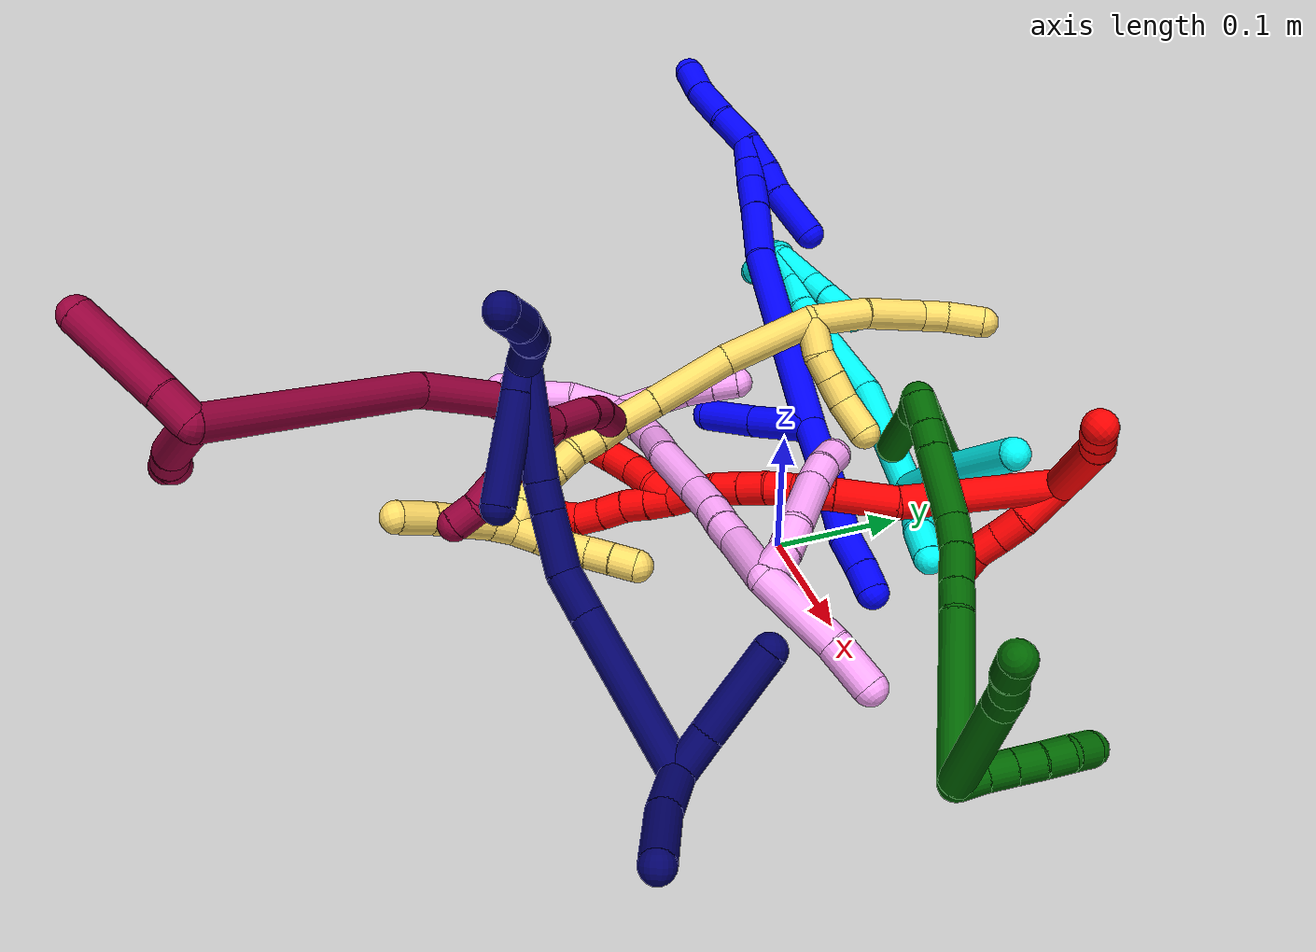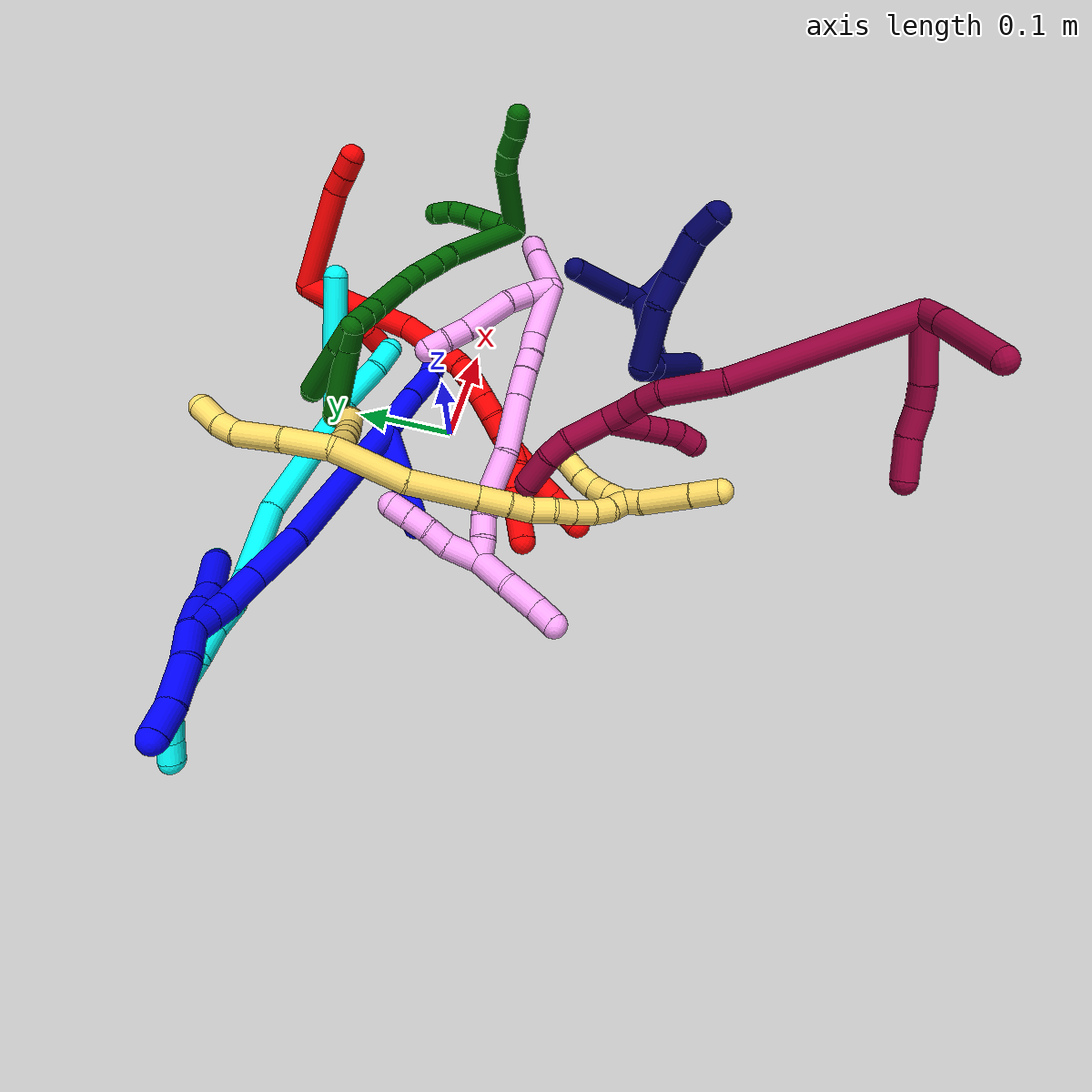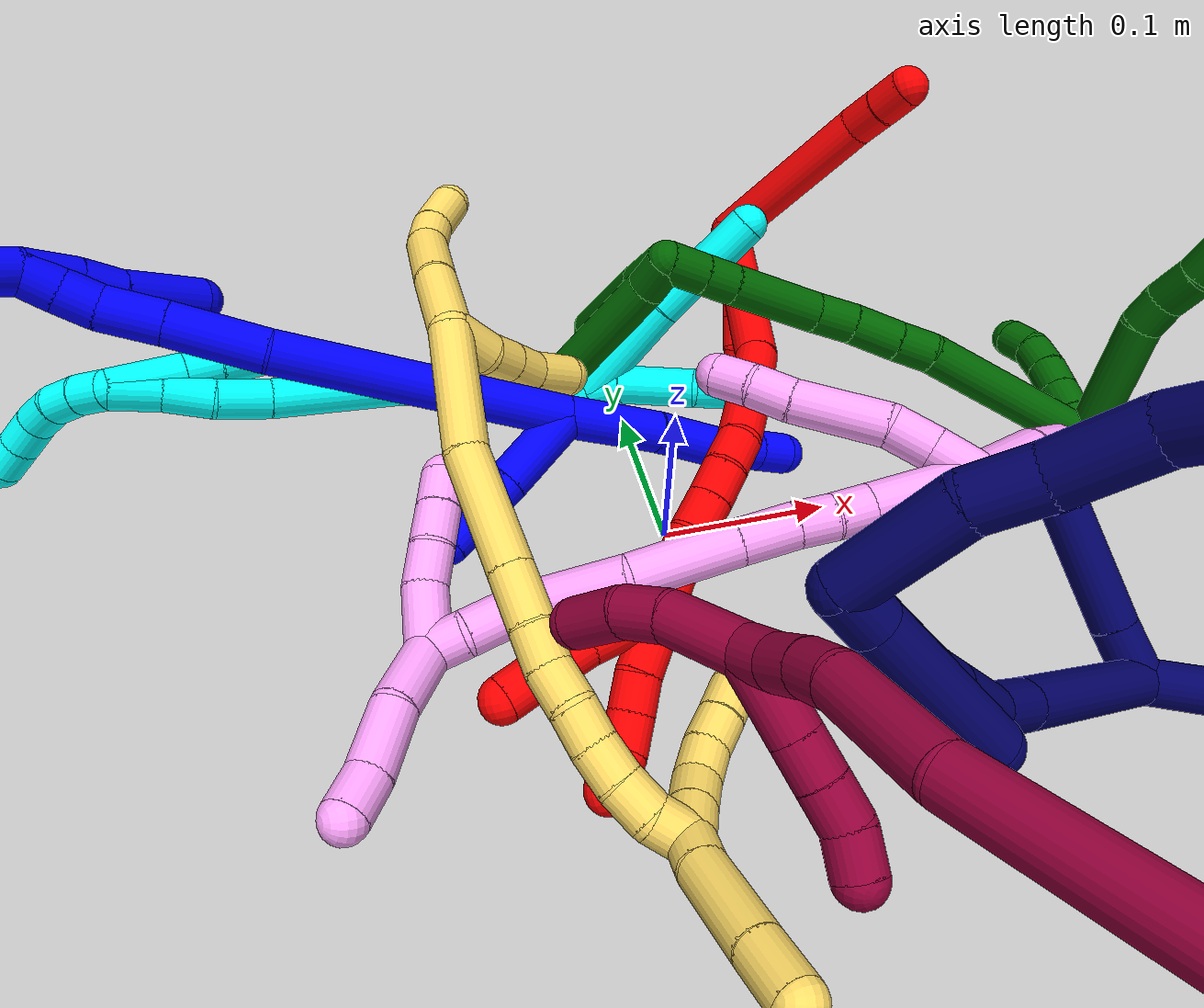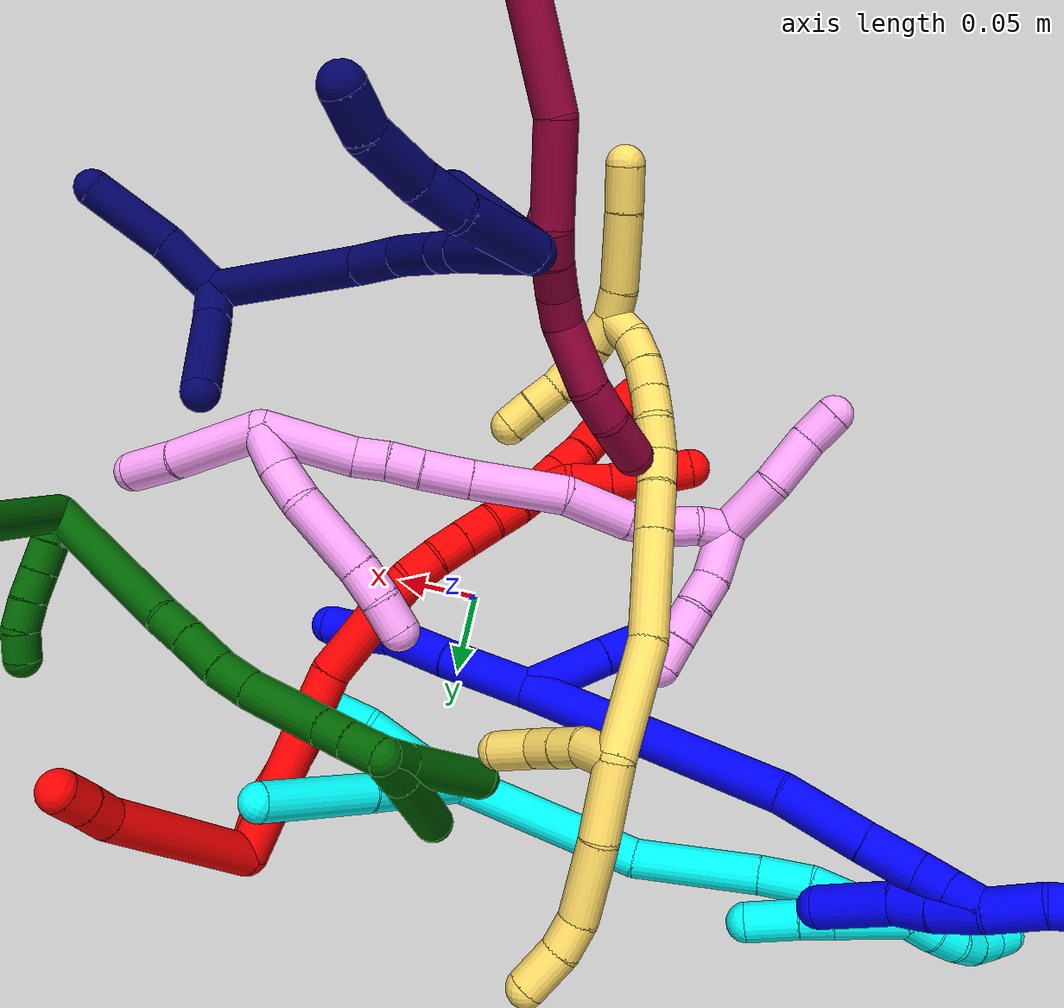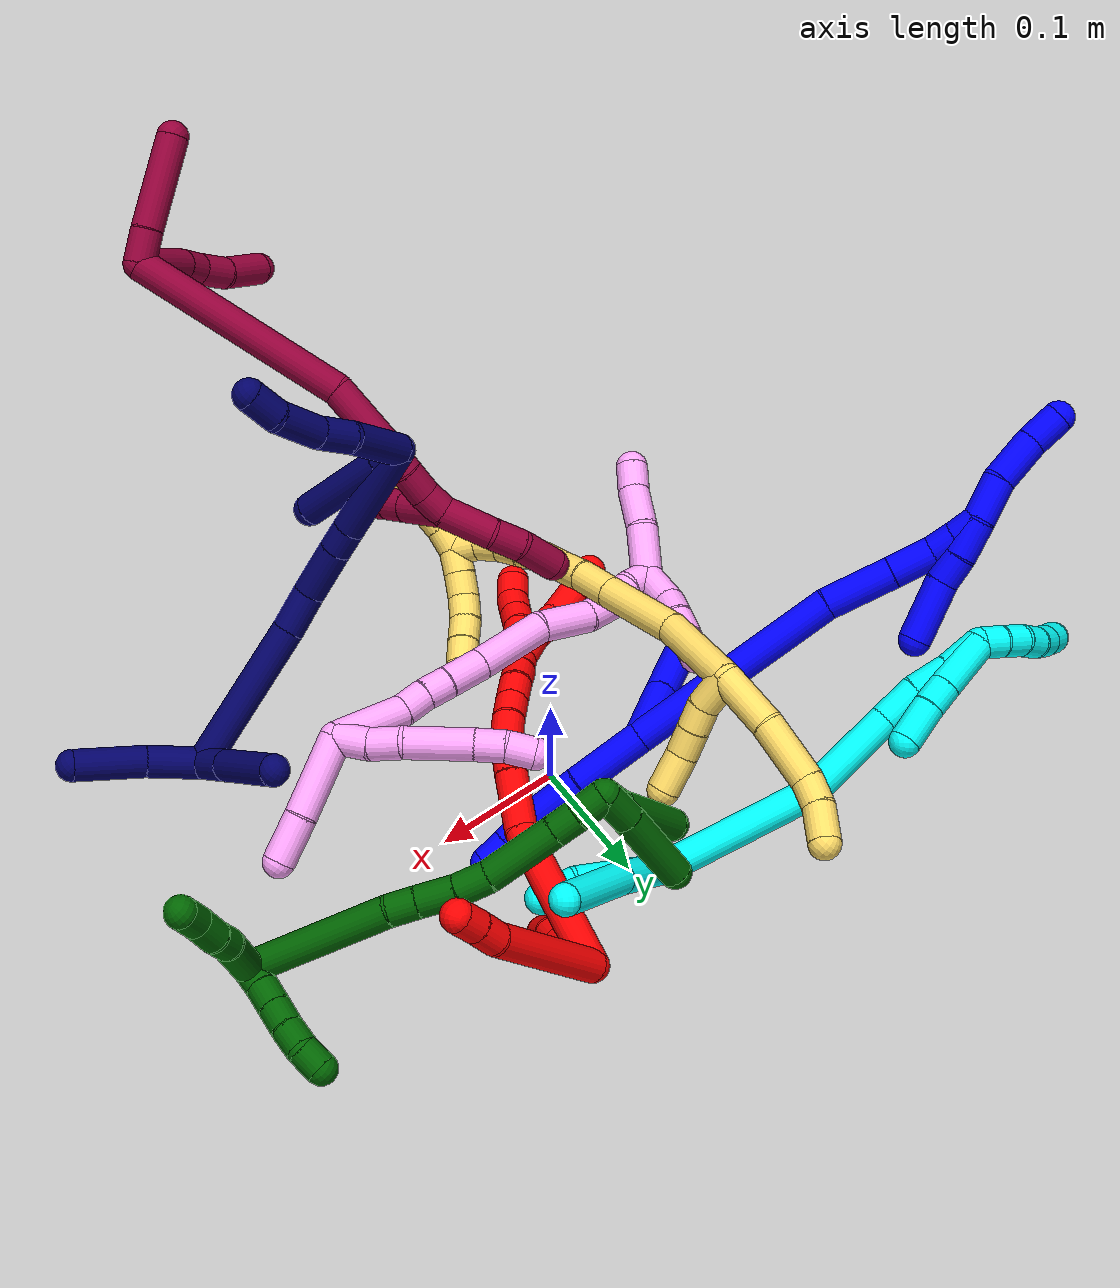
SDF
<sdf version="1.7">
 <world name="default">
  <plugin name="TubeGeneratorPlugin" filename="libtube_generator_plugin.so"/>
  <model name="photoneo_s_sensor">
   <static>1</static>
   <pose>0 0 2 1.57079 1.57079 3.14159</pose>
   <link name="link">
    <inertial><mass>0.1</mass></inertial>
    <sensor name="sensor" type="depth">
     <update_rate>30</update_rate>
     <camera>
      <horizontal_fov>1.22</horizontal_fov>
      <image><width>1920</width><height>1200</height><format>B8G8R8</format></image>
      <clip><near>0.1</near><far>4</far></clip>
      <depth_camera><output>points</output></depth_camera>
     </camera>
     <plugin name="camera_plugin" filename="libgazebo_ros_depth_camera.so">
      <baseline>0.2</baseline>
      <alwaysOn>1</alwaysOn>
      <updateRate>0.0</updateRate>
      <cameraName>camera_ir</cameraName>
      <imageTopicName>/camera/color/image_raw</imageTopicName>
      <cameraInfoTopicName>/camera/color/camera_info</cameraInfoTopicName>
      <depthImageTopicName>/camera/depth/image_raw</depthImageTopicName>
      <depthImageCameraInfoTopicName>/camera/depth/camera_info</depthImageCameraInfoTopicName>
      <pointCloudTopicName>/camera/depth/points</pointCloudTopicName>
      <frameName>fr_optical</frameName>
      <pointCloudCutoff>0.1</pointCloudCutoff>
      <pointCloudCutoffMax>2.0</pointCloudCutoffMax>
      <distortionK1>0</distortionK1>
      <distortionK2>0</distortionK2>
      <distortionK3>0</distortionK3>
      <distortionT1>0</distortionT1>
      <distortionT2>0</distortionT2>
      <CxPrime>0</CxPrime>
      <Cx>0</Cx>
      <Cy>0</Cy>
      <focalLength>0</focalLength>
      <hackBaseline>0</hackBaseline>
     </plugin>
    </sensor>
   </link>
  </model>
  <gravity>0 0 -9.8</gravity>
  <magnetic_field>6e-06 2.3e-05 -4.2e-05</magnetic_field>
  <atmosphere type="adiabatic"/>
  <physics name="default_physics" default="0" type="ode">
   <max_step_size>0.003</max_step_size>
   <real_time_factor>1</real_time_factor>
   <real_time_update_rate>1000</real_time_update_rate>
   <max_contacts>10000</max_contacts>
   <ode>
    <solver>
     <type>quick</type>
     <iters>100</iters>
     <sor>1.3</sor>
     <use_dynamic_moi_rescaling>0</use_dynamic_moi_rescaling>
    </solver>
    <constraints>
     <contact_max_correcting_vel>0</contact_max_correcting_vel>
     <contact_surface_layer>0.001</contact_surface_layer>
     <cfm>0</cfm>
     <erp>0.2</erp>
    </constraints>
   </ode>
  </physics>
  <scene><ambient>0.4 0.4 0.4 1</ambient><background>0.7 0.7 0.7 1</background><shadows>0</shadows></scene>
  <audio><device>default</device></audio>
  <spherical_coordinates>
   <surface_model>EARTH_WGS84</surface_model>
   <latitude_deg>0</latitude_deg>
   <longitude_deg>0</longitude_deg>
   <elevation>0</elevation>
   <heading_deg>0</heading_deg>
  </spherical_coordinates>
  <model name="bin">
   <static>1</static>
   <link name="bottom">
    <collision name="collision-bottom">
     <pose>0 0 -0.01 0 -0 0</pose>
     <geometry><box><size>0.8 0.6 0.02</size></box></geometry>
     <surface>
      <friction><ode><mu>100</mu><mu2>100</mu2></ode></friction>
      <contact><collide_bitmask>65535</collide_bitmask></contact>
     </surface>
    </collision>
   </link>
   <link name="west_wall">
    <collision name="collision-west_wall">
     <pose>-0.41 0 0.1 0 -0 0</pose>
     <geometry><box><size>0.02 0.6 0.2</size></box></geometry>
     <surface>
      <friction><ode><mu>100</mu><mu2>100</mu2></ode></friction>
      <contact><collide_bitmask>65535</collide_bitmask></contact>
     </surface>
    </collision>
   </link>
   <link name="east_wall">
    <collision name="collision-east_wall">
     <pose>0.41 0 0.1 0 -0 0</pose>
     <geometry><box><size>0.02 0.6 0.2</size></box></geometry>
     <surface>
      <friction><ode><mu>100</mu><mu2>100</mu2></ode></friction>
      <contact><collide_bitmask>65535</collide_bitmask></contact>
     </surface>
    </collision>
   </link>
   <link name="south_wall">
    <collision name="collision-south_wall">
     <pose>0 -0.31 0.1 0 -0 0</pose>
     <geometry><box><size>0.8 0.02 0.2</size></box></geometry>
     <surface>
      <friction><ode><mu>100</mu><mu2>100</mu2></ode></friction>
      <contact><collide_bitmask>65535</collide_bitmask></contact>
     </surface>
    </collision>
   </link>
   <link name="north_wall">
    <collision name="collision-north_wall">
     <pose>0 0.31 0.1 0 -0 0</pose>
     <geometry><box><size>0.8 0.02 0.2</size></box></geometry>
     <surface>
      <friction><ode><mu>100</mu><mu2>100</mu2></ode></friction>
      <contact><collide_bitmask>65535</collide_bitmask></contact>
     </surface>
    </collision>
   </link>
  </model>
  <model name="1">
   <static>0</static>
   <link name="1">
    <collision name="collision-cylinder-e_1_2_8">
     <pose>0.015161 -0.001856 -0.024793 3.06687 0.547582 2.87695</pose>
     <geometry><cylinder><radius>0.0125</radius><length>0.058241</length></cylinder></geometry>
     <surface>
      <friction><ode><mu>1.16</mu><mu2>1.16</mu2><slip1>0</slip1><slip2>0</slip2></ode></friction>
      <contact><ode><kp>1e+06</kp><kd>1</kd><max_vel>0</max_vel><min_depth>0.001</min_depth></ode></contact>
     </surface>
    </collision>
    <visual name="visual-cylinder-e_1_2_8">
     <pose>0.015161 -0.001856 -0.024793 3.06687 0.547582 2.87695</pose>
     <geometry><cylinder><radius>0.0125</radius><length>0.058241</length></cylinder></geometry>
     <material><ambient>0 0 1 1</ambient></material>
    </visual>
    <collision name="collision-cylinder-e_2_8_9">
     <pose>0.041038 -0.006677 -0.068767 2.98821 0.50449 2.56211</pose>
     <geometry><cylinder><radius>0.0125</radius><length>0.044341</length></cylinder></geometry>
     <surface>
      <friction><ode><mu>1.16</mu><mu2>1.16</mu2><slip1>0</slip1><slip2>0</slip2></ode></friction>
      <contact><ode><kp>1e+06</kp><kd>1</kd><max_vel>0</max_vel><min_depth>0.001</min_depth></ode></contact>
     </surface>
    </collision>
    <visual name="visual-cylinder-e_2_8_9">
     <pose>0.041038 -0.006677 -0.068767 2.98821 0.50449 2.56211</pose>
     <geometry><cylinder><radius>0.0125</radius><length>0.044341</length></cylinder></geometry>
     <material><ambient>0 0 1 1</ambient></material>
    </visual>
    <collision name="collision-cylinder-e_3_9_10">
     <pose>0.056532 -0.009133 -0.099882 -3.09889 0.380459 -2.9207</pose>
     <geometry><cylinder><radius>0.0125</radius><length>0.025729</length></cylinder></geometry>
     <surface>
      <friction><ode><mu>1.16</mu><mu2>1.16</mu2><slip1>0</slip1><slip2>0</slip2></ode></friction>
      <contact><ode><kp>1e+06</kp><kd>1</kd><max_vel>0</max_vel><min_depth>0.001</min_depth></ode></contact>
     </surface>
    </collision>
    <visual name="visual-cylinder-e_3_9_10">
     <pose>0.056532 -0.009133 -0.099882 -3.09889 0.380459 -2.9207</pose>
     <geometry><cylinder><radius>0.0125</radius><length>0.025729</length></cylinder></geometry>
     <material><ambient>0 0 1 1</ambient></material>
    </visual>
    <collision name="collision-cylinder-e_4_10_6">
     <pose>0.06586 -0.008794 -0.121657 3.12418 0.433084 3.06246</pose>
     <geometry><cylinder><radius>0.0125</radius><length>0.021689</length></cylinder></geometry>
     <surface>
      <friction><ode><mu>1.16</mu><mu2>1.16</mu2><slip1>0</slip1><slip2>0</slip2></ode></friction>
      <contact><ode><kp>1e+06</kp><kd>1</kd><max_vel>0</max_vel><min_depth>0.001</min_depth></ode></contact>
     </surface>
    </collision>
    <visual name="visual-cylinder-e_4_10_6">
     <pose>0.06586 -0.008794 -0.121657 3.12418 0.433084 3.06246</pose>
     <geometry><cylinder><radius>0.0125</radius><length>0.021689</length></cylinder></geometry>
     <material><ambient>0 0 1 1</ambient></material>
    </visual>
    <collision name="collision-cylinder-e_1_2_11">
     <pose>-0.007198 -0.020234 0.01481 0.93895 -0.279535 -0.142499</pose>
     <geometry><cylinder><radius>0.0125</radius><length>0.052175</length></cylinder></geometry>
     <surface>
      <friction><ode><mu>1.16</mu><mu2>1.16</mu2><slip1>0</slip1><slip2>0</slip2></ode></friction>
      <contact><ode><kp>1e+06</kp><kd>1</kd><max_vel>0</max_vel><min_depth>0.001</min_depth></ode></contact>
     </surface>
    </collision>
    <visual name="visual-cylinder-e_1_2_11">
     <pose>-0.007198 -0.020234 0.01481 0.93895 -0.279535 -0.142499</pose>
     <geometry><cylinder><radius>0.0125</radius><length>0.052175</length></cylinder></geometry>
     <material><ambient>0 0 1 1</ambient></material>
    </visual>
    <collision name="collision-cylinder-e_2_11_5">
     <pose>-0.02126 -0.058422 0.043844 0.900817 -0.291181 -0.14157</pose>
     <geometry><cylinder><radius>0.0125</radius><length>0.047825</length></cylinder></geometry>
     <surface>
      <friction><ode><mu>1.16</mu><mu2>1.16</mu2><slip1>0</slip1><slip2>0</slip2></ode></friction>
      <contact><ode><kp>1e+06</kp><kd>1</kd><max_vel>0</max_vel><min_depth>0.001</min_depth></ode></contact>
     </surface>
    </collision>
    <visual name="visual-cylinder-e_2_11_5">
     <pose>-0.02126 -0.058422 0.043844 0.900817 -0.291181 -0.14157</pose>
     <geometry><cylinder><radius>0.0125</radius><length>0.047825</length></cylinder></geometry>
     <material><ambient>0 0 1 1</ambient></material>
    </visual>
    <collision name="collision-cylinder-e_1_2_12">
     <pose>-0.044165 0.008982 0.07271 -0.122914 -0.542498 0.034223</pose>
     <geometry><cylinder><radius>0.0125</radius><length>0.17109</length></cylinder></geometry>
     <surface>
      <friction><ode><mu>1.16</mu><mu2>1.16</mu2><slip1>0</slip1><slip2>0</slip2></ode></friction>
      <contact><ode><kp>1e+06</kp><kd>1</kd><max_vel>0</max_vel><min_depth>0.001</min_depth></ode></contact>
     </surface>
    </collision>
    <visual name="visual-cylinder-e_1_2_12">
     <pose>-0.044165 0.008982 0.07271 -0.122914 -0.542498 0.034223</pose>
     <geometry><cylinder><radius>0.0125</radius><length>0.17109</length></cylinder></geometry>
     <material><ambient>0 0 1 1</ambient></material>
    </visual>
    <collision name="collision-cylinder-e_2_12_13">
     <pose>-0.10549 0.022499 0.165501 -0.222092 -0.694877 0.080714</pose>
     <geometry><cylinder><radius>0.0125</radius><length>0.053602</length></cylinder></geometry>
     <surface>
      <friction><ode><mu>1.16</mu><mu2>1.16</mu2><slip1>0</slip1><slip2>0</slip2></ode></friction>
      <contact><ode><kp>1e+06</kp><kd>1</kd><max_vel>0</max_vel><min_depth>0.001</min_depth></ode></contact>
     </surface>
    </collision>
    <visual name="visual-cylinder-e_2_12_13">
     <pose>-0.10549 0.022499 0.165501 -0.222092 -0.694877 0.080714</pose>
     <geometry><cylinder><radius>0.0125</radius><length>0.053602</length></cylinder></geometry>
     <material><ambient>0 0 1 1</ambient></material>
    </visual>
    <collision name="collision-cylinder-e_3_13_14">
     <pose>-0.133572 0.029363 0.19847 -0.178766 -0.695049 0.064904</pose>
     <geometry><cylinder><radius>0.0125</radius><length>0.034105</length></cylinder></geometry>
     <surface>
      <friction><ode><mu>1.16</mu><mu2>1.16</mu2><slip1>0</slip1><slip2>0</slip2></ode></friction>
      <contact><ode><kp>1e+06</kp><kd>1</kd><max_vel>0</max_vel><min_depth>0.001</min_depth></ode></contact>
     </surface>
    </collision>
    <visual name="visual-cylinder-e_3_13_14">
     <pose>-0.133572 0.029363 0.19847 -0.178766 -0.695049 0.064904</pose>
     <geometry><cylinder><radius>0.0125</radius><length>0.034105</length></cylinder></geometry>
     <material><ambient>0 0 1 1</ambient></material>
    </visual>
    <collision name="collision-cylinder-e_4_14_15">
     <pose>-0.149341 0.034808 0.22002 -0.345354 -0.484773 0.086194</pose>
     <geometry><cylinder><radius>0.0125</radius><length>0.020808</length></cylinder></geometry>
     <surface>
      <friction><ode><mu>1.16</mu><mu2>1.16</mu2><slip1>0</slip1><slip2>0</slip2></ode></friction>
      <contact><ode><kp>1e+06</kp><kd>1</kd><max_vel>0</max_vel><min_depth>0.001</min_depth></ode></contact>
     </surface>
    </collision>
    <visual name="visual-cylinder-e_4_14_15">
     <pose>-0.149341 0.034808 0.22002 -0.345354 -0.484773 0.086194</pose>
     <geometry><cylinder><radius>0.0125</radius><length>0.020808</length></cylinder></geometry>
     <material><ambient>0 0 1 1</ambient></material>
    </visual>
    <collision name="collision-cylinder-e_5_15_1">
     <pose>-0.158336 0.041299 0.237365 -0.370704 -0.418768 0.079647</pose>
     <geometry><cylinder><radius>0.0125</radius><length>0.020394</length></cylinder></geometry>
     <surface>
      <friction><ode><mu>1.16</mu><mu2>1.16</mu2><slip1>0</slip1><slip2>0</slip2></ode></friction>
      <contact><ode><kp>1e+06</kp><kd>1</kd><max_vel>0</max_vel><min_depth>0.001</min_depth></ode></contact>
     </surface>
    </collision>
    <visual name="visual-cylinder-e_5_15_1">
     <pose>-0.158336 0.041299 0.237365 -0.370704 -0.418768 0.079647</pose>
     <geometry><cylinder><radius>0.0125</radius><length>0.020394</length></cylinder></geometry>
     <material><ambient>0 0 1 1</ambient></material>
    </visual>
    <collision name="collision-cylinder-e_1_1_16">
     <pose>-0.161108 0.044946 0.231307 -3.12312 0.092966 -2.74962</pose>
     <geometry><cylinder><radius>0.0125</radius><length>0.029615</length></cylinder></geometry>
     <surface>
      <friction><ode><mu>1.16</mu><mu2>1.16</mu2><slip1>0</slip1><slip2>0</slip2></ode></friction>
      <contact><ode><kp>1e+06</kp><kd>1</kd><max_vel>0</max_vel><min_depth>0.001</min_depth></ode></contact>
     </surface>
    </collision>
    <visual name="visual-cylinder-e_1_1_16">
     <pose>-0.161108 0.044946 0.231307 -3.12312 0.092966 -2.74962</pose>
     <geometry><cylinder><radius>0.0125</radius><length>0.029615</length></cylinder></geometry>
     <material><ambient>0 0 1 1</ambient></material>
    </visual>
    <collision name="collision-cylinder-e_2_16_17">
     <pose>-0.157749 0.043965 0.205379 3.03 0.174477 2.0049</pose>
     <geometry><cylinder><radius>0.0125</radius><length>0.022861</length></cylinder></geometry>
     <surface>
      <friction><ode><mu>1.16</mu><mu2>1.16</mu2><slip1>0</slip1><slip2>0</slip2></ode></friction>
      <contact><ode><kp>1e+06</kp><kd>1</kd><max_vel>0</max_vel><min_depth>0.001</min_depth></ode></contact>
     </surface>
    </collision>
    <visual name="visual-cylinder-e_2_16_17">
     <pose>-0.157749 0.043965 0.205379 3.03 0.174477 2.0049</pose>
     <geometry><cylinder><radius>0.0125</radius><length>0.022861</length></cylinder></geometry>
     <material><ambient>0 0 1 1</ambient></material>
    </visual>
    <collision name="collision-cylinder-e_3_17_4">
     <pose>-0.154299 0.044445 0.170539 -3.06845 0.061722 -1.40166</pose>
     <geometry><cylinder><radius>0.0125</radius><length>0.047523</length></cylinder></geometry>
     <surface>
      <friction><ode><mu>1.16</mu><mu2>1.16</mu2><slip1>0</slip1><slip2>0</slip2></ode></friction>
      <contact><ode><kp>1e+06</kp><kd>1</kd><max_vel>0</max_vel><min_depth>0.001</min_depth></ode></contact>
     </surface>
    </collision>
    <visual name="visual-cylinder-e_3_17_4">
     <pose>-0.154299 0.044445 0.170539 -3.06845 0.061722 -1.40166</pose>
     <geometry><cylinder><radius>0.0125</radius><length>0.047523</length></cylinder></geometry>
     <material><ambient>0 0 1 1</ambient></material>
    </visual>
    <collision name="collision-cylinder-e_1_1_18">
     <pose>-0.164826 0.041484 0.262525 0.191248 -0.138762 -0.013331</pose>
     <geometry><cylinder><radius>0.0125</radius><length>0.033891</length></cylinder></geometry>
     <surface>
      <friction><ode><mu>1.16</mu><mu2>1.16</mu2><slip1>0</slip1><slip2>0</slip2></ode></friction>
      <contact><ode><kp>1e+06</kp><kd>1</kd><max_vel>0</max_vel><min_depth>0.001</min_depth></ode></contact>
     </surface>
    </collision>
    <visual name="visual-cylinder-e_1_1_18">
     <pose>-0.164826 0.041484 0.262525 0.191248 -0.138762 -0.013331</pose>
     <geometry><cylinder><radius>0.0125</radius><length>0.033891</length></cylinder></geometry>
     <material><ambient>0 0 1 1</ambient></material>
    </visual>
    <collision name="collision-cylinder-e_2_18_19">
     <pose>-0.174587 0.034393 0.296408 0.220474 -0.394011 -0.044177</pose>
     <geometry><cylinder><radius>0.0125</radius><length>0.038637</length></cylinder></geometry>
     <surface>
      <friction><ode><mu>1.16</mu><mu2>1.16</mu2><slip1>0</slip1><slip2>0</slip2></ode></friction>
      <contact><ode><kp>1e+06</kp><kd>1</kd><max_vel>0</max_vel><min_depth>0.001</min_depth></ode></contact>
     </surface>
    </collision>
    <visual name="visual-cylinder-e_2_18_19">
     <pose>-0.174587 0.034393 0.296408 0.220474 -0.394011 -0.044177</pose>
     <geometry><cylinder><radius>0.0125</radius><length>0.038637</length></cylinder></geometry>
     <material><ambient>0 0 1 1</ambient></material>
    </visual>
    <collision name="collision-cylinder-e_3_19_3">
     <pose>-0.18828 0.02994 0.32602 0.0452 -0.474641 -0.010935</pose>
     <geometry><cylinder><radius>0.0125</radius><length>0.027472</length></cylinder></geometry>
     <surface>
      <friction><ode><mu>1.16</mu><mu2>1.16</mu2><slip1>0</slip1><slip2>0</slip2></ode></friction>
      <contact><ode><kp>1e+06</kp><kd>1</kd><max_vel>0</max_vel><min_depth>0.001</min_depth></ode></contact>
     </surface>
    </collision>
    <visual name="visual-cylinder-e_3_19_3">
     <pose>-0.18828 0.02994 0.32602 0.0452 -0.474641 -0.010935</pose>
     <geometry><cylinder><radius>0.0125</radius><length>0.027472</length></cylinder></geometry>
     <material><ambient>0 0 1 1</ambient></material>
    </visual>
    <collision name="collision-sphere-3">
     <pose>-0.194558 0.029388 0.338225 0 -0 0</pose>
     <geometry><sphere><radius>0.0125</radius></sphere></geometry>
     <surface>
      <friction><ode><mu>1.16</mu><mu2>1.16</mu2><slip1>0</slip1><slip2>0</slip2></ode></friction>
      <contact><ode><kp>1e+06</kp><kd>1</kd><max_vel>0</max_vel><min_depth>0.001</min_depth></ode></contact>
     </surface>
    </collision>
    <visual name="visual-sphere-3">
     <pose>-0.194558 0.029388 0.338225 0 -0 0</pose>
     <geometry><sphere><radius>0.0125</radius></sphere></geometry>
     <material><ambient>0 0 1 1</ambient></material>
    </visual>
    <collision name="collision-sphere-19">
     <pose>-0.182003 0.030492 0.313815 0 -0 0</pose>
     <geometry><sphere><radius>0.0125</radius></sphere></geometry>
     <surface>
      <friction><ode><mu>1.16</mu><mu2>1.16</mu2><slip1>0</slip1><slip2>0</slip2></ode></friction>
      <contact><ode><kp>1e+06</kp><kd>1</kd><max_vel>0</max_vel><min_depth>0.001</min_depth></ode></contact>
     </surface>
    </collision>
    <visual name="visual-sphere-19">
     <pose>-0.182003 0.030492 0.313815 0 -0 0</pose>
     <geometry><sphere><radius>0.0125</radius></sphere></geometry>
     <material><ambient>0 0 1 1</ambient></material>
    </visual>
    <collision name="collision-sphere-11">
     <pose>-0.014395 -0.040467 0.02962 0 -0 0</pose>
     <geometry><sphere><radius>0.0125</radius></sphere></geometry>
     <surface>
      <friction><ode><mu>1.16</mu><mu2>1.16</mu2><slip1>0</slip1><slip2>0</slip2></ode></friction>
      <contact><ode><kp>1e+06</kp><kd>1</kd><max_vel>0</max_vel><min_depth>0.001</min_depth></ode></contact>
     </surface>
    </collision>
    <visual name="visual-sphere-11">
     <pose>-0.014395 -0.040467 0.02962 0 -0 0</pose>
     <geometry><sphere><radius>0.0125</radius></sphere></geometry>
     <material><ambient>0 0 1 1</ambient></material>
    </visual>
    <collision name="collision-sphere-6">
     <pose>0.070411 -0.008966 -0.131499 0 -0 0</pose>
     <geometry><sphere><radius>0.0125</radius></sphere></geometry>
     <surface>
      <friction><ode><mu>1.16</mu><mu2>1.16</mu2><slip1>0</slip1><slip2>0</slip2></ode></friction>
      <contact><ode><kp>1e+06</kp><kd>1</kd><max_vel>0</max_vel><min_depth>0.001</min_depth></ode></contact>
     </surface>
    </collision>
    <visual name="visual-sphere-6">
     <pose>0.070411 -0.008966 -0.131499 0 -0 0</pose>
     <geometry><sphere><radius>0.0125</radius></sphere></geometry>
     <material><ambient>0 0 1 1</ambient></material>
    </visual>
    <collision name="collision-sphere-10">
     <pose>0.061309 -0.008623 -0.111815 0 -0 0</pose>
     <geometry><sphere><radius>0.0125</radius></sphere></geometry>
     <surface>
      <friction><ode><mu>1.16</mu><mu2>1.16</mu2><slip1>0</slip1><slip2>0</slip2></ode></friction>
      <contact><ode><kp>1e+06</kp><kd>1</kd><max_vel>0</max_vel><min_depth>0.001</min_depth></ode></contact>
     </surface>
    </collision>
    <visual name="visual-sphere-10">
     <pose>0.061309 -0.008623 -0.111815 0 -0 0</pose>
     <geometry><sphere><radius>0.0125</radius></sphere></geometry>
     <material><ambient>0 0 1 1</ambient></material>
    </visual>
    <collision name="collision-sphere-9">
     <pose>0.051754 -0.009643 -0.087948 0 -0 0</pose>
     <geometry><sphere><radius>0.0125</radius></sphere></geometry>
     <surface>
      <friction><ode><mu>1.16</mu><mu2>1.16</mu2><slip1>0</slip1><slip2>0</slip2></ode></friction>
      <contact><ode><kp>1e+06</kp><kd>1</kd><max_vel>0</max_vel><min_depth>0.001</min_depth></ode></contact>
     </surface>
    </collision>
    <visual name="visual-sphere-9">
     <pose>0.051754 -0.009643 -0.087948 0 -0 0</pose>
     <geometry><sphere><radius>0.0125</radius></sphere></geometry>
     <material><ambient>0 0 1 1</ambient></material>
    </visual>
    <collision name="collision-sphere-2">
     <geometry><sphere><radius>0.0125</radius></sphere></geometry>
     <surface>
      <friction><ode><mu>1.16</mu><mu2>1.16</mu2><slip1>0</slip1><slip2>0</slip2></ode></friction>
      <contact><ode><kp>1e+06</kp><kd>1</kd><max_vel>0</max_vel><min_depth>0.001</min_depth></ode></contact>
     </surface>
    </collision>
    <visual name="visual-sphere-2">
     <geometry><sphere><radius>0.0125</radius></sphere></geometry>
     <material><ambient>0 0 1 1</ambient></material>
    </visual>
    <collision name="collision-sphere-8">
     <pose>0.030322 -0.003712 -0.049587 0 -0 0</pose>
     <geometry><sphere><radius>0.0125</radius></sphere></geometry>
     <surface>
      <friction><ode><mu>1.16</mu><mu2>1.16</mu2><slip1>0</slip1><slip2>0</slip2></ode></friction>
      <contact><ode><kp>1e+06</kp><kd>1</kd><max_vel>0</max_vel><min_depth>0.001</min_depth></ode></contact>
     </surface>
    </collision>
    <visual name="visual-sphere-8">
     <pose>0.030322 -0.003712 -0.049587 0 -0 0</pose>
     <geometry><sphere><radius>0.0125</radius></sphere></geometry>
     <material><ambient>0 0 1 1</ambient></material>
    </visual>
    <collision name="collision-sphere-5">
     <pose>-0.028125 -0.076377 0.058068 0 -0 0</pose>
     <geometry><sphere><radius>0.0125</radius></sphere></geometry>
     <surface>
      <friction><ode><mu>1.16</mu><mu2>1.16</mu2><slip1>0</slip1><slip2>0</slip2></ode></friction>
      <contact><ode><kp>1e+06</kp><kd>1</kd><max_vel>0</max_vel><min_depth>0.001</min_depth></ode></contact>
     </surface>
    </collision>
    <visual name="visual-sphere-5">
     <pose>-0.028125 -0.076377 0.058068 0 -0 0</pose>
     <geometry><sphere><radius>0.0125</radius></sphere></geometry>
     <material><ambient>0 0 1 1</ambient></material>
    </visual>
    <collision name="collision-sphere-12">
     <pose>-0.08833 0.017965 0.14542 0 -0 0</pose>
     <geometry><sphere><radius>0.0125</radius></sphere></geometry>
     <surface>
      <friction><ode><mu>1.16</mu><mu2>1.16</mu2><slip1>0</slip1><slip2>0</slip2></ode></friction>
      <contact><ode><kp>1e+06</kp><kd>1</kd><max_vel>0</max_vel><min_depth>0.001</min_depth></ode></contact>
     </surface>
    </collision>
    <visual name="visual-sphere-12">
     <pose>-0.08833 0.017965 0.14542 0 -0 0</pose>
     <geometry><sphere><radius>0.0125</radius></sphere></geometry>
     <material><ambient>0 0 1 1</ambient></material>
    </visual>
    <collision name="collision-sphere-13">
     <pose>-0.122651 0.027034 0.185582 0 -0 0</pose>
     <geometry><sphere><radius>0.0125</radius></sphere></geometry>
     <surface>
      <friction><ode><mu>1.16</mu><mu2>1.16</mu2><slip1>0</slip1><slip2>0</slip2></ode></friction>
      <contact><ode><kp>1e+06</kp><kd>1</kd><max_vel>0</max_vel><min_depth>0.001</min_depth></ode></contact>
     </surface>
    </collision>
    <visual name="visual-sphere-13">
     <pose>-0.122651 0.027034 0.185582 0 -0 0</pose>
     <geometry><sphere><radius>0.0125</radius></sphere></geometry>
     <material><ambient>0 0 1 1</ambient></material>
    </visual>
    <collision name="collision-sphere-14">
     <pose>-0.144493 0.031692 0.211358 0 -0 0</pose>
     <geometry><sphere><radius>0.0125</radius></sphere></geometry>
     <surface>
      <friction><ode><mu>1.16</mu><mu2>1.16</mu2><slip1>0</slip1><slip2>0</slip2></ode></friction>
      <contact><ode><kp>1e+06</kp><kd>1</kd><max_vel>0</max_vel><min_depth>0.001</min_depth></ode></contact>
     </surface>
    </collision>
    <visual name="visual-sphere-14">
     <pose>-0.144493 0.031692 0.211358 0 -0 0</pose>
     <geometry><sphere><radius>0.0125</radius></sphere></geometry>
     <material><ambient>0 0 1 1</ambient></material>
    </visual>
    <collision name="collision-sphere-15">
     <pose>-0.15419 0.037924 0.228682 0 -0 0</pose>
     <geometry><sphere><radius>0.0125</radius></sphere></geometry>
     <surface>
      <friction><ode><mu>1.16</mu><mu2>1.16</mu2><slip1>0</slip1><slip2>0</slip2></ode></friction>
      <contact><ode><kp>1e+06</kp><kd>1</kd><max_vel>0</max_vel><min_depth>0.001</min_depth></ode></contact>
     </surface>
    </collision>
    <visual name="visual-sphere-15">
     <pose>-0.15419 0.037924 0.228682 0 -0 0</pose>
     <geometry><sphere><radius>0.0125</radius></sphere></geometry>
     <material><ambient>0 0 1 1</ambient></material>
    </visual>
    <collision name="collision-sphere-1">
     <pose>-0.162483 0.044674 0.246048 0 -0 0</pose>
     <geometry><sphere><radius>0.0125</radius></sphere></geometry>
     <surface>
      <friction><ode><mu>1.16</mu><mu2>1.16</mu2><slip1>0</slip1><slip2>0</slip2></ode></friction>
      <contact><ode><kp>1e+06</kp><kd>1</kd><max_vel>0</max_vel><min_depth>0.001</min_depth></ode></contact>
     </surface>
    </collision>
    <visual name="visual-sphere-1">
     <pose>-0.162483 0.044674 0.246048 0 -0 0</pose>
     <geometry><sphere><radius>0.0125</radius></sphere></geometry>
     <material><ambient>0 0 1 1</ambient></material>
    </visual>
    <collision name="collision-sphere-18">
     <pose>-0.16717 0.038294 0.279002 0 -0 0</pose>
     <geometry><sphere><radius>0.0125</radius></sphere></geometry>
     <surface>
      <friction><ode><mu>1.16</mu><mu2>1.16</mu2><slip1>0</slip1><slip2>0</slip2></ode></friction>
      <contact><ode><kp>1e+06</kp><kd>1</kd><max_vel>0</max_vel><min_depth>0.001</min_depth></ode></contact>
     </surface>
    </collision>
    <visual name="visual-sphere-18">
     <pose>-0.16717 0.038294 0.279002 0 -0 0</pose>
     <geometry><sphere><radius>0.0125</radius></sphere></geometry>
     <material><ambient>0 0 1 1</ambient></material>
    </visual>
    <collision name="collision-sphere-16">
     <pose>-0.159733 0.045219 0.216566 0 -0 0</pose>
     <geometry><sphere><radius>0.0125</radius></sphere></geometry>
     <surface>
      <friction><ode><mu>1.16</mu><mu2>1.16</mu2><slip1>0</slip1><slip2>0</slip2></ode></friction>
      <contact><ode><kp>1e+06</kp><kd>1</kd><max_vel>0</max_vel><min_depth>0.001</min_depth></ode></contact>
     </surface>
    </collision>
    <visual name="visual-sphere-16">
     <pose>-0.159733 0.045219 0.216566 0 -0 0</pose>
     <geometry><sphere><radius>0.0125</radius></sphere></geometry>
     <material><ambient>0 0 1 1</ambient></material>
    </visual>
    <collision name="collision-sphere-17">
     <pose>-0.155765 0.042711 0.194192 0 -0 0</pose>
     <geometry><sphere><radius>0.0125</radius></sphere></geometry>
     <surface>
      <friction><ode><mu>1.16</mu><mu2>1.16</mu2><slip1>0</slip1><slip2>0</slip2></ode></friction>
      <contact><ode><kp>1e+06</kp><kd>1</kd><max_vel>0</max_vel><min_depth>0.001</min_depth></ode></contact>
     </surface>
    </collision>
    <visual name="visual-sphere-17">
     <pose>-0.155765 0.042711 0.194192 0 -0 0</pose>
     <geometry><sphere><radius>0.0125</radius></sphere></geometry>
     <material><ambient>0 0 1 1</ambient></material>
    </visual>
    <collision name="collision-sphere-4">
     <pose>-0.152833 0.046178 0.146886 0 -0 0</pose>
     <geometry><sphere><radius>0.0125</radius></sphere></geometry>
     <surface>
      <friction><ode><mu>1.16</mu><mu2>1.16</mu2><slip1>0</slip1><slip2>0</slip2></ode></friction>
      <contact><ode><kp>1e+06</kp><kd>1</kd><max_vel>0</max_vel><min_depth>0.001</min_depth></ode></contact>
     </surface>
    </collision>
    <visual name="visual-sphere-4">
     <pose>-0.152833 0.046178 0.146886 0 -0 0</pose>
     <geometry><sphere><radius>0.0125</radius></sphere></geometry>
     <material><ambient>0 0 1 1</ambient></material>
    </visual>
    <inertial>
     <pose>-0.070832 0.011516 0.106164 0 -0 0</pose>
     <mass>0.75</mass>
     <inertia>
      <ixx>0.000386</ixx>
      <ixy>0</ixy>
      <ixz>0</ixz>
      <iyy>0.000509</iyy>
      <iyz>0</iyz>
      <izz>0.000214</izz>
     </inertia>
    </inertial>
   </link>
   <pose>-0.050449 0.044719 0.069153 0.838011 -0.420272 -0.775621</pose>
  </model>
  <model name="2">
   <static>0</static>
   <link name="2">
    <collision name="collision-cylinder-e_1_2_8">
     <pose>0.050109 0.013976 0.015784 -0.724709 1.17256 -0.493319</pose>
     <geometry><cylinder><radius>0.0125</radius><length>0.108727</length></cylinder></geometry>
     <surface>
      <friction><ode><mu>1.16</mu><mu2>1.16</mu2><slip1>0</slip1><slip2>0</slip2></ode></friction>
      <contact><ode><kp>1e+06</kp><kd>1</kd><max_vel>0</max_vel><min_depth>0.001</min_depth></ode></contact>
     </surface>
    </collision>
    <visual name="visual-cylinder-e_1_2_8">
     <pose>0.050109 0.013976 0.015784 -0.724709 1.17256 -0.493319</pose>
     <geometry><cylinder><radius>0.0125</radius><length>0.108727</length></cylinder></geometry>
     <material><ambient>1 0 0 1</ambient></material>
    </visual>
    <collision name="collision-cylinder-e_2_8_9">
     <pose>0.110654 0.02867 0.033257 -0.402442 1.39659 -0.339148</pose>
     <geometry><cylinder><radius>0.0125</radius><length>0.021192</length></cylinder></geometry>
     <surface>
      <friction><ode><mu>1.16</mu><mu2>1.16</mu2><slip1>0</slip1><slip2>0</slip2></ode></friction>
      <contact><ode><kp>1e+06</kp><kd>1</kd><max_vel>0</max_vel><min_depth>0.001</min_depth></ode></contact>
     </surface>
    </collision>
    <visual name="visual-cylinder-e_2_8_9">
     <pose>0.110654 0.02867 0.033257 -0.402442 1.39659 -0.339148</pose>
     <geometry><cylinder><radius>0.0125</radius><length>0.021192</length></cylinder></geometry>
     <material><ambient>1 0 0 1</ambient></material>
    </visual>
    <collision name="collision-cylinder-e_3_9_6">
     <pose>0.130894 0.030489 0.036814 -0.532121 1.3533 -0.430948</pose>
     <geometry><cylinder><radius>0.0125</radius><length>0.020081</length></cylinder></geometry>
     <surface>
      <friction><ode><mu>1.16</mu><mu2>1.16</mu2><slip1>0</slip1><slip2>0</slip2></ode></friction>
      <contact><ode><kp>1e+06</kp><kd>1</kd><max_vel>0</max_vel><min_depth>0.001</min_depth></ode></contact>
     </surface>
    </collision>
    <visual name="visual-cylinder-e_3_9_6">
     <pose>0.130894 0.030489 0.036814 -0.532121 1.3533 -0.430948</pose>
     <geometry><cylinder><radius>0.0125</radius><length>0.020081</length></cylinder></geometry>
     <material><ambient>1 0 0 1</ambient></material>
    </visual>
    <collision name="collision-cylinder-e_1_2_10">
     <pose>-0.000651 3.9e-05 -0.018197 -3.13945 -0.035751 3.022</pose>
     <geometry><cylinder><radius>0.0125</radius><length>0.036418</length></cylinder></geometry>
     <surface>
      <friction><ode><mu>1.16</mu><mu2>1.16</mu2><slip1>0</slip1><slip2>0</slip2></ode></friction>
      <contact><ode><kp>1e+06</kp><kd>1</kd><max_vel>0</max_vel><min_depth>0.001</min_depth></ode></contact>
     </surface>
    </collision>
    <visual name="visual-cylinder-e_1_2_10">
     <pose>-0.000651 3.9e-05 -0.018197 -3.13945 -0.035751 3.022</pose>
     <geometry><cylinder><radius>0.0125</radius><length>0.036418</length></cylinder></geometry>
     <material><ambient>1 0 0 1</ambient></material>
    </visual>
    <collision name="collision-cylinder-e_2_10_11">
     <pose>-0.003089 -0.002038 -0.047494 2.95327 -0.15686 -1.38808</pose>
     <geometry><cylinder><radius>0.0125</radius><length>0.02288</length></cylinder></geometry>
     <surface>
      <friction><ode><mu>1.16</mu><mu2>1.16</mu2><slip1>0</slip1><slip2>0</slip2></ode></friction>
      <contact><ode><kp>1e+06</kp><kd>1</kd><max_vel>0</max_vel><min_depth>0.001</min_depth></ode></contact>
     </surface>
    </collision>
    <visual name="visual-cylinder-e_2_10_11">
     <pose>-0.003089 -0.002038 -0.047494 2.95327 -0.15686 -1.38808</pose>
     <geometry><cylinder><radius>0.0125</radius><length>0.02288</length></cylinder></geometry>
     <material><ambient>1 0 0 1</ambient></material>
    </visual>
    <collision name="collision-cylinder-e_3_11_12">
     <pose>-0.005944 -0.006237 -0.068368 2.9315 -0.106505 -0.936161</pose>
     <geometry><cylinder><radius>0.0125</radius><length>0.020101</length></cylinder></geometry>
     <surface>
      <friction><ode><mu>1.16</mu><mu2>1.16</mu2><slip1>0</slip1><slip2>0</slip2></ode></friction>
      <contact><ode><kp>1e+06</kp><kd>1</kd><max_vel>0</max_vel><min_depth>0.001</min_depth></ode></contact>
     </surface>
    </collision>
    <visual name="visual-cylinder-e_3_11_12">
     <pose>-0.005944 -0.006237 -0.068368 2.9315 -0.106505 -0.936161</pose>
     <geometry><cylinder><radius>0.0125</radius><length>0.020101</length></cylinder></geometry>
     <material><ambient>1 0 0 1</ambient></material>
    </visual>
    <collision name="collision-cylinder-e_4_12_5">
     <pose>-0.010341 -0.007993 -0.087884 -3.10792 -0.328989 2.93942</pose>
     <geometry><cylinder><radius>0.0125</radius><length>0.020601</length></cylinder></geometry>
     <surface>
      <friction><ode><mu>1.16</mu><mu2>1.16</mu2><slip1>0</slip1><slip2>0</slip2></ode></friction>
      <contact><ode><kp>1e+06</kp><kd>1</kd><max_vel>0</max_vel><min_depth>0.001</min_depth></ode></contact>
     </surface>
    </collision>
    <visual name="visual-cylinder-e_4_12_5">
     <pose>-0.010341 -0.007993 -0.087884 -3.10792 -0.328989 2.93942</pose>
     <geometry><cylinder><radius>0.0125</radius><length>0.020601</length></cylinder></geometry>
     <material><ambient>1 0 0 1</ambient></material>
    </visual>
    <collision name="collision-cylinder-e_1_2_13">
     <pose>0.02674 -0.028236 -0.046921 2.59986 0.454243 1.38821</pose>
     <geometry><cylinder><radius>0.0125</radius><length>0.121884</length></cylinder></geometry>
     <surface>
      <friction><ode><mu>1.16</mu><mu2>1.16</mu2><slip1>0</slip1><slip2>0</slip2></ode></friction>
      <contact><ode><kp>1e+06</kp><kd>1</kd><max_vel>0</max_vel><min_depth>0.001</min_depth></ode></contact>
     </surface>
    </collision>
    <visual name="visual-cylinder-e_1_2_13">
     <pose>0.02674 -0.028236 -0.046921 2.59986 0.454243 1.38821</pose>
     <geometry><cylinder><radius>0.0125</radius><length>0.121884</length></cylinder></geometry>
     <material><ambient>1 0 0 1</ambient></material>
    </visual>
    <collision name="collision-cylinder-e_2_13_14">
     <pose>0.061629 -0.072627 -0.10844 2.30562 0.358136 0.773954</pose>
     <geometry><cylinder><radius>0.0125</radius><length>0.046494</length></cylinder></geometry>
     <surface>
      <friction><ode><mu>1.16</mu><mu2>1.16</mu2><slip1>0</slip1><slip2>0</slip2></ode></friction>
      <contact><ode><kp>1e+06</kp><kd>1</kd><max_vel>0</max_vel><min_depth>0.001</min_depth></ode></contact>
     </surface>
    </collision>
    <visual name="visual-cylinder-e_2_13_14">
     <pose>0.061629 -0.072627 -0.10844 2.30562 0.358136 0.773954</pose>
     <geometry><cylinder><radius>0.0125</radius><length>0.046494</length></cylinder></geometry>
     <material><ambient>1 0 0 1</ambient></material>
    </visual>
    <collision name="collision-cylinder-e_3_14_15">
     <pose>0.074091 -0.098937 -0.132443 2.31784 0.302051 0.670419</pose>
     <geometry><cylinder><radius>0.0125</radius><length>0.028999</length></cylinder></geometry>
     <surface>
      <friction><ode><mu>1.16</mu><mu2>1.16</mu2><slip1>0</slip1><slip2>0</slip2></ode></friction>
      <contact><ode><kp>1e+06</kp><kd>1</kd><max_vel>0</max_vel><min_depth>0.001</min_depth></ode></contact>
     </surface>
    </collision>
    <visual name="visual-cylinder-e_3_14_15">
     <pose>0.074091 -0.098937 -0.132443 2.31784 0.302051 0.670419</pose>
     <geometry><cylinder><radius>0.0125</radius><length>0.028999</length></cylinder></geometry>
     <material><ambient>1 0 0 1</ambient></material>
    </visual>
    <collision name="collision-cylinder-e_4_15_16">
     <pose>0.078844 -0.116909 -0.14864 2.2862 0.042423 0.093014</pose>
     <geometry><cylinder><radius>0.0125</radius><length>0.020726</length></cylinder></geometry>
     <surface>
      <friction><ode><mu>1.16</mu><mu2>1.16</mu2><slip1>0</slip1><slip2>0</slip2></ode></friction>
      <contact><ode><kp>1e+06</kp><kd>1</kd><max_vel>0</max_vel><min_depth>0.001</min_depth></ode></contact>
     </surface>
    </collision>
    <visual name="visual-cylinder-e_4_15_16">
     <pose>0.078844 -0.116909 -0.14864 2.2862 0.042423 0.093014</pose>
     <geometry><cylinder><radius>0.0125</radius><length>0.020726</length></cylinder></geometry>
     <material><ambient>1 0 0 1</ambient></material>
    </visual>
    <collision name="collision-cylinder-e_5_16_17">
     <pose>0.078196 -0.131845 -0.162625 2.36125 -0.107035 -0.259055</pose>
     <geometry><cylinder><radius>0.0125</radius><length>0.020361</length></cylinder></geometry>
     <surface>
      <friction><ode><mu>1.16</mu><mu2>1.16</mu2><slip1>0</slip1><slip2>0</slip2></ode></friction>
      <contact><ode><kp>1e+06</kp><kd>1</kd><max_vel>0</max_vel><min_depth>0.001</min_depth></ode></contact>
     </surface>
    </collision>
    <visual name="visual-cylinder-e_5_16_17">
     <pose>0.078196 -0.131845 -0.162625 2.36125 -0.107035 -0.259055</pose>
     <geometry><cylinder><radius>0.0125</radius><length>0.020361</length></cylinder></geometry>
     <material><ambient>1 0 0 1</ambient></material>
    </visual>
    <collision name="collision-cylinder-e_6_17_18">
     <pose>0.075817 -0.146536 -0.177198 2.34344 -0.121533 -0.286572</pose>
     <geometry><cylinder><radius>0.0125</radius><length>0.0213</length></cylinder></geometry>
     <surface>
      <friction><ode><mu>1.16</mu><mu2>1.16</mu2><slip1>0</slip1><slip2>0</slip2></ode></friction>
      <contact><ode><kp>1e+06</kp><kd>1</kd><max_vel>0</max_vel><min_depth>0.001</min_depth></ode></contact>
     </surface>
    </collision>
    <visual name="visual-cylinder-e_6_17_18">
     <pose>0.075817 -0.146536 -0.177198 2.34344 -0.121533 -0.286572</pose>
     <geometry><cylinder><radius>0.0125</radius><length>0.0213</length></cylinder></geometry>
     <material><ambient>1 0 0 1</ambient></material>
    </visual>
    <collision name="collision-cylinder-e_7_18_19">
     <pose>0.07198 -0.160164 -0.192228 2.47191 -0.255197 -0.706513</pose>
     <geometry><cylinder><radius>0.0125</radius><length>0.02017</length></cylinder></geometry>
     <surface>
      <friction><ode><mu>1.16</mu><mu2>1.16</mu2><slip1>0</slip1><slip2>0</slip2></ode></friction>
      <contact><ode><kp>1e+06</kp><kd>1</kd><max_vel>0</max_vel><min_depth>0.001</min_depth></ode></contact>
     </surface>
    </collision>
    <visual name="visual-cylinder-e_7_18_19">
     <pose>0.07198 -0.160164 -0.192228 2.47191 -0.255197 -0.706513</pose>
     <geometry><cylinder><radius>0.0125</radius><length>0.02017</length></cylinder></geometry>
     <material><ambient>1 0 0 1</ambient></material>
    </visual>
    <collision name="collision-cylinder-e_8_19_1">
     <pose>0.067421 -0.171621 -0.208091 2.55998 -0.202037 -0.653105</pose>
     <geometry><cylinder><radius>0.0125</radius><length>0.020066</length></cylinder></geometry>
     <surface>
      <friction><ode><mu>1.16</mu><mu2>1.16</mu2><slip1>0</slip1><slip2>0</slip2></ode></friction>
      <contact><ode><kp>1e+06</kp><kd>1</kd><max_vel>0</max_vel><min_depth>0.001</min_depth></ode></contact>
     </surface>
    </collision>
    <visual name="visual-cylinder-e_8_19_1">
     <pose>0.067421 -0.171621 -0.208091 2.55998 -0.202037 -0.653105</pose>
     <geometry><cylinder><radius>0.0125</radius><length>0.020066</length></cylinder></geometry>
     <material><ambient>1 0 0 1</ambient></material>
    </visual>
    <collision name="collision-cylinder-e_1_1_20">
     <pose>0.064929 -0.18296 -0.224334 2.50474 -0.047961 -0.145265</pose>
     <geometry><cylinder><radius>0.0125</radius><length>0.02</length></cylinder></geometry>
     <surface>
      <friction><ode><mu>1.16</mu><mu2>1.16</mu2><slip1>0</slip1><slip2>0</slip2></ode></friction>
      <contact><ode><kp>1e+06</kp><kd>1</kd><max_vel>0</max_vel><min_depth>0.001</min_depth></ode></contact>
     </surface>
    </collision>
    <visual name="visual-cylinder-e_1_1_20">
     <pose>0.064929 -0.18296 -0.224334 2.50474 -0.047961 -0.145265</pose>
     <geometry><cylinder><radius>0.0125</radius><length>0.02</length></cylinder></geometry>
     <material><ambient>1 0 0 1</ambient></material>
    </visual>
    <collision name="collision-cylinder-e_2_20_21">
     <pose>0.063945 -0.195238 -0.240083 2.4541 -0.050405 -0.14061</pose>
     <geometry><cylinder><radius>0.0125</radius><length>0.02</length></cylinder></geometry>
     <surface>
      <friction><ode><mu>1.16</mu><mu2>1.16</mu2><slip1>0</slip1><slip2>0</slip2></ode></friction>
      <contact><ode><kp>1e+06</kp><kd>1</kd><max_vel>0</max_vel><min_depth>0.001</min_depth></ode></contact>
     </surface>
    </collision>
    <visual name="visual-cylinder-e_2_20_21">
     <pose>0.063945 -0.195238 -0.240083 2.4541 -0.050405 -0.14061</pose>
     <geometry><cylinder><radius>0.0125</radius><length>0.02</length></cylinder></geometry>
     <material><ambient>1 0 0 1</ambient></material>
    </visual>
    <collision name="collision-cylinder-e_3_21_22">
     <pose>0.062965 -0.206278 -0.256615 2.65149 -0.047645 -0.189983</pose>
     <geometry><cylinder><radius>0.0125</radius><length>0.02</length></cylinder></geometry>
     <surface>
      <friction><ode><mu>1.16</mu><mu2>1.16</mu2><slip1>0</slip1><slip2>0</slip2></ode></friction>
      <contact><ode><kp>1e+06</kp><kd>1</kd><max_vel>0</max_vel><min_depth>0.001</min_depth></ode></contact>
     </surface>
    </collision>
    <visual name="visual-cylinder-e_3_21_22">
     <pose>0.062965 -0.206278 -0.256615 2.65149 -0.047645 -0.189983</pose>
     <geometry><cylinder><radius>0.0125</radius><length>0.02</length></cylinder></geometry>
     <material><ambient>1 0 0 1</ambient></material>
    </visual>
    <collision name="collision-cylinder-e_4_22_23">
     <pose>0.062549 -0.216141 -0.273993 2.59932 0.006046 0.021747</pose>
     <geometry><cylinder><radius>0.0125</radius><length>0.02</length></cylinder></geometry>
     <surface>
      <friction><ode><mu>1.16</mu><mu2>1.16</mu2><slip1>0</slip1><slip2>0</slip2></ode></friction>
      <contact><ode><kp>1e+06</kp><kd>1</kd><max_vel>0</max_vel><min_depth>0.001</min_depth></ode></contact>
     </surface>
    </collision>
    <visual name="visual-cylinder-e_4_22_23">
     <pose>0.062549 -0.216141 -0.273993 2.59932 0.006046 0.021747</pose>
     <geometry><cylinder><radius>0.0125</radius><length>0.02</length></cylinder></geometry>
     <material><ambient>1 0 0 1</ambient></material>
    </visual>
    <collision name="collision-cylinder-e_5_23_4">
     <pose>0.063766 -0.228734 -0.289147 2.29613 0.115886 0.256482</pose>
     <geometry><cylinder><radius>0.0125</radius><length>0.02</length></cylinder></geometry>
     <surface>
      <friction><ode><mu>1.16</mu><mu2>1.16</mu2><slip1>0</slip1><slip2>0</slip2></ode></friction>
      <contact><ode><kp>1e+06</kp><kd>1</kd><max_vel>0</max_vel><min_depth>0.001</min_depth></ode></contact>
     </surface>
    </collision>
    <visual name="visual-cylinder-e_5_23_4">
     <pose>0.063766 -0.228734 -0.289147 2.29613 0.115886 0.256482</pose>
     <geometry><cylinder><radius>0.0125</radius><length>0.02</length></cylinder></geometry>
     <material><ambient>1 0 0 1</ambient></material>
    </visual>
    <collision name="collision-cylinder-e_1_1_24">
     <pose>0.064678 -0.187645 -0.218532 1.7775 -0.067123 -0.082643</pose>
     <geometry><cylinder><radius>0.0125</radius><length>0.02176</length></cylinder></geometry>
     <surface>
      <friction><ode><mu>1.16</mu><mu2>1.16</mu2><slip1>0</slip1><slip2>0</slip2></ode></friction>
      <contact><ode><kp>1e+06</kp><kd>1</kd><max_vel>0</max_vel><min_depth>0.001</min_depth></ode></contact>
     </surface>
    </collision>
    <visual name="visual-cylinder-e_1_1_24">
     <pose>0.064678 -0.187645 -0.218532 1.7775 -0.067123 -0.082643</pose>
     <geometry><cylinder><radius>0.0125</radius><length>0.02176</length></cylinder></geometry>
     <material><ambient>1 0 0 1</ambient></material>
    </visual>
    <collision name="collision-cylinder-e_2_24_25">
     <pose>0.059257 -0.210164 -0.223208 1.77381 -0.36863 -0.449699</pose>
     <geometry><cylinder><radius>0.0125</radius><length>0.026038</length></cylinder></geometry>
     <surface>
      <friction><ode><mu>1.16</mu><mu2>1.16</mu2><slip1>0</slip1><slip2>0</slip2></ode></friction>
      <contact><ode><kp>1e+06</kp><kd>1</kd><max_vel>0</max_vel><min_depth>0.001</min_depth></ode></contact>
     </surface>
    </collision>
    <visual name="visual-cylinder-e_2_24_25">
     <pose>0.059257 -0.210164 -0.223208 1.77381 -0.36863 -0.449699</pose>
     <geometry><cylinder><radius>0.0125</radius><length>0.026038</length></cylinder></geometry>
     <material><ambient>1 0 0 1</ambient></material>
    </visual>
    <collision name="collision-cylinder-e_3_25_26">
     <pose>0.051758 -0.23385 -0.229197 1.86246 -0.224246 -0.300449</pose>
     <geometry><cylinder><radius>0.0125</radius><length>0.025253</length></cylinder></geometry>
     <surface>
      <friction><ode><mu>1.16</mu><mu2>1.16</mu2><slip1>0</slip1><slip2>0</slip2></ode></friction>
      <contact><ode><kp>1e+06</kp><kd>1</kd><max_vel>0</max_vel><min_depth>0.001</min_depth></ode></contact>
     </surface>
    </collision>
    <visual name="visual-cylinder-e_3_25_26">
     <pose>0.051758 -0.23385 -0.229197 1.86246 -0.224246 -0.300449</pose>
     <geometry><cylinder><radius>0.0125</radius><length>0.025253</length></cylinder></geometry>
     <material><ambient>1 0 0 1</ambient></material>
    </visual>
    <collision name="collision-cylinder-e_4_26_3">
     <pose>0.046329 -0.258199 -0.236855 1.88765 -0.195786 -0.269465</pose>
     <geometry><cylinder><radius>0.0125</radius><length>0.026949</length></cylinder></geometry>
     <surface>
      <friction><ode><mu>1.16</mu><mu2>1.16</mu2><slip1>0</slip1><slip2>0</slip2></ode></friction>
      <contact><ode><kp>1e+06</kp><kd>1</kd><max_vel>0</max_vel><min_depth>0.001</min_depth></ode></contact>
     </surface>
    </collision>
    <visual name="visual-cylinder-e_4_26_3">
     <pose>0.046329 -0.258199 -0.236855 1.88765 -0.195786 -0.269465</pose>
     <geometry><cylinder><radius>0.0125</radius><length>0.026949</length></cylinder></geometry>
     <material><ambient>1 0 0 1</ambient></material>
    </visual>
    <collision name="collision-sphere-3">
     <pose>0.043708 -0.270758 -0.240973 0 -0 0</pose>
     <geometry><sphere><radius>0.0125</radius></sphere></geometry>
     <surface>
      <friction><ode><mu>1.16</mu><mu2>1.16</mu2><slip1>0</slip1><slip2>0</slip2></ode></friction>
      <contact><ode><kp>1e+06</kp><kd>1</kd><max_vel>0</max_vel><min_depth>0.001</min_depth></ode></contact>
     </surface>
    </collision>
    <visual name="visual-sphere-3">
     <pose>0.043708 -0.270758 -0.240973 0 -0 0</pose>
     <geometry><sphere><radius>0.0125</radius></sphere></geometry>
     <material><ambient>1 0 0 1</ambient></material>
    </visual>
    <collision name="collision-sphere-26">
     <pose>0.048951 -0.24564 -0.232736 0 -0 0</pose>
     <geometry><sphere><radius>0.0125</radius></sphere></geometry>
     <surface>
      <friction><ode><mu>1.16</mu><mu2>1.16</mu2><slip1>0</slip1><slip2>0</slip2></ode></friction>
      <contact><ode><kp>1e+06</kp><kd>1</kd><max_vel>0</max_vel><min_depth>0.001</min_depth></ode></contact>
     </surface>
    </collision>
    <visual name="visual-sphere-26">
     <pose>0.048951 -0.24564 -0.232736 0 -0 0</pose>
     <geometry><sphere><radius>0.0125</radius></sphere></geometry>
     <material><ambient>1 0 0 1</ambient></material>
    </visual>
    <collision name="collision-sphere-25">
     <pose>0.054566 -0.222059 -0.225657 0 -0 0</pose>
     <geometry><sphere><radius>0.0125</radius></sphere></geometry>
     <surface>
      <friction><ode><mu>1.16</mu><mu2>1.16</mu2><slip1>0</slip1><slip2>0</slip2></ode></friction>
      <contact><ode><kp>1e+06</kp><kd>1</kd><max_vel>0</max_vel><min_depth>0.001</min_depth></ode></contact>
     </surface>
    </collision>
    <visual name="visual-sphere-25">
     <pose>0.054566 -0.222059 -0.225657 0 -0 0</pose>
     <geometry><sphere><radius>0.0125</radius></sphere></geometry>
     <material><ambient>1 0 0 1</ambient></material>
    </visual>
    <collision name="collision-sphere-24">
     <pose>0.063949 -0.198269 -0.22076 0 -0 0</pose>
     <geometry><sphere><radius>0.0125</radius></sphere></geometry>
     <surface>
      <friction><ode><mu>1.16</mu><mu2>1.16</mu2><slip1>0</slip1><slip2>0</slip2></ode></friction>
      <contact><ode><kp>1e+06</kp><kd>1</kd><max_vel>0</max_vel><min_depth>0.001</min_depth></ode></contact>
     </surface>
    </collision>
    <visual name="visual-sphere-24">
     <pose>0.063949 -0.198269 -0.22076 0 -0 0</pose>
     <geometry><sphere><radius>0.0125</radius></sphere></geometry>
     <material><ambient>1 0 0 1</ambient></material>
    </visual>
    <collision name="collision-sphere-4">
     <pose>0.064922 -0.236167 -0.295737 0 -0 0</pose>
     <geometry><sphere><radius>0.0125</radius></sphere></geometry>
     <surface>
      <friction><ode><mu>1.16</mu><mu2>1.16</mu2><slip1>0</slip1><slip2>0</slip2></ode></friction>
      <contact><ode><kp>1e+06</kp><kd>1</kd><max_vel>0</max_vel><min_depth>0.001</min_depth></ode></contact>
     </surface>
    </collision>
    <visual name="visual-sphere-4">
     <pose>0.064922 -0.236167 -0.295737 0 -0 0</pose>
     <geometry><sphere><radius>0.0125</radius></sphere></geometry>
     <material><ambient>1 0 0 1</ambient></material>
    </visual>
    <collision name="collision-sphere-23">
     <pose>0.06261 -0.221301 -0.282558 0 -0 0</pose>
     <geometry><sphere><radius>0.0125</radius></sphere></geometry>
     <surface>
      <friction><ode><mu>1.16</mu><mu2>1.16</mu2><slip1>0</slip1><slip2>0</slip2></ode></friction>
      <contact><ode><kp>1e+06</kp><kd>1</kd><max_vel>0</max_vel><min_depth>0.001</min_depth></ode></contact>
     </surface>
    </collision>
    <visual name="visual-sphere-23">
     <pose>0.06261 -0.221301 -0.282558 0 -0 0</pose>
     <geometry><sphere><radius>0.0125</radius></sphere></geometry>
     <material><ambient>1 0 0 1</ambient></material>
    </visual>
    <collision name="collision-sphere-22">
     <pose>0.062489 -0.21098 -0.265428 0 -0 0</pose>
     <geometry><sphere><radius>0.0125</radius></sphere></geometry>
     <surface>
      <friction><ode><mu>1.16</mu><mu2>1.16</mu2><slip1>0</slip1><slip2>0</slip2></ode></friction>
      <contact><ode><kp>1e+06</kp><kd>1</kd><max_vel>0</max_vel><min_depth>0.001</min_depth></ode></contact>
     </surface>
    </collision>
    <visual name="visual-sphere-22">
     <pose>0.062489 -0.21098 -0.265428 0 -0 0</pose>
     <geometry><sphere><radius>0.0125</radius></sphere></geometry>
     <material><ambient>1 0 0 1</ambient></material>
    </visual>
    <collision name="collision-sphere-21">
     <pose>0.063442 -0.201576 -0.247802 0 -0 0</pose>
     <geometry><sphere><radius>0.0125</radius></sphere></geometry>
     <surface>
      <friction><ode><mu>1.16</mu><mu2>1.16</mu2><slip1>0</slip1><slip2>0</slip2></ode></friction>
      <contact><ode><kp>1e+06</kp><kd>1</kd><max_vel>0</max_vel><min_depth>0.001</min_depth></ode></contact>
     </surface>
    </collision>
    <visual name="visual-sphere-21">
     <pose>0.063442 -0.201576 -0.247802 0 -0 0</pose>
     <geometry><sphere><radius>0.0125</radius></sphere></geometry>
     <material><ambient>1 0 0 1</ambient></material>
    </visual>
    <collision name="collision-sphere-20">
     <pose>0.064449 -0.1889 -0.232365 0 -0 0</pose>
     <geometry><sphere><radius>0.0125</radius></sphere></geometry>
     <surface>
      <friction><ode><mu>1.16</mu><mu2>1.16</mu2><slip1>0</slip1><slip2>0</slip2></ode></friction>
      <contact><ode><kp>1e+06</kp><kd>1</kd><max_vel>0</max_vel><min_depth>0.001</min_depth></ode></contact>
     </surface>
    </collision>
    <visual name="visual-sphere-20">
     <pose>0.064449 -0.1889 -0.232365 0 -0 0</pose>
     <geometry><sphere><radius>0.0125</radius></sphere></geometry>
     <material><ambient>1 0 0 1</ambient></material>
    </visual>
    <collision name="collision-sphere-11">
     <pose>-0.004876 -0.004153 -0.058594 0 -0 0</pose>
     <geometry><sphere><radius>0.0125</radius></sphere></geometry>
     <surface>
      <friction><ode><mu>1.16</mu><mu2>1.16</mu2><slip1>0</slip1><slip2>0</slip2></ode></friction>
      <contact><ode><kp>1e+06</kp><kd>1</kd><max_vel>0</max_vel><min_depth>0.001</min_depth></ode></contact>
     </surface>
    </collision>
    <visual name="visual-sphere-11">
     <pose>-0.004876 -0.004153 -0.058594 0 -0 0</pose>
     <geometry><sphere><radius>0.0125</radius></sphere></geometry>
     <material><ambient>1 0 0 1</ambient></material>
    </visual>
    <collision name="collision-sphere-10">
     <pose>-0.001302 7.8e-05 -0.036394 0 -0 0</pose>
     <geometry><sphere><radius>0.0125</radius></sphere></geometry>
     <surface>
      <friction><ode><mu>1.16</mu><mu2>1.16</mu2><slip1>0</slip1><slip2>0</slip2></ode></friction>
      <contact><ode><kp>1e+06</kp><kd>1</kd><max_vel>0</max_vel><min_depth>0.001</min_depth></ode></contact>
     </surface>
    </collision>
    <visual name="visual-sphere-10">
     <pose>-0.001302 7.8e-05 -0.036394 0 -0 0</pose>
     <geometry><sphere><radius>0.0125</radius></sphere></geometry>
     <material><ambient>1 0 0 1</ambient></material>
    </visual>
    <collision name="collision-sphere-6">
     <pose>0.140698 0.031588 0.038681 0 -0 0</pose>
     <geometry><sphere><radius>0.0125</radius></sphere></geometry>
     <surface>
      <friction><ode><mu>1.16</mu><mu2>1.16</mu2><slip1>0</slip1><slip2>0</slip2></ode></friction>
      <contact><ode><kp>1e+06</kp><kd>1</kd><max_vel>0</max_vel><min_depth>0.001</min_depth></ode></contact>
     </surface>
    </collision>
    <visual name="visual-sphere-6">
     <pose>0.140698 0.031588 0.038681 0 -0 0</pose>
     <geometry><sphere><radius>0.0125</radius></sphere></geometry>
     <material><ambient>1 0 0 1</ambient></material>
    </visual>
    <collision name="collision-sphere-9">
     <pose>0.12109 0.02939 0.034947 0 -0 0</pose>
     <geometry><sphere><radius>0.0125</radius></sphere></geometry>
     <surface>
      <friction><ode><mu>1.16</mu><mu2>1.16</mu2><slip1>0</slip1><slip2>0</slip2></ode></friction>
      <contact><ode><kp>1e+06</kp><kd>1</kd><max_vel>0</max_vel><min_depth>0.001</min_depth></ode></contact>
     </surface>
    </collision>
    <visual name="visual-sphere-9">
     <pose>0.12109 0.02939 0.034947 0 -0 0</pose>
     <geometry><sphere><radius>0.0125</radius></sphere></geometry>
     <material><ambient>1 0 0 1</ambient></material>
    </visual>
    <collision name="collision-sphere-2">
     <geometry><sphere><radius>0.0125</radius></sphere></geometry>
     <surface>
      <friction><ode><mu>1.16</mu><mu2>1.16</mu2><slip1>0</slip1><slip2>0</slip2></ode></friction>
      <contact><ode><kp>1e+06</kp><kd>1</kd><max_vel>0</max_vel><min_depth>0.001</min_depth></ode></contact>
     </surface>
    </collision>
    <visual name="visual-sphere-2">
     <geometry><sphere><radius>0.0125</radius></sphere></geometry>
     <material><ambient>1 0 0 1</ambient></material>
    </visual>
    <collision name="collision-sphere-19">
     <pose>0.069435 -0.166221 -0.199878 0 -0 0</pose>
     <geometry><sphere><radius>0.0125</radius></sphere></geometry>
     <surface>
      <friction><ode><mu>1.16</mu><mu2>1.16</mu2><slip1>0</slip1><slip2>0</slip2></ode></friction>
      <contact><ode><kp>1e+06</kp><kd>1</kd><max_vel>0</max_vel><min_depth>0.001</min_depth></ode></contact>
     </surface>
    </collision>
    <visual name="visual-sphere-19">
     <pose>0.069435 -0.166221 -0.199878 0 -0 0</pose>
     <geometry><sphere><radius>0.0125</radius></sphere></geometry>
     <material><ambient>1 0 0 1</ambient></material>
    </visual>
    <collision name="collision-sphere-8">
     <pose>0.100219 0.027951 0.031568 0 -0 0</pose>
     <geometry><sphere><radius>0.0125</radius></sphere></geometry>
     <surface>
      <friction><ode><mu>1.16</mu><mu2>1.16</mu2><slip1>0</slip1><slip2>0</slip2></ode></friction>
      <contact><ode><kp>1e+06</kp><kd>1</kd><max_vel>0</max_vel><min_depth>0.001</min_depth></ode></contact>
     </surface>
    </collision>
    <visual name="visual-sphere-8">
     <pose>0.100219 0.027951 0.031568 0 -0 0</pose>
     <geometry><sphere><radius>0.0125</radius></sphere></geometry>
     <material><ambient>1 0 0 1</ambient></material>
    </visual>
    <collision name="collision-sphere-12">
     <pose>-0.007013 -0.008321 -0.078142 0 -0 0</pose>
     <geometry><sphere><radius>0.0125</radius></sphere></geometry>
     <surface>
      <friction><ode><mu>1.16</mu><mu2>1.16</mu2><slip1>0</slip1><slip2>0</slip2></ode></friction>
      <contact><ode><kp>1e+06</kp><kd>1</kd><max_vel>0</max_vel><min_depth>0.001</min_depth></ode></contact>
     </surface>
    </collision>
    <visual name="visual-sphere-12">
     <pose>-0.007013 -0.008321 -0.078142 0 -0 0</pose>
     <geometry><sphere><radius>0.0125</radius></sphere></geometry>
     <material><ambient>1 0 0 1</ambient></material>
    </visual>
    <collision name="collision-sphere-5">
     <pose>-0.013669 -0.007665 -0.097627 0 -0 0</pose>
     <geometry><sphere><radius>0.0125</radius></sphere></geometry>
     <surface>
      <friction><ode><mu>1.16</mu><mu2>1.16</mu2><slip1>0</slip1><slip2>0</slip2></ode></friction>
      <contact><ode><kp>1e+06</kp><kd>1</kd><max_vel>0</max_vel><min_depth>0.001</min_depth></ode></contact>
     </surface>
    </collision>
    <visual name="visual-sphere-5">
     <pose>-0.013669 -0.007665 -0.097627 0 -0 0</pose>
     <geometry><sphere><radius>0.0125</radius></sphere></geometry>
     <material><ambient>1 0 0 1</ambient></material>
    </visual>
    <collision name="collision-sphere-13">
     <pose>0.053481 -0.056473 -0.093843 0 -0 0</pose>
     <geometry><sphere><radius>0.0125</radius></sphere></geometry>
     <surface>
      <friction><ode><mu>1.16</mu><mu2>1.16</mu2><slip1>0</slip1><slip2>0</slip2></ode></friction>
      <contact><ode><kp>1e+06</kp><kd>1</kd><max_vel>0</max_vel><min_depth>0.001</min_depth></ode></contact>
     </surface>
    </collision>
    <visual name="visual-sphere-13">
     <pose>0.053481 -0.056473 -0.093843 0 -0 0</pose>
     <geometry><sphere><radius>0.0125</radius></sphere></geometry>
     <material><ambient>1 0 0 1</ambient></material>
    </visual>
    <collision name="collision-sphere-14">
     <pose>0.069778 -0.08878 -0.123037 0 -0 0</pose>
     <geometry><sphere><radius>0.0125</radius></sphere></geometry>
     <surface>
      <friction><ode><mu>1.16</mu><mu2>1.16</mu2><slip1>0</slip1><slip2>0</slip2></ode></friction>
      <contact><ode><kp>1e+06</kp><kd>1</kd><max_vel>0</max_vel><min_depth>0.001</min_depth></ode></contact>
     </surface>
    </collision>
    <visual name="visual-sphere-14">
     <pose>0.069778 -0.08878 -0.123037 0 -0 0</pose>
     <geometry><sphere><radius>0.0125</radius></sphere></geometry>
     <material><ambient>1 0 0 1</ambient></material>
    </visual>
    <collision name="collision-sphere-15">
     <pose>0.078405 -0.109094 -0.141849 0 -0 0</pose>
     <geometry><sphere><radius>0.0125</radius></sphere></geometry>
     <surface>
      <friction><ode><mu>1.16</mu><mu2>1.16</mu2><slip1>0</slip1><slip2>0</slip2></ode></friction>
      <contact><ode><kp>1e+06</kp><kd>1</kd><max_vel>0</max_vel><min_depth>0.001</min_depth></ode></contact>
     </surface>
    </collision>
    <visual name="visual-sphere-15">
     <pose>0.078405 -0.109094 -0.141849 0 -0 0</pose>
     <geometry><sphere><radius>0.0125</radius></sphere></geometry>
     <material><ambient>1 0 0 1</ambient></material>
    </visual>
    <collision name="collision-sphere-16">
     <pose>0.079284 -0.124724 -0.155431 0 -0 0</pose>
     <geometry><sphere><radius>0.0125</radius></sphere></geometry>
     <surface>
      <friction><ode><mu>1.16</mu><mu2>1.16</mu2><slip1>0</slip1><slip2>0</slip2></ode></friction>
      <contact><ode><kp>1e+06</kp><kd>1</kd><max_vel>0</max_vel><min_depth>0.001</min_depth></ode></contact>
     </surface>
    </collision>
    <visual name="visual-sphere-16">
     <pose>0.079284 -0.124724 -0.155431 0 -0 0</pose>
     <geometry><sphere><radius>0.0125</radius></sphere></geometry>
     <material><ambient>1 0 0 1</ambient></material>
    </visual>
    <collision name="collision-sphere-17">
     <pose>0.077109 -0.138967 -0.169819 0 -0 0</pose>
     <geometry><sphere><radius>0.0125</radius></sphere></geometry>
     <surface>
      <friction><ode><mu>1.16</mu><mu2>1.16</mu2><slip1>0</slip1><slip2>0</slip2></ode></friction>
      <contact><ode><kp>1e+06</kp><kd>1</kd><max_vel>0</max_vel><min_depth>0.001</min_depth></ode></contact>
     </surface>
    </collision>
    <visual name="visual-sphere-17">
     <pose>0.077109 -0.138967 -0.169819 0 -0 0</pose>
     <geometry><sphere><radius>0.0125</radius></sphere></geometry>
     <material><ambient>1 0 0 1</ambient></material>
    </visual>
    <collision name="collision-sphere-18">
     <pose>0.074526 -0.154106 -0.184577 0 -0 0</pose>
     <geometry><sphere><radius>0.0125</radius></sphere></geometry>
     <surface>
      <friction><ode><mu>1.16</mu><mu2>1.16</mu2><slip1>0</slip1><slip2>0</slip2></ode></friction>
      <contact><ode><kp>1e+06</kp><kd>1</kd><max_vel>0</max_vel><min_depth>0.001</min_depth></ode></contact>
     </surface>
    </collision>
    <visual name="visual-sphere-18">
     <pose>0.074526 -0.154106 -0.184577 0 -0 0</pose>
     <geometry><sphere><radius>0.0125</radius></sphere></geometry>
     <material><ambient>1 0 0 1</ambient></material>
    </visual>
    <collision name="collision-sphere-1">
     <pose>0.065408 -0.177021 -0.216304 0 -0 0</pose>
     <geometry><sphere><radius>0.0125</radius></sphere></geometry>
     <surface>
      <friction><ode><mu>1.16</mu><mu2>1.16</mu2><slip1>0</slip1><slip2>0</slip2></ode></friction>
      <contact><ode><kp>1e+06</kp><kd>1</kd><max_vel>0</max_vel><min_depth>0.001</min_depth></ode></contact>
     </surface>
    </collision>
    <visual name="visual-sphere-1">
     <pose>0.065408 -0.177021 -0.216304 0 -0 0</pose>
     <geometry><sphere><radius>0.0125</radius></sphere></geometry>
     <material><ambient>1 0 0 1</ambient></material>
    </visual>
    <inertial>
     <pose>0.050377 -0.086923 -0.110688 0 -0 0</pose>
     <mass>0.75</mass>
     <inertia>
      <ixx>0.000221</ixx>
      <ixy>0</ixy>
      <ixz>0</ixz>
      <iyy>0.000203</iyy>
      <iyz>0</iyz>
      <izz>-0.000133</izz>
     </inertia>
    </inertial>
   </link>
   <pose>0.093642 0.180701 0.080365 -0.442223 -0.802191 -0.91596</pose>
  </model>
  <model name="3">
   <static>0</static>
   <link name="3">
    <collision name="collision-cylinder-e_1_2_8">
     <pose>-0.001816 -0.020387 -0.03132 2.56457 -0.048566 -0.163305</pose>
     <geometry><cylinder><radius>0.0125</radius><length>0.074831</length></cylinder></geometry>
     <surface>
      <friction><ode><mu>1.16</mu><mu2>1.16</mu2><slip1>0</slip1><slip2>0</slip2></ode></friction>
      <contact><ode><kp>1e+06</kp><kd>1</kd><max_vel>0</max_vel><min_depth>0.001</min_depth></ode></contact>
     </surface>
    </collision>
    <visual name="visual-cylinder-e_1_2_8">
     <pose>-0.001816 -0.020387 -0.03132 2.56457 -0.048566 -0.163305</pose>
     <geometry><cylinder><radius>0.0125</radius><length>0.074831</length></cylinder></geometry>
     <material><ambient>0.003922 1 0.996078 1</ambient></material>
    </visual>
    <collision name="collision-cylinder-e_2_8_6">
     <pose>-0.002241 -0.059493 -0.095203 2.61985 0.03704 0.138544</pose>
     <geometry><cylinder><radius>0.0125</radius><length>0.075169</length></cylinder></geometry>
     <surface>
      <friction><ode><mu>1.16</mu><mu2>1.16</mu2><slip1>0</slip1><slip2>0</slip2></ode></friction>
      <contact><ode><kp>1e+06</kp><kd>1</kd><max_vel>0</max_vel><min_depth>0.001</min_depth></ode></contact>
     </surface>
    </collision>
    <visual name="visual-cylinder-e_2_8_6">
     <pose>-0.002241 -0.059493 -0.095203 2.61985 0.03704 0.138544</pose>
     <geometry><cylinder><radius>0.0125</radius><length>0.075169</length></cylinder></geometry>
     <material><ambient>0.003922 1 0.996078 1</ambient></material>
    </visual>
    <collision name="collision-cylinder-e_1_2_9">
     <pose>0.001102 0.000188 -0.011293 -3.12497 0.097249 -2.80317</pose>
     <geometry><cylinder><radius>0.0125</radius><length>0.022696</length></cylinder></geometry>
     <surface>
      <friction><ode><mu>1.16</mu><mu2>1.16</mu2><slip1>0</slip1><slip2>0</slip2></ode></friction>
      <contact><ode><kp>1e+06</kp><kd>1</kd><max_vel>0</max_vel><min_depth>0.001</min_depth></ode></contact>
     </surface>
    </collision>
    <visual name="visual-cylinder-e_1_2_9">
     <pose>0.001102 0.000188 -0.011293 -3.12497 0.097249 -2.80317</pose>
     <geometry><cylinder><radius>0.0125</radius><length>0.022696</length></cylinder></geometry>
     <material><ambient>0.003922 1 0.996078 1</ambient></material>
    </visual>
    <collision name="collision-cylinder-e_2_9_10">
     <pose>0.004009 0.007282 -0.045813 -2.85256 0.074369 -0.500535</pose>
     <geometry><cylinder><radius>0.0125</radius><length>0.048599</length></cylinder></geometry>
     <surface>
      <friction><ode><mu>1.16</mu><mu2>1.16</mu2><slip1>0</slip1><slip2>0</slip2></ode></friction>
      <contact><ode><kp>1e+06</kp><kd>1</kd><max_vel>0</max_vel><min_depth>0.001</min_depth></ode></contact>
     </surface>
    </collision>
    <visual name="visual-cylinder-e_2_9_10">
     <pose>0.004009 0.007282 -0.045813 -2.85256 0.074369 -0.500535</pose>
     <geometry><cylinder><radius>0.0125</radius><length>0.048599</length></cylinder></geometry>
     <material><ambient>0.003922 1 0.996078 1</ambient></material>
    </visual>
    <collision name="collision-cylinder-e_3_10_5">
     <pose>0.010963 0.018117 -0.081849 -2.84401 0.366922 -1.78253</pose>
     <geometry><cylinder><radius>0.0125</radius><length>0.028705</length></cylinder></geometry>
     <surface>
      <friction><ode><mu>1.16</mu><mu2>1.16</mu2><slip1>0</slip1><slip2>0</slip2></ode></friction>
      <contact><ode><kp>1e+06</kp><kd>1</kd><max_vel>0</max_vel><min_depth>0.001</min_depth></ode></contact>
     </surface>
    </collision>
    <visual name="visual-cylinder-e_3_10_5">
     <pose>0.010963 0.018117 -0.081849 -2.84401 0.366922 -1.78253</pose>
     <geometry><cylinder><radius>0.0125</radius><length>0.028705</length></cylinder></geometry>
     <material><ambient>0.003922 1 0.996078 1</ambient></material>
    </visual>
    <collision name="collision-cylinder-e_1_2_11">
     <pose>-0.024529 -0.016387 0.054368 0.292749 -0.407758 -0.060943</pose>
     <geometry><cylinder><radius>0.0125</radius><length>0.12371</length></cylinder></geometry>
     <surface>
      <friction><ode><mu>1.16</mu><mu2>1.16</mu2><slip1>0</slip1><slip2>0</slip2></ode></friction>
      <contact><ode><kp>1e+06</kp><kd>1</kd><max_vel>0</max_vel><min_depth>0.001</min_depth></ode></contact>
     </surface>
    </collision>
    <visual name="visual-cylinder-e_1_2_11">
     <pose>-0.024529 -0.016387 0.054368 0.292749 -0.407758 -0.060943</pose>
     <geometry><cylinder><radius>0.0125</radius><length>0.12371</length></cylinder></geometry>
     <material><ambient>0.003922 1 0.996078 1</ambient></material>
    </visual>
    <collision name="collision-cylinder-e_2_11_12">
     <pose>-0.074828 -0.037916 0.139777 0.16417 -0.686242 -0.058765</pose>
     <geometry><cylinder><radius>0.0125</radius><length>0.081341</length></cylinder></geometry>
     <surface>
      <friction><ode><mu>1.16</mu><mu2>1.16</mu2><slip1>0</slip1><slip2>0</slip2></ode></friction>
      <contact><ode><kp>1e+06</kp><kd>1</kd><max_vel>0</max_vel><min_depth>0.001</min_depth></ode></contact>
     </surface>
    </collision>
    <visual name="visual-cylinder-e_2_11_12">
     <pose>-0.074828 -0.037916 0.139777 0.16417 -0.686242 -0.058765</pose>
     <geometry><cylinder><radius>0.0125</radius><length>0.081341</length></cylinder></geometry>
     <material><ambient>0.003922 1 0.996078 1</ambient></material>
    </visual>
    <collision name="collision-cylinder-e_3_12_13">
     <pose>-0.111285 -0.046657 0.182954 0.288237 -0.701118 -0.106034</pose>
     <geometry><cylinder><radius>0.0125</radius><length>0.033133</length></cylinder></geometry>
     <surface>
      <friction><ode><mu>1.16</mu><mu2>1.16</mu2><slip1>0</slip1><slip2>0</slip2></ode></friction>
      <contact><ode><kp>1e+06</kp><kd>1</kd><max_vel>0</max_vel><min_depth>0.001</min_depth></ode></contact>
     </surface>
    </collision>
    <visual name="visual-cylinder-e_3_12_13">
     <pose>-0.111285 -0.046657 0.182954 0.288237 -0.701118 -0.106034</pose>
     <geometry><cylinder><radius>0.0125</radius><length>0.033133</length></cylinder></geometry>
     <material><ambient>0.003922 1 0.996078 1</ambient></material>
    </visual>
    <collision name="collision-cylinder-e_4_13_14">
     <pose>-0.129685 -0.055934 0.206984 0.445474 -0.529558 -0.122672</pose>
     <geometry><cylinder><radius>0.0125</radius><length>0.030541</length></cylinder></geometry>
     <surface>
      <friction><ode><mu>1.16</mu><mu2>1.16</mu2><slip1>0</slip1><slip2>0</slip2></ode></friction>
      <contact><ode><kp>1e+06</kp><kd>1</kd><max_vel>0</max_vel><min_depth>0.001</min_depth></ode></contact>
     </surface>
    </collision>
    <visual name="visual-cylinder-e_4_13_14">
     <pose>-0.129685 -0.055934 0.206984 0.445474 -0.529558 -0.122672</pose>
     <geometry><cylinder><radius>0.0125</radius><length>0.030541</length></cylinder></geometry>
     <material><ambient>0.003922 1 0.996078 1</ambient></material>
    </visual>
    <collision name="collision-cylinder-e_5_14_1">
     <pose>-0.146893 -0.065702 0.23061 0.335332 -0.652437 -0.114395</pose>
     <geometry><cylinder><radius>0.0125</radius><length>0.031274</length></cylinder></geometry>
     <surface>
      <friction><ode><mu>1.16</mu><mu2>1.16</mu2><slip1>0</slip1><slip2>0</slip2></ode></friction>
      <contact><ode><kp>1e+06</kp><kd>1</kd><max_vel>0</max_vel><min_depth>0.001</min_depth></ode></contact>
     </surface>
    </collision>
    <visual name="visual-cylinder-e_5_14_1">
     <pose>-0.146893 -0.065702 0.23061 0.335332 -0.652437 -0.114395</pose>
     <geometry><cylinder><radius>0.0125</radius><length>0.031274</length></cylinder></geometry>
     <material><ambient>0.003922 1 0.996078 1</ambient></material>
    </visual>
    <collision name="collision-cylinder-e_1_1_15">
     <pose>-0.156421 -0.070429 0.252323 0.063902 -0.00343 -0.00011</pose>
     <geometry><cylinder><radius>0.0125</radius><length>0.02</length></cylinder></geometry>
     <surface>
      <friction><ode><mu>1.16</mu><mu2>1.16</mu2><slip1>0</slip1><slip2>0</slip2></ode></friction>
      <contact><ode><kp>1e+06</kp><kd>1</kd><max_vel>0</max_vel><min_depth>0.001</min_depth></ode></contact>
     </surface>
    </collision>
    <visual name="visual-cylinder-e_1_1_15">
     <pose>-0.156421 -0.070429 0.252323 0.063902 -0.00343 -0.00011</pose>
     <geometry><cylinder><radius>0.0125</radius><length>0.02</length></cylinder></geometry>
     <material><ambient>0.003922 1 0.996078 1</ambient></material>
    </visual>
    <collision name="collision-cylinder-e_2_15_16">
     <pose>-0.156086 -0.070177 0.272256 -0.089217 0.036946 -0.001649</pose>
     <geometry><cylinder><radius>0.0125</radius><length>0.02</length></cylinder></geometry>
     <surface>
      <friction><ode><mu>1.16</mu><mu2>1.16</mu2><slip1>0</slip1><slip2>0</slip2></ode></friction>
      <contact><ode><kp>1e+06</kp><kd>1</kd><max_vel>0</max_vel><min_depth>0.001</min_depth></ode></contact>
     </surface>
    </collision>
    <visual name="visual-cylinder-e_2_15_16">
     <pose>-0.156086 -0.070177 0.272256 -0.089217 0.036946 -0.001649</pose>
     <geometry><cylinder><radius>0.0125</radius><length>0.02</length></cylinder></geometry>
     <material><ambient>0.003922 1 0.996078 1</ambient></material>
    </visual>
    <collision name="collision-cylinder-e_3_16_17">
     <pose>-0.154022 -0.065974 0.291491 -0.342855 0.170289 -0.029551</pose>
     <geometry><cylinder><radius>0.0125</radius><length>0.02</length></cylinder></geometry>
     <surface>
      <friction><ode><mu>1.16</mu><mu2>1.16</mu2><slip1>0</slip1><slip2>0</slip2></ode></friction>
      <contact><ode><kp>1e+06</kp><kd>1</kd><max_vel>0</max_vel><min_depth>0.001</min_depth></ode></contact>
     </surface>
    </collision>
    <visual name="visual-cylinder-e_3_16_17">
     <pose>-0.154022 -0.065974 0.291491 -0.342855 0.170289 -0.029551</pose>
     <geometry><cylinder><radius>0.0125</radius><length>0.02</length></cylinder></geometry>
     <material><ambient>0.003922 1 0.996078 1</ambient></material>
    </visual>
    <collision name="collision-cylinder-e_4_17_18">
     <pose>-0.152019 -0.057335 0.309231 -0.561951 0.030829 -0.008898</pose>
     <geometry><cylinder><radius>0.0125</radius><length>0.02</length></cylinder></geometry>
     <surface>
      <friction><ode><mu>1.16</mu><mu2>1.16</mu2><slip1>0</slip1><slip2>0</slip2></ode></friction>
      <contact><ode><kp>1e+06</kp><kd>1</kd><max_vel>0</max_vel><min_depth>0.001</min_depth></ode></contact>
     </surface>
    </collision>
    <visual name="visual-cylinder-e_4_17_18">
     <pose>-0.152019 -0.057335 0.309231 -0.561951 0.030829 -0.008898</pose>
     <geometry><cylinder><radius>0.0125</radius><length>0.02</length></cylinder></geometry>
     <material><ambient>0.003922 1 0.996078 1</ambient></material>
    </visual>
    <collision name="collision-cylinder-e_5_18_4">
     <pose>-0.15205 -0.046483 0.326016 -0.585897 -0.033952 0.010242</pose>
     <geometry><cylinder><radius>0.0125</radius><length>0.02</length></cylinder></geometry>
     <surface>
      <friction><ode><mu>1.16</mu><mu2>1.16</mu2><slip1>0</slip1><slip2>0</slip2></ode></friction>
      <contact><ode><kp>1e+06</kp><kd>1</kd><max_vel>0</max_vel><min_depth>0.001</min_depth></ode></contact>
     </surface>
    </collision>
    <visual name="visual-cylinder-e_5_18_4">
     <pose>-0.15205 -0.046483 0.326016 -0.585897 -0.033952 0.010242</pose>
     <geometry><cylinder><radius>0.0125</radius><length>0.02</length></cylinder></geometry>
     <material><ambient>0.003922 1 0.996078 1</ambient></material>
    </visual>
    <collision name="collision-cylinder-e_1_1_19">
     <pose>-0.141212 -0.070041 0.225551 3.12665 0.734779 3.10278</pose>
     <geometry><cylinder><radius>0.0125</radius><length>0.045268</length></cylinder></geometry>
     <surface>
      <friction><ode><mu>1.16</mu><mu2>1.16</mu2><slip1>0</slip1><slip2>0</slip2></ode></friction>
      <contact><ode><kp>1e+06</kp><kd>1</kd><max_vel>0</max_vel><min_depth>0.001</min_depth></ode></contact>
     </surface>
    </collision>
    <visual name="visual-cylinder-e_1_1_19">
     <pose>-0.141212 -0.070041 0.225551 3.12665 0.734779 3.10278</pose>
     <geometry><cylinder><radius>0.0125</radius><length>0.045268</length></cylinder></geometry>
     <material><ambient>0.003922 1 0.996078 1</ambient></material>
    </visual>
    <collision name="collision-cylinder-e_2_19_20">
     <pose>-0.118826 -0.07048 0.200935 3.1176 0.744623 3.08018</pose>
     <geometry><cylinder><radius>0.0125</radius><length>0.021284</length></cylinder></geometry>
     <surface>
      <friction><ode><mu>1.16</mu><mu2>1.16</mu2><slip1>0</slip1><slip2>0</slip2></ode></friction>
      <contact><ode><kp>1e+06</kp><kd>1</kd><max_vel>0</max_vel><min_depth>0.001</min_depth></ode></contact>
     </surface>
    </collision>
    <visual name="visual-cylinder-e_2_19_20">
     <pose>-0.118826 -0.07048 0.200935 3.1176 0.744623 3.08018</pose>
     <geometry><cylinder><radius>0.0125</radius><length>0.021284</length></cylinder></geometry>
     <material><ambient>0.003922 1 0.996078 1</ambient></material>
    </visual>
    <collision name="collision-cylinder-e_3_20_3">
     <pose>-0.099331 -0.070914 0.181765 3.11989 0.824871 3.092</pose>
     <geometry><cylinder><radius>0.0125</radius><length>0.033447</length></cylinder></geometry>
     <surface>
      <friction><ode><mu>1.16</mu><mu2>1.16</mu2><slip1>0</slip1><slip2>0</slip2></ode></friction>
      <contact><ode><kp>1e+06</kp><kd>1</kd><max_vel>0</max_vel><min_depth>0.001</min_depth></ode></contact>
     </surface>
    </collision>
    <visual name="visual-cylinder-e_3_20_3">
     <pose>-0.099331 -0.070914 0.181765 3.11989 0.824871 3.092</pose>
     <geometry><cylinder><radius>0.0125</radius><length>0.033447</length></cylinder></geometry>
     <material><ambient>0.003922 1 0.996078 1</ambient></material>
    </visual>
    <collision name="collision-sphere-3">
     <pose>-0.087048 -0.07116 0.170418 0 -0 0</pose>
     <geometry><sphere><radius>0.0125</radius></sphere></geometry>
     <surface>
      <friction><ode><mu>1.16</mu><mu2>1.16</mu2><slip1>0</slip1><slip2>0</slip2></ode></friction>
      <contact><ode><kp>1e+06</kp><kd>1</kd><max_vel>0</max_vel><min_depth>0.001</min_depth></ode></contact>
     </surface>
    </collision>
    <visual name="visual-sphere-3">
     <pose>-0.087048 -0.07116 0.170418 0 -0 0</pose>
     <geometry><sphere><radius>0.0125</radius></sphere></geometry>
     <material><ambient>0.003922 1 0.996078 1</ambient></material>
    </visual>
    <collision name="collision-sphere-20">
     <pose>-0.111613 -0.070668 0.193112 0 -0 0</pose>
     <geometry><sphere><radius>0.0125</radius></sphere></geometry>
     <surface>
      <friction><ode><mu>1.16</mu><mu2>1.16</mu2><slip1>0</slip1><slip2>0</slip2></ode></friction>
      <contact><ode><kp>1e+06</kp><kd>1</kd><max_vel>0</max_vel><min_depth>0.001</min_depth></ode></contact>
     </surface>
    </collision>
    <visual name="visual-sphere-20">
     <pose>-0.111613 -0.070668 0.193112 0 -0 0</pose>
     <geometry><sphere><radius>0.0125</radius></sphere></geometry>
     <material><ambient>0.003922 1 0.996078 1</ambient></material>
    </visual>
    <collision name="collision-sphere-19">
     <pose>-0.126038 -0.070292 0.208759 0 -0 0</pose>
     <geometry><sphere><radius>0.0125</radius></sphere></geometry>
     <surface>
      <friction><ode><mu>1.16</mu><mu2>1.16</mu2><slip1>0</slip1><slip2>0</slip2></ode></friction>
      <contact><ode><kp>1e+06</kp><kd>1</kd><max_vel>0</max_vel><min_depth>0.001</min_depth></ode></contact>
     </surface>
    </collision>
    <visual name="visual-sphere-19">
     <pose>-0.126038 -0.070292 0.208759 0 -0 0</pose>
     <geometry><sphere><radius>0.0125</radius></sphere></geometry>
     <material><ambient>0.003922 1 0.996078 1</ambient></material>
    </visual>
    <collision name="collision-sphere-5">
     <pose>0.016112 0.022046 -0.094657 0 -0 0</pose>
     <geometry><sphere><radius>0.0125</radius></sphere></geometry>
     <surface>
      <friction><ode><mu>1.16</mu><mu2>1.16</mu2><slip1>0</slip1><slip2>0</slip2></ode></friction>
      <contact><ode><kp>1e+06</kp><kd>1</kd><max_vel>0</max_vel><min_depth>0.001</min_depth></ode></contact>
     </surface>
    </collision>
    <visual name="visual-sphere-5">
     <pose>0.016112 0.022046 -0.094657 0 -0 0</pose>
     <geometry><sphere><radius>0.0125</radius></sphere></geometry>
     <material><ambient>0.003922 1 0.996078 1</ambient></material>
    </visual>
    <collision name="collision-sphere-10">
     <pose>0.005815 0.014189 -0.06904 0 -0 0</pose>
     <geometry><sphere><radius>0.0125</radius></sphere></geometry>
     <surface>
      <friction><ode><mu>1.16</mu><mu2>1.16</mu2><slip1>0</slip1><slip2>0</slip2></ode></friction>
      <contact><ode><kp>1e+06</kp><kd>1</kd><max_vel>0</max_vel><min_depth>0.001</min_depth></ode></contact>
     </surface>
    </collision>
    <visual name="visual-sphere-10">
     <pose>0.005815 0.014189 -0.06904 0 -0 0</pose>
     <geometry><sphere><radius>0.0125</radius></sphere></geometry>
     <material><ambient>0.003922 1 0.996078 1</ambient></material>
    </visual>
    <collision name="collision-sphere-6">
     <pose>-0.000849 -0.078213 -0.127764 0 -0 0</pose>
     <geometry><sphere><radius>0.0125</radius></sphere></geometry>
     <surface>
      <friction><ode><mu>1.16</mu><mu2>1.16</mu2><slip1>0</slip1><slip2>0</slip2></ode></friction>
      <contact><ode><kp>1e+06</kp><kd>1</kd><max_vel>0</max_vel><min_depth>0.001</min_depth></ode></contact>
     </surface>
    </collision>
    <visual name="visual-sphere-6">
     <pose>-0.000849 -0.078213 -0.127764 0 -0 0</pose>
     <geometry><sphere><radius>0.0125</radius></sphere></geometry>
     <material><ambient>0.003922 1 0.996078 1</ambient></material>
    </visual>
    <collision name="collision-sphere-9">
     <pose>0.002204 0.000376 -0.022586 0 -0 0</pose>
     <geometry><sphere><radius>0.0125</radius></sphere></geometry>
     <surface>
      <friction><ode><mu>1.16</mu><mu2>1.16</mu2><slip1>0</slip1><slip2>0</slip2></ode></friction>
      <contact><ode><kp>1e+06</kp><kd>1</kd><max_vel>0</max_vel><min_depth>0.001</min_depth></ode></contact>
     </surface>
    </collision>
    <visual name="visual-sphere-9">
     <pose>0.002204 0.000376 -0.022586 0 -0 0</pose>
     <geometry><sphere><radius>0.0125</radius></sphere></geometry>
     <material><ambient>0.003922 1 0.996078 1</ambient></material>
    </visual>
    <collision name="collision-sphere-2">
     <geometry><sphere><radius>0.0125</radius></sphere></geometry>
     <surface>
      <friction><ode><mu>1.16</mu><mu2>1.16</mu2><slip1>0</slip1><slip2>0</slip2></ode></friction>
      <contact><ode><kp>1e+06</kp><kd>1</kd><max_vel>0</max_vel><min_depth>0.001</min_depth></ode></contact>
     </surface>
    </collision>
    <visual name="visual-sphere-2">
     <geometry><sphere><radius>0.0125</radius></sphere></geometry>
     <material><ambient>0.003922 1 0.996078 1</ambient></material>
    </visual>
    <collision name="collision-sphere-8">
     <pose>-0.003633 -0.040774 -0.062641 0 -0 0</pose>
     <geometry><sphere><radius>0.0125</radius></sphere></geometry>
     <surface>
      <friction><ode><mu>1.16</mu><mu2>1.16</mu2><slip1>0</slip1><slip2>0</slip2></ode></friction>
      <contact><ode><kp>1e+06</kp><kd>1</kd><max_vel>0</max_vel><min_depth>0.001</min_depth></ode></contact>
     </surface>
    </collision>
    <visual name="visual-sphere-8">
     <pose>-0.003633 -0.040774 -0.062641 0 -0 0</pose>
     <geometry><sphere><radius>0.0125</radius></sphere></geometry>
     <material><ambient>0.003922 1 0.996078 1</ambient></material>
    </visual>
    <collision name="collision-sphere-11">
     <pose>-0.049058 -0.032774 0.108736 0 -0 0</pose>
     <geometry><sphere><radius>0.0125</radius></sphere></geometry>
     <surface>
      <friction><ode><mu>1.16</mu><mu2>1.16</mu2><slip1>0</slip1><slip2>0</slip2></ode></friction>
      <contact><ode><kp>1e+06</kp><kd>1</kd><max_vel>0</max_vel><min_depth>0.001</min_depth></ode></contact>
     </surface>
    </collision>
    <visual name="visual-sphere-11">
     <pose>-0.049058 -0.032774 0.108736 0 -0 0</pose>
     <geometry><sphere><radius>0.0125</radius></sphere></geometry>
     <material><ambient>0.003922 1 0.996078 1</ambient></material>
    </visual>
    <collision name="collision-sphere-12">
     <pose>-0.100598 -0.043058 0.170818 0 -0 0</pose>
     <geometry><sphere><radius>0.0125</radius></sphere></geometry>
     <surface>
      <friction><ode><mu>1.16</mu><mu2>1.16</mu2><slip1>0</slip1><slip2>0</slip2></ode></friction>
      <contact><ode><kp>1e+06</kp><kd>1</kd><max_vel>0</max_vel><min_depth>0.001</min_depth></ode></contact>
     </surface>
    </collision>
    <visual name="visual-sphere-12">
     <pose>-0.100598 -0.043058 0.170818 0 -0 0</pose>
     <geometry><sphere><radius>0.0125</radius></sphere></geometry>
     <material><ambient>0.003922 1 0.996078 1</ambient></material>
    </visual>
    <collision name="collision-sphere-13">
     <pose>-0.121971 -0.050255 0.195091 0 -0 0</pose>
     <geometry><sphere><radius>0.0125</radius></sphere></geometry>
     <surface>
      <friction><ode><mu>1.16</mu><mu2>1.16</mu2><slip1>0</slip1><slip2>0</slip2></ode></friction>
      <contact><ode><kp>1e+06</kp><kd>1</kd><max_vel>0</max_vel><min_depth>0.001</min_depth></ode></contact>
     </surface>
    </collision>
    <visual name="visual-sphere-13">
     <pose>-0.121971 -0.050255 0.195091 0 -0 0</pose>
     <geometry><sphere><radius>0.0125</radius></sphere></geometry>
     <material><ambient>0.003922 1 0.996078 1</ambient></material>
    </visual>
    <collision name="collision-sphere-14">
     <pose>-0.137399 -0.061613 0.218877 0 -0 0</pose>
     <geometry><sphere><radius>0.0125</radius></sphere></geometry>
     <surface>
      <friction><ode><mu>1.16</mu><mu2>1.16</mu2><slip1>0</slip1><slip2>0</slip2></ode></friction>
      <contact><ode><kp>1e+06</kp><kd>1</kd><max_vel>0</max_vel><min_depth>0.001</min_depth></ode></contact>
     </surface>
    </collision>
    <visual name="visual-sphere-14">
     <pose>-0.137399 -0.061613 0.218877 0 -0 0</pose>
     <geometry><sphere><radius>0.0125</radius></sphere></geometry>
     <material><ambient>0.003922 1 0.996078 1</ambient></material>
    </visual>
    <collision name="collision-sphere-1">
     <pose>-0.156387 -0.069791 0.242343 0 -0 0</pose>
     <geometry><sphere><radius>0.0125</radius></sphere></geometry>
     <surface>
      <friction><ode><mu>1.16</mu><mu2>1.16</mu2><slip1>0</slip1><slip2>0</slip2></ode></friction>
      <contact><ode><kp>1e+06</kp><kd>1</kd><max_vel>0</max_vel><min_depth>0.001</min_depth></ode></contact>
     </surface>
    </collision>
    <visual name="visual-sphere-1">
     <pose>-0.156387 -0.069791 0.242343 0 -0 0</pose>
     <geometry><sphere><radius>0.0125</radius></sphere></geometry>
     <material><ambient>0.003922 1 0.996078 1</ambient></material>
    </visual>
    <collision name="collision-sphere-18">
     <pose>-0.151711 -0.052009 0.317689 0 -0 0</pose>
     <geometry><sphere><radius>0.0125</radius></sphere></geometry>
     <surface>
      <friction><ode><mu>1.16</mu><mu2>1.16</mu2><slip1>0</slip1><slip2>0</slip2></ode></friction>
      <contact><ode><kp>1e+06</kp><kd>1</kd><max_vel>0</max_vel><min_depth>0.001</min_depth></ode></contact>
     </surface>
    </collision>
    <visual name="visual-sphere-18">
     <pose>-0.151711 -0.052009 0.317689 0 -0 0</pose>
     <geometry><sphere><radius>0.0125</radius></sphere></geometry>
     <material><ambient>0.003922 1 0.996078 1</ambient></material>
    </visual>
    <collision name="collision-sphere-15">
     <pose>-0.156455 -0.071068 0.262302 0 -0 0</pose>
     <geometry><sphere><radius>0.0125</radius></sphere></geometry>
     <surface>
      <friction><ode><mu>1.16</mu><mu2>1.16</mu2><slip1>0</slip1><slip2>0</slip2></ode></friction>
      <contact><ode><kp>1e+06</kp><kd>1</kd><max_vel>0</max_vel><min_depth>0.001</min_depth></ode></contact>
     </surface>
    </collision>
    <visual name="visual-sphere-15">
     <pose>-0.156455 -0.071068 0.262302 0 -0 0</pose>
     <geometry><sphere><radius>0.0125</radius></sphere></geometry>
     <material><ambient>0.003922 1 0.996078 1</ambient></material>
    </visual>
    <collision name="collision-sphere-16">
     <pose>-0.155717 -0.069287 0.282209 0 -0 0</pose>
     <geometry><sphere><radius>0.0125</radius></sphere></geometry>
     <surface>
      <friction><ode><mu>1.16</mu><mu2>1.16</mu2><slip1>0</slip1><slip2>0</slip2></ode></friction>
      <contact><ode><kp>1e+06</kp><kd>1</kd><max_vel>0</max_vel><min_depth>0.001</min_depth></ode></contact>
     </surface>
    </collision>
    <visual name="visual-sphere-16">
     <pose>-0.155717 -0.069287 0.282209 0 -0 0</pose>
     <geometry><sphere><radius>0.0125</radius></sphere></geometry>
     <material><ambient>0.003922 1 0.996078 1</ambient></material>
    </visual>
    <collision name="collision-sphere-17">
     <pose>-0.152327 -0.062661 0.300773 0 -0 0</pose>
     <geometry><sphere><radius>0.0125</radius></sphere></geometry>
     <surface>
      <friction><ode><mu>1.16</mu><mu2>1.16</mu2><slip1>0</slip1><slip2>0</slip2></ode></friction>
      <contact><ode><kp>1e+06</kp><kd>1</kd><max_vel>0</max_vel><min_depth>0.001</min_depth></ode></contact>
     </surface>
    </collision>
    <visual name="visual-sphere-17">
     <pose>-0.152327 -0.062661 0.300773 0 -0 0</pose>
     <geometry><sphere><radius>0.0125</radius></sphere></geometry>
     <material><ambient>0.003922 1 0.996078 1</ambient></material>
    </visual>
    <collision name="collision-sphere-4">
     <pose>-0.15239 -0.040956 0.334344 0 -0 0</pose>
     <geometry><sphere><radius>0.0125</radius></sphere></geometry>
     <surface>
      <friction><ode><mu>1.16</mu><mu2>1.16</mu2><slip1>0</slip1><slip2>0</slip2></ode></friction>
      <contact><ode><kp>1e+06</kp><kd>1</kd><max_vel>0</max_vel><min_depth>0.001</min_depth></ode></contact>
     </surface>
    </collision>
    <visual name="visual-sphere-4">
     <pose>-0.15239 -0.040956 0.334344 0 -0 0</pose>
     <geometry><sphere><radius>0.0125</radius></sphere></geometry>
     <material><ambient>0.003922 1 0.996078 1</ambient></material>
    </visual>
    <inertial>
     <pose>-0.065052 -0.038387 0.097269 0 -0 0</pose>
     <mass>0.75</mass>
     <inertia>
      <ixx>0.000247</ixx>
      <ixy>0</ixy>
      <ixz>0</ixz>
      <iyy>0.000137</iyy>
      <iyz>0</iyz>
      <izz>0.000178</izz>
     </inertia>
    </inertial>
   </link>
   <pose>-0.019151 0.120179 0.011868 -2.04757 0.653025 0.980184</pose>
  </model>
  <model name="4">
   <static>0</static>
   <link name="4">
    <collision name="collision-cylinder-e_1_2_8">
     <pose>-0.001742 0.012288 0.005237 -1.16793 -0.129713 0.085788</pose>
     <geometry><cylinder><radius>0.0125</radius><length>0.026941</length></cylinder></geometry>
     <surface>
      <friction><ode><mu>1.16</mu><mu2>1.16</mu2><slip1>0</slip1><slip2>0</slip2></ode></friction>
      <contact><ode><kp>1e+06</kp><kd>1</kd><max_vel>0</max_vel><min_depth>0.001</min_depth></ode></contact>
     </surface>
    </collision>
    <visual name="visual-cylinder-e_1_2_8">
     <pose>-0.001742 0.012288 0.005237 -1.16793 -0.129713 0.085788</pose>
     <geometry><cylinder><radius>0.0125</radius><length>0.026941</length></cylinder></geometry>
     <material><ambient>1 0.65098 0.996078 1</ambient></material>
    </visual>
    <collision name="collision-cylinder-e_2_8_9">
     <pose>-0.004379 0.03476 0.01775 -0.95044 -0.071348 0.036724</pose>
     <geometry><cylinder><radius>0.0125</radius><length>0.025095</length></cylinder></geometry>
     <surface>
      <friction><ode><mu>1.16</mu><mu2>1.16</mu2><slip1>0</slip1><slip2>0</slip2></ode></friction>
      <contact><ode><kp>1e+06</kp><kd>1</kd><max_vel>0</max_vel><min_depth>0.001</min_depth></ode></contact>
     </surface>
    </collision>
    <visual name="visual-cylinder-e_2_8_9">
     <pose>-0.004379 0.03476 0.01775 -0.95044 -0.071348 0.036724</pose>
     <geometry><cylinder><radius>0.0125</radius><length>0.025095</length></cylinder></geometry>
     <material><ambient>1 0.65098 0.996078 1</ambient></material>
    </visual>
    <collision name="collision-cylinder-e_3_9_10">
     <pose>-0.014527 0.06524 0.03911 -0.964136 -0.358359 0.188977</pose>
     <geometry><cylinder><radius>0.0125</radius><length>0.052762</length></cylinder></geometry>
     <surface>
      <friction><ode><mu>1.16</mu><mu2>1.16</mu2><slip1>0</slip1><slip2>0</slip2></ode></friction>
      <contact><ode><kp>1e+06</kp><kd>1</kd><max_vel>0</max_vel><min_depth>0.001</min_depth></ode></contact>
     </surface>
    </collision>
    <visual name="visual-cylinder-e_3_9_10">
     <pose>-0.014527 0.06524 0.03911 -0.964136 -0.358359 0.188977</pose>
     <geometry><cylinder><radius>0.0125</radius><length>0.052762</length></cylinder></geometry>
     <material><ambient>1 0.65098 0.996078 1</ambient></material>
    </visual>
    <collision name="collision-cylinder-e_4_10_11">
     <pose>-0.026759 0.09524 0.059026 -1.02972 -0.257393 0.146171</pose>
     <geometry><cylinder><radius>0.0125</radius><length>0.023412</length></cylinder></geometry>
     <surface>
      <friction><ode><mu>1.16</mu><mu2>1.16</mu2><slip1>0</slip1><slip2>0</slip2></ode></friction>
      <contact><ode><kp>1e+06</kp><kd>1</kd><max_vel>0</max_vel><min_depth>0.001</min_depth></ode></contact>
     </surface>
    </collision>
    <visual name="visual-cylinder-e_4_10_11">
     <pose>-0.026759 0.09524 0.059026 -1.02972 -0.257393 0.146171</pose>
     <geometry><cylinder><radius>0.0125</radius><length>0.023412</length></cylinder></geometry>
     <material><ambient>1 0.65098 0.996078 1</ambient></material>
    </visual>
    <collision name="collision-cylinder-e_5_11_6">
     <pose>-0.033939 0.114246 0.068667 -1.18203 -0.395694 0.267437</pose>
     <geometry><cylinder><radius>0.0125</radius><length>0.021789</length></cylinder></geometry>
     <surface>
      <friction><ode><mu>1.16</mu><mu2>1.16</mu2><slip1>0</slip1><slip2>0</slip2></ode></friction>
      <contact><ode><kp>1e+06</kp><kd>1</kd><max_vel>0</max_vel><min_depth>0.001</min_depth></ode></contact>
     </surface>
    </collision>
    <visual name="visual-cylinder-e_5_11_6">
     <pose>-0.033939 0.114246 0.068667 -1.18203 -0.395694 0.267437</pose>
     <geometry><cylinder><radius>0.0125</radius><length>0.021789</length></cylinder></geometry>
     <material><ambient>1 0.65098 0.996078 1</ambient></material>
    </visual>
    <collision name="collision-cylinder-e_1_2_12">
     <pose>0.001356 0.006715 -0.030776 -2.92677 0.043028 -0.393927</pose>
     <geometry><cylinder><radius>0.0125</radius><length>0.063058</length></cylinder></geometry>
     <surface>
      <friction><ode><mu>1.16</mu><mu2>1.16</mu2><slip1>0</slip1><slip2>0</slip2></ode></friction>
      <contact><ode><kp>1e+06</kp><kd>1</kd><max_vel>0</max_vel><min_depth>0.001</min_depth></ode></contact>
     </surface>
    </collision>
    <visual name="visual-cylinder-e_1_2_12">
     <pose>0.001356 0.006715 -0.030776 -2.92677 0.043028 -0.393927</pose>
     <geometry><cylinder><radius>0.0125</radius><length>0.063058</length></cylinder></geometry>
     <material><ambient>1 0.65098 0.996078 1</ambient></material>
    </visual>
    <collision name="collision-cylinder-e_2_12_5">
     <pose>0.001714 0.015893 -0.079831 -3.00768 -0.054061 0.766506</pose>
     <geometry><cylinder><radius>0.0125</radius><length>0.036942</length></cylinder></geometry>
     <surface>
      <friction><ode><mu>1.16</mu><mu2>1.16</mu2><slip1>0</slip1><slip2>0</slip2></ode></friction>
      <contact><ode><kp>1e+06</kp><kd>1</kd><max_vel>0</max_vel><min_depth>0.001</min_depth></ode></contact>
     </surface>
    </collision>
    <visual name="visual-cylinder-e_2_12_5">
     <pose>0.001714 0.015893 -0.079831 -3.00768 -0.054061 0.766506</pose>
     <geometry><cylinder><radius>0.0125</radius><length>0.036942</length></cylinder></geometry>
     <material><ambient>1 0.65098 0.996078 1</ambient></material>
    </visual>
    <collision name="collision-cylinder-e_1_2_13">
     <pose>-0.017691 0.00808 0.021654 -0.35716 -0.653301 0.122152</pose>
     <geometry><cylinder><radius>0.0125</radius><length>0.058211</length></cylinder></geometry>
     <surface>
      <friction><ode><mu>1.16</mu><mu2>1.16</mu2><slip1>0</slip1><slip2>0</slip2></ode></friction>
      <contact><ode><kp>1e+06</kp><kd>1</kd><max_vel>0</max_vel><min_depth>0.001</min_depth></ode></contact>
     </surface>
    </collision>
    <visual name="visual-cylinder-e_1_2_13">
     <pose>-0.017691 0.00808 0.021654 -0.35716 -0.653301 0.122152</pose>
     <geometry><cylinder><radius>0.0125</radius><length>0.058211</length></cylinder></geometry>
     <material><ambient>1 0.65098 0.996078 1</ambient></material>
    </visual>
    <collision name="collision-cylinder-e_2_13_14">
     <pose>-0.040036 0.017746 0.052629 -0.168415 -0.457422 0.039292</pose>
     <geometry><cylinder><radius>0.0125</radius><length>0.021079</length></cylinder></geometry>
     <surface>
      <friction><ode><mu>1.16</mu><mu2>1.16</mu2><slip1>0</slip1><slip2>0</slip2></ode></friction>
      <contact><ode><kp>1e+06</kp><kd>1</kd><max_vel>0</max_vel><min_depth>0.001</min_depth></ode></contact>
     </surface>
    </collision>
    <visual name="visual-cylinder-e_2_13_14">
     <pose>-0.040036 0.017746 0.052629 -0.168415 -0.457422 0.039292</pose>
     <geometry><cylinder><radius>0.0125</radius><length>0.021079</length></cylinder></geometry>
     <material><ambient>1 0.65098 0.996078 1</ambient></material>
    </visual>
    <collision name="collision-cylinder-e_3_14_15">
     <pose>-0.049766 0.021996 0.070594 -0.299086 -0.511358 0.078728</pose>
     <geometry><cylinder><radius>0.0125</radius><length>0.020742</length></cylinder></geometry>
     <surface>
      <friction><ode><mu>1.16</mu><mu2>1.16</mu2><slip1>0</slip1><slip2>0</slip2></ode></friction>
      <contact><ode><kp>1e+06</kp><kd>1</kd><max_vel>0</max_vel><min_depth>0.001</min_depth></ode></contact>
     </surface>
    </collision>
    <visual name="visual-cylinder-e_3_14_15">
     <pose>-0.049766 0.021996 0.070594 -0.299086 -0.511358 0.078728</pose>
     <geometry><cylinder><radius>0.0125</radius><length>0.020742</length></cylinder></geometry>
     <material><ambient>1 0.65098 0.996078 1</ambient></material>
    </visual>
    <collision name="collision-cylinder-e_4_15_16">
     <pose>-0.063281 0.027851 0.091809 -0.248549 -0.576865 0.074094</pose>
     <geometry><cylinder><radius>0.0125</radius><length>0.03095</length></cylinder></geometry>
     <surface>
      <friction><ode><mu>1.16</mu><mu2>1.16</mu2><slip1>0</slip1><slip2>0</slip2></ode></friction>
      <contact><ode><kp>1e+06</kp><kd>1</kd><max_vel>0</max_vel><min_depth>0.001</min_depth></ode></contact>
     </surface>
    </collision>
    <visual name="visual-cylinder-e_4_15_16">
     <pose>-0.063281 0.027851 0.091809 -0.248549 -0.576865 0.074094</pose>
     <geometry><cylinder><radius>0.0125</radius><length>0.03095</length></cylinder></geometry>
     <material><ambient>1 0.65098 0.996078 1</ambient></material>
    </visual>
    <collision name="collision-cylinder-e_5_16_17">
     <pose>-0.087317 0.036104 0.128979 -0.202965 -0.55573 0.058078</pose>
     <geometry><cylinder><radius>0.0125</radius><length>0.059124</length></cylinder></geometry>
     <surface>
      <friction><ode><mu>1.16</mu><mu2>1.16</mu2><slip1>0</slip1><slip2>0</slip2></ode></friction>
      <contact><ode><kp>1e+06</kp><kd>1</kd><max_vel>0</max_vel><min_depth>0.001</min_depth></ode></contact>
     </surface>
    </collision>
    <visual name="visual-cylinder-e_5_16_17">
     <pose>-0.087317 0.036104 0.128979 -0.202965 -0.55573 0.058078</pose>
     <geometry><cylinder><radius>0.0125</radius><length>0.059124</length></cylinder></geometry>
     <material><ambient>1 0.65098 0.996078 1</ambient></material>
    </visual>
    <collision name="collision-cylinder-e_6_17_18">
     <pose>-0.118063 0.048795 0.167622 -0.497583 -0.758667 0.201864</pose>
     <geometry><cylinder><radius>0.0125</radius><length>0.044045</length></cylinder></geometry>
     <surface>
      <friction><ode><mu>1.16</mu><mu2>1.16</mu2><slip1>0</slip1><slip2>0</slip2></ode></friction>
      <contact><ode><kp>1e+06</kp><kd>1</kd><max_vel>0</max_vel><min_depth>0.001</min_depth></ode></contact>
     </surface>
    </collision>
    <visual name="visual-cylinder-e_6_17_18">
     <pose>-0.118063 0.048795 0.167622 -0.497583 -0.758667 0.201864</pose>
     <geometry><cylinder><radius>0.0125</radius><length>0.044045</length></cylinder></geometry>
     <material><ambient>1 0.65098 0.996078 1</ambient></material>
    </visual>
    <collision name="collision-cylinder-e_7_18_19">
     <pose>-0.140362 0.058589 0.19102 -0.227462 -0.640009 0.07567</pose>
     <geometry><cylinder><radius>0.0125</radius><length>0.02394</length></cylinder></geometry>
     <surface>
      <friction><ode><mu>1.16</mu><mu2>1.16</mu2><slip1>0</slip1><slip2>0</slip2></ode></friction>
      <contact><ode><kp>1e+06</kp><kd>1</kd><max_vel>0</max_vel><min_depth>0.001</min_depth></ode></contact>
     </surface>
    </collision>
    <visual name="visual-cylinder-e_7_18_19">
     <pose>-0.140362 0.058589 0.19102 -0.227462 -0.640009 0.07567</pose>
     <geometry><cylinder><radius>0.0125</radius><length>0.02394</length></cylinder></geometry>
     <material><ambient>1 0.65098 0.996078 1</ambient></material>
    </visual>
    <collision name="collision-cylinder-e_8_19_20">
     <pose>-0.152467 0.060497 0.209849 0.027141 -0.481888 -0.006669</pose>
     <geometry><cylinder><radius>0.0125</radius><length>0.021393</length></cylinder></geometry>
     <surface>
      <friction><ode><mu>1.16</mu><mu2>1.16</mu2><slip1>0</slip1><slip2>0</slip2></ode></friction>
      <contact><ode><kp>1e+06</kp><kd>1</kd><max_vel>0</max_vel><min_depth>0.001</min_depth></ode></contact>
     </surface>
    </collision>
    <visual name="visual-cylinder-e_8_19_20">
     <pose>-0.152467 0.060497 0.209849 0.027141 -0.481888 -0.006669</pose>
     <geometry><cylinder><radius>0.0125</radius><length>0.021393</length></cylinder></geometry>
     <material><ambient>1 0.65098 0.996078 1</ambient></material>
    </visual>
    <collision name="collision-cylinder-e_9_20_1">
     <pose>-0.164254 0.0616 0.226857 -0.1787 -0.728408 0.068278</pose>
     <geometry><cylinder><radius>0.0125</radius><length>0.020517</length></cylinder></geometry>
     <surface>
      <friction><ode><mu>1.16</mu><mu2>1.16</mu2><slip1>0</slip1><slip2>0</slip2></ode></friction>
      <contact><ode><kp>1e+06</kp><kd>1</kd><max_vel>0</max_vel><min_depth>0.001</min_depth></ode></contact>
     </surface>
    </collision>
    <visual name="visual-cylinder-e_9_20_1">
     <pose>-0.164254 0.0616 0.226857 -0.1787 -0.728408 0.068278</pose>
     <geometry><cylinder><radius>0.0125</radius><length>0.020517</length></cylinder></geometry>
     <material><ambient>1 0.65098 0.996078 1</ambient></material>
    </visual>
    <collision name="collision-cylinder-e_1_1_21">
     <pose>-0.165921 0.078928 0.230366 -1.81768 0.303754 -0.387892</pose>
     <geometry><cylinder><radius>0.0125</radius><length>0.034512</length></cylinder></geometry>
     <surface>
      <friction><ode><mu>1.16</mu><mu2>1.16</mu2><slip1>0</slip1><slip2>0</slip2></ode></friction>
      <contact><ode><kp>1e+06</kp><kd>1</kd><max_vel>0</max_vel><min_depth>0.001</min_depth></ode></contact>
     </surface>
    </collision>
    <visual name="visual-cylinder-e_1_1_21">
     <pose>-0.165921 0.078928 0.230366 -1.81768 0.303754 -0.387892</pose>
     <geometry><cylinder><radius>0.0125</radius><length>0.034512</length></cylinder></geometry>
     <material><ambient>1 0.65098 0.996078 1</ambient></material>
    </visual>
    <collision name="collision-cylinder-e_2_21_22">
     <pose>-0.15496 0.103776 0.222478 -1.98117 0.539557 -0.798427</pose>
     <geometry><cylinder><radius>0.0125</radius><length>0.022577</length></cylinder></geometry>
     <surface>
      <friction><ode><mu>1.16</mu><mu2>1.16</mu2><slip1>0</slip1><slip2>0</slip2></ode></friction>
      <contact><ode><kp>1e+06</kp><kd>1</kd><max_vel>0</max_vel><min_depth>0.001</min_depth></ode></contact>
     </surface>
    </collision>
    <visual name="visual-cylinder-e_2_21_22">
     <pose>-0.15496 0.103776 0.222478 -1.98117 0.539557 -0.798427</pose>
     <geometry><cylinder><radius>0.0125</radius><length>0.022577</length></cylinder></geometry>
     <material><ambient>1 0.65098 0.996078 1</ambient></material>
    </visual>
    <collision name="collision-cylinder-e_3_22_23">
     <pose>-0.14514 0.122048 0.213909 -2.03528 0.365557 -0.581739</pose>
     <geometry><cylinder><radius>0.0125</radius><length>0.022494</length></cylinder></geometry>
     <surface>
      <friction><ode><mu>1.16</mu><mu2>1.16</mu2><slip1>0</slip1><slip2>0</slip2></ode></friction>
      <contact><ode><kp>1e+06</kp><kd>1</kd><max_vel>0</max_vel><min_depth>0.001</min_depth></ode></contact>
     </surface>
    </collision>
    <visual name="visual-cylinder-e_3_22_23">
     <pose>-0.14514 0.122048 0.213909 -2.03528 0.365557 -0.581739</pose>
     <geometry><cylinder><radius>0.0125</radius><length>0.022494</length></cylinder></geometry>
     <material><ambient>1 0.65098 0.996078 1</ambient></material>
    </visual>
    <collision name="collision-cylinder-e_4_23_4">
     <pose>-0.137792 0.140082 0.204911 -2.03176 0.33208 -0.528064</pose>
     <geometry><cylinder><radius>0.0125</radius><length>0.020416</length></cylinder></geometry>
     <surface>
      <friction><ode><mu>1.16</mu><mu2>1.16</mu2><slip1>0</slip1><slip2>0</slip2></ode></friction>
      <contact><ode><kp>1e+06</kp><kd>1</kd><max_vel>0</max_vel><min_depth>0.001</min_depth></ode></contact>
     </surface>
    </collision>
    <visual name="visual-cylinder-e_4_23_4">
     <pose>-0.137792 0.140082 0.204911 -2.03176 0.33208 -0.528064</pose>
     <geometry><cylinder><radius>0.0125</radius><length>0.020416</length></cylinder></geometry>
     <material><ambient>1 0.65098 0.996078 1</ambient></material>
    </visual>
    <collision name="collision-cylinder-e_1_1_24">
     <pose>-0.172277 0.049241 0.249592 0.734197 -0.058257 -0.022407</pose>
     <geometry><cylinder><radius>0.0125</radius><length>0.041025</length></cylinder></geometry>
     <surface>
      <friction><ode><mu>1.16</mu><mu2>1.16</mu2><slip1>0</slip1><slip2>0</slip2></ode></friction>
      <contact><ode><kp>1e+06</kp><kd>1</kd><max_vel>0</max_vel><min_depth>0.001</min_depth></ode></contact>
     </surface>
    </collision>
    <visual name="visual-cylinder-e_1_1_24">
     <pose>-0.172277 0.049241 0.249592 0.734197 -0.058257 -0.022407</pose>
     <geometry><cylinder><radius>0.0125</radius><length>0.041025</length></cylinder></geometry>
     <material><ambient>1 0.65098 0.996078 1</ambient></material>
    </visual>
    <collision name="collision-cylinder-e_2_24_25">
     <pose>-0.178034 0.021852 0.275538 0.904636 -0.256673 -0.125247</pose>
     <geometry><cylinder><radius>0.0125</radius><length>0.035949</length></cylinder></geometry>
     <surface>
      <friction><ode><mu>1.16</mu><mu2>1.16</mu2><slip1>0</slip1><slip2>0</slip2></ode></friction>
      <contact><ode><kp>1e+06</kp><kd>1</kd><max_vel>0</max_vel><min_depth>0.001</min_depth></ode></contact>
     </surface>
    </collision>
    <visual name="visual-cylinder-e_2_24_25">
     <pose>-0.178034 0.021852 0.275538 0.904636 -0.256673 -0.125247</pose>
     <geometry><cylinder><radius>0.0125</radius><length>0.035949</length></cylinder></geometry>
     <material><ambient>1 0.65098 0.996078 1</ambient></material>
    </visual>
    <collision name="collision-cylinder-e_3_25_3">
     <pose>-0.184206 0.000518 0.294719 0.737544 -0.140213 -0.054261</pose>
     <geometry><cylinder><radius>0.0125</radius><length>0.023025</length></cylinder></geometry>
     <surface>
      <friction><ode><mu>1.16</mu><mu2>1.16</mu2><slip1>0</slip1><slip2>0</slip2></ode></friction>
      <contact><ode><kp>1e+06</kp><kd>1</kd><max_vel>0</max_vel><min_depth>0.001</min_depth></ode></contact>
     </surface>
    </collision>
    <visual name="visual-cylinder-e_3_25_3">
     <pose>-0.184206 0.000518 0.294719 0.737544 -0.140213 -0.054261</pose>
     <geometry><cylinder><radius>0.0125</radius><length>0.023025</length></cylinder></geometry>
     <material><ambient>1 0.65098 0.996078 1</ambient></material>
    </visual>
    <collision name="collision-sphere-3">
     <pose>-0.185815 -0.007148 0.303157 0 -0 0</pose>
     <geometry><sphere><radius>0.0125</radius></sphere></geometry>
     <surface>
      <friction><ode><mu>1.16</mu><mu2>1.16</mu2><slip1>0</slip1><slip2>0</slip2></ode></friction>
      <contact><ode><kp>1e+06</kp><kd>1</kd><max_vel>0</max_vel><min_depth>0.001</min_depth></ode></contact>
     </surface>
    </collision>
    <visual name="visual-sphere-3">
     <pose>-0.185815 -0.007148 0.303157 0 -0 0</pose>
     <geometry><sphere><radius>0.0125</radius></sphere></geometry>
     <material><ambient>1 0.65098 0.996078 1</ambient></material>
    </visual>
    <collision name="collision-sphere-25">
     <pose>-0.182597 0.008183 0.286282 0 -0 0</pose>
     <geometry><sphere><radius>0.0125</radius></sphere></geometry>
     <surface>
      <friction><ode><mu>1.16</mu><mu2>1.16</mu2><slip1>0</slip1><slip2>0</slip2></ode></friction>
      <contact><ode><kp>1e+06</kp><kd>1</kd><max_vel>0</max_vel><min_depth>0.001</min_depth></ode></contact>
     </surface>
    </collision>
    <visual name="visual-sphere-25">
     <pose>-0.182597 0.008183 0.286282 0 -0 0</pose>
     <geometry><sphere><radius>0.0125</radius></sphere></geometry>
     <material><ambient>1 0.65098 0.996078 1</ambient></material>
    </visual>
    <collision name="collision-sphere-24">
     <pose>-0.173471 0.035521 0.264795 0 -0 0</pose>
     <geometry><sphere><radius>0.0125</radius></sphere></geometry>
     <surface>
      <friction><ode><mu>1.16</mu><mu2>1.16</mu2><slip1>0</slip1><slip2>0</slip2></ode></friction>
      <contact><ode><kp>1e+06</kp><kd>1</kd><max_vel>0</max_vel><min_depth>0.001</min_depth></ode></contact>
     </surface>
    </collision>
    <visual name="visual-sphere-24">
     <pose>-0.173471 0.035521 0.264795 0 -0 0</pose>
     <geometry><sphere><radius>0.0125</radius></sphere></geometry>
     <material><ambient>1 0.65098 0.996078 1</ambient></material>
    </visual>
    <collision name="collision-sphere-4">
     <pose>-0.134464 0.148725 0.200618 0 -0 0</pose>
     <geometry><sphere><radius>0.0125</radius></sphere></geometry>
     <surface>
      <friction><ode><mu>1.16</mu><mu2>1.16</mu2><slip1>0</slip1><slip2>0</slip2></ode></friction>
      <contact><ode><kp>1e+06</kp><kd>1</kd><max_vel>0</max_vel><min_depth>0.001</min_depth></ode></contact>
     </surface>
    </collision>
    <visual name="visual-sphere-4">
     <pose>-0.134464 0.148725 0.200618 0 -0 0</pose>
     <geometry><sphere><radius>0.0125</radius></sphere></geometry>
     <material><ambient>1 0.65098 0.996078 1</ambient></material>
    </visual>
    <collision name="collision-sphere-23">
     <pose>-0.14112 0.131439 0.209204 0 -0 0</pose>
     <geometry><sphere><radius>0.0125</radius></sphere></geometry>
     <surface>
      <friction><ode><mu>1.16</mu><mu2>1.16</mu2><slip1>0</slip1><slip2>0</slip2></ode></friction>
      <contact><ode><kp>1e+06</kp><kd>1</kd><max_vel>0</max_vel><min_depth>0.001</min_depth></ode></contact>
     </surface>
    </collision>
    <visual name="visual-sphere-23">
     <pose>-0.14112 0.131439 0.209204 0 -0 0</pose>
     <geometry><sphere><radius>0.0125</radius></sphere></geometry>
     <material><ambient>1 0.65098 0.996078 1</ambient></material>
    </visual>
    <collision name="collision-sphere-22">
     <pose>-0.149161 0.112656 0.218614 0 -0 0</pose>
     <geometry><sphere><radius>0.0125</radius></sphere></geometry>
     <surface>
      <friction><ode><mu>1.16</mu><mu2>1.16</mu2><slip1>0</slip1><slip2>0</slip2></ode></friction>
      <contact><ode><kp>1e+06</kp><kd>1</kd><max_vel>0</max_vel><min_depth>0.001</min_depth></ode></contact>
     </surface>
    </collision>
    <visual name="visual-sphere-22">
     <pose>-0.149161 0.112656 0.218614 0 -0 0</pose>
     <geometry><sphere><radius>0.0125</radius></sphere></geometry>
     <material><ambient>1 0.65098 0.996078 1</ambient></material>
    </visual>
    <collision name="collision-sphere-21">
     <pose>-0.16076 0.094895 0.226342 0 -0 0</pose>
     <geometry><sphere><radius>0.0125</radius></sphere></geometry>
     <surface>
      <friction><ode><mu>1.16</mu><mu2>1.16</mu2><slip1>0</slip1><slip2>0</slip2></ode></friction>
      <contact><ode><kp>1e+06</kp><kd>1</kd><max_vel>0</max_vel><min_depth>0.001</min_depth></ode></contact>
     </surface>
    </collision>
    <visual name="visual-sphere-21">
     <pose>-0.16076 0.094895 0.226342 0 -0 0</pose>
     <geometry><sphere><radius>0.0125</radius></sphere></geometry>
     <material><ambient>1 0.65098 0.996078 1</ambient></material>
    </visual>
    <collision name="collision-sphere-1">
     <pose>-0.171083 0.062961 0.23439 0 -0 0</pose>
     <geometry><sphere><radius>0.0125</radius></sphere></geometry>
     <surface>
      <friction><ode><mu>1.16</mu><mu2>1.16</mu2><slip1>0</slip1><slip2>0</slip2></ode></friction>
      <contact><ode><kp>1e+06</kp><kd>1</kd><max_vel>0</max_vel><min_depth>0.001</min_depth></ode></contact>
     </surface>
    </collision>
    <visual name="visual-sphere-1">
     <pose>-0.171083 0.062961 0.23439 0 -0 0</pose>
     <geometry><sphere><radius>0.0125</radius></sphere></geometry>
     <material><ambient>1 0.65098 0.996078 1</ambient></material>
    </visual>
    <collision name="collision-sphere-6">
     <pose>-0.038138 0.123549 0.072478 0 -0 0</pose>
     <geometry><sphere><radius>0.0125</radius></sphere></geometry>
     <surface>
      <friction><ode><mu>1.16</mu><mu2>1.16</mu2><slip1>0</slip1><slip2>0</slip2></ode></friction>
      <contact><ode><kp>1e+06</kp><kd>1</kd><max_vel>0</max_vel><min_depth>0.001</min_depth></ode></contact>
     </surface>
    </collision>
    <visual name="visual-sphere-6">
     <pose>-0.038138 0.123549 0.072478 0 -0 0</pose>
     <geometry><sphere><radius>0.0125</radius></sphere></geometry>
     <material><ambient>1 0.65098 0.996078 1</ambient></material>
    </visual>
    <collision name="collision-sphere-11">
     <pose>-0.029739 0.104943 0.064857 0 -0 0</pose>
     <geometry><sphere><radius>0.0125</radius></sphere></geometry>
     <surface>
      <friction><ode><mu>1.16</mu><mu2>1.16</mu2><slip1>0</slip1><slip2>0</slip2></ode></friction>
      <contact><ode><kp>1e+06</kp><kd>1</kd><max_vel>0</max_vel><min_depth>0.001</min_depth></ode></contact>
     </surface>
    </collision>
    <visual name="visual-sphere-11">
     <pose>-0.029739 0.104943 0.064857 0 -0 0</pose>
     <geometry><sphere><radius>0.0125</radius></sphere></geometry>
     <material><ambient>1 0.65098 0.996078 1</ambient></material>
    </visual>
    <collision name="collision-sphere-10">
     <pose>-0.023779 0.085537 0.053195 0 -0 0</pose>
     <geometry><sphere><radius>0.0125</radius></sphere></geometry>
     <surface>
      <friction><ode><mu>1.16</mu><mu2>1.16</mu2><slip1>0</slip1><slip2>0</slip2></ode></friction>
      <contact><ode><kp>1e+06</kp><kd>1</kd><max_vel>0</max_vel><min_depth>0.001</min_depth></ode></contact>
     </surface>
    </collision>
    <visual name="visual-sphere-10">
     <pose>-0.023779 0.085537 0.053195 0 -0 0</pose>
     <geometry><sphere><radius>0.0125</radius></sphere></geometry>
     <material><ambient>1 0.65098 0.996078 1</ambient></material>
    </visual>
    <collision name="collision-sphere-9">
     <pose>-0.005274 0.044944 0.025025 0 -0 0</pose>
     <geometry><sphere><radius>0.0125</radius></sphere></geometry>
     <surface>
      <friction><ode><mu>1.16</mu><mu2>1.16</mu2><slip1>0</slip1><slip2>0</slip2></ode></friction>
      <contact><ode><kp>1e+06</kp><kd>1</kd><max_vel>0</max_vel><min_depth>0.001</min_depth></ode></contact>
     </surface>
    </collision>
    <visual name="visual-sphere-9">
     <pose>-0.005274 0.044944 0.025025 0 -0 0</pose>
     <geometry><sphere><radius>0.0125</radius></sphere></geometry>
     <material><ambient>1 0.65098 0.996078 1</ambient></material>
    </visual>
    <collision name="collision-sphere-2">
     <geometry><sphere><radius>0.0125</radius></sphere></geometry>
     <surface>
      <friction><ode><mu>1.16</mu><mu2>1.16</mu2><slip1>0</slip1><slip2>0</slip2></ode></friction>
      <contact><ode><kp>1e+06</kp><kd>1</kd><max_vel>0</max_vel><min_depth>0.001</min_depth></ode></contact>
     </surface>
    </collision>
    <visual name="visual-sphere-2">
     <geometry><sphere><radius>0.0125</radius></sphere></geometry>
     <material><ambient>1 0.65098 0.996078 1</ambient></material>
    </visual>
    <collision name="collision-sphere-19">
     <pose>-0.14751 0.060754 0.200374 0 -0 0</pose>
     <geometry><sphere><radius>0.0125</radius></sphere></geometry>
     <surface>
      <friction><ode><mu>1.16</mu><mu2>1.16</mu2><slip1>0</slip1><slip2>0</slip2></ode></friction>
      <contact><ode><kp>1e+06</kp><kd>1</kd><max_vel>0</max_vel><min_depth>0.001</min_depth></ode></contact>
     </surface>
    </collision>
    <visual name="visual-sphere-19">
     <pose>-0.14751 0.060754 0.200374 0 -0 0</pose>
     <geometry><sphere><radius>0.0125</radius></sphere></geometry>
     <material><ambient>1 0.65098 0.996078 1</ambient></material>
    </visual>
    <collision name="collision-sphere-8">
     <pose>-0.003485 0.024576 0.010474 0 -0 0</pose>
     <geometry><sphere><radius>0.0125</radius></sphere></geometry>
     <surface>
      <friction><ode><mu>1.16</mu><mu2>1.16</mu2><slip1>0</slip1><slip2>0</slip2></ode></friction>
      <contact><ode><kp>1e+06</kp><kd>1</kd><max_vel>0</max_vel><min_depth>0.001</min_depth></ode></contact>
     </surface>
    </collision>
    <visual name="visual-sphere-8">
     <pose>-0.003485 0.024576 0.010474 0 -0 0</pose>
     <geometry><sphere><radius>0.0125</radius></sphere></geometry>
     <material><ambient>1 0.65098 0.996078 1</ambient></material>
    </visual>
    <collision name="collision-sphere-12">
     <pose>0.002712 0.01343 -0.061552 0 -0 0</pose>
     <geometry><sphere><radius>0.0125</radius></sphere></geometry>
     <surface>
      <friction><ode><mu>1.16</mu><mu2>1.16</mu2><slip1>0</slip1><slip2>0</slip2></ode></friction>
      <contact><ode><kp>1e+06</kp><kd>1</kd><max_vel>0</max_vel><min_depth>0.001</min_depth></ode></contact>
     </surface>
    </collision>
    <visual name="visual-sphere-12">
     <pose>0.002712 0.01343 -0.061552 0 -0 0</pose>
     <geometry><sphere><radius>0.0125</radius></sphere></geometry>
     <material><ambient>1 0.65098 0.996078 1</ambient></material>
    </visual>
    <collision name="collision-sphere-5">
     <pose>0.000716 0.018355 -0.098109 0 -0 0</pose>
     <geometry><sphere><radius>0.0125</radius></sphere></geometry>
     <surface>
      <friction><ode><mu>1.16</mu><mu2>1.16</mu2><slip1>0</slip1><slip2>0</slip2></ode></friction>
      <contact><ode><kp>1e+06</kp><kd>1</kd><max_vel>0</max_vel><min_depth>0.001</min_depth></ode></contact>
     </surface>
    </collision>
    <visual name="visual-sphere-5">
     <pose>0.000716 0.018355 -0.098109 0 -0 0</pose>
     <geometry><sphere><radius>0.0125</radius></sphere></geometry>
     <material><ambient>1 0.65098 0.996078 1</ambient></material>
    </visual>
    <collision name="collision-sphere-13">
     <pose>-0.035381 0.016161 0.043307 0 -0 0</pose>
     <geometry><sphere><radius>0.0125</radius></sphere></geometry>
     <surface>
      <friction><ode><mu>1.16</mu><mu2>1.16</mu2><slip1>0</slip1><slip2>0</slip2></ode></friction>
      <contact><ode><kp>1e+06</kp><kd>1</kd><max_vel>0</max_vel><min_depth>0.001</min_depth></ode></contact>
     </surface>
    </collision>
    <visual name="visual-sphere-13">
     <pose>-0.035381 0.016161 0.043307 0 -0 0</pose>
     <geometry><sphere><radius>0.0125</radius></sphere></geometry>
     <material><ambient>1 0.65098 0.996078 1</ambient></material>
    </visual>
    <collision name="collision-sphere-14">
     <pose>-0.044691 0.019331 0.061952 0 -0 0</pose>
     <geometry><sphere><radius>0.0125</radius></sphere></geometry>
     <surface>
      <friction><ode><mu>1.16</mu><mu2>1.16</mu2><slip1>0</slip1><slip2>0</slip2></ode></friction>
      <contact><ode><kp>1e+06</kp><kd>1</kd><max_vel>0</max_vel><min_depth>0.001</min_depth></ode></contact>
     </surface>
    </collision>
    <visual name="visual-sphere-14">
     <pose>-0.044691 0.019331 0.061952 0 -0 0</pose>
     <geometry><sphere><radius>0.0125</radius></sphere></geometry>
     <material><ambient>1 0.65098 0.996078 1</ambient></material>
    </visual>
    <collision name="collision-sphere-15">
     <pose>-0.054841 0.02466 0.079237 0 -0 0</pose>
     <geometry><sphere><radius>0.0125</radius></sphere></geometry>
     <surface>
      <friction><ode><mu>1.16</mu><mu2>1.16</mu2><slip1>0</slip1><slip2>0</slip2></ode></friction>
      <contact><ode><kp>1e+06</kp><kd>1</kd><max_vel>0</max_vel><min_depth>0.001</min_depth></ode></contact>
     </surface>
    </collision>
    <visual name="visual-sphere-15">
     <pose>-0.054841 0.02466 0.079237 0 -0 0</pose>
     <geometry><sphere><radius>0.0125</radius></sphere></geometry>
     <material><ambient>1 0.65098 0.996078 1</ambient></material>
    </visual>
    <collision name="collision-sphere-16">
     <pose>-0.071721 0.031042 0.104381 0 -0 0</pose>
     <geometry><sphere><radius>0.0125</radius></sphere></geometry>
     <surface>
      <friction><ode><mu>1.16</mu><mu2>1.16</mu2><slip1>0</slip1><slip2>0</slip2></ode></friction>
      <contact><ode><kp>1e+06</kp><kd>1</kd><max_vel>0</max_vel><min_depth>0.001</min_depth></ode></contact>
     </surface>
    </collision>
    <visual name="visual-sphere-16">
     <pose>-0.071721 0.031042 0.104381 0 -0 0</pose>
     <geometry><sphere><radius>0.0125</radius></sphere></geometry>
     <material><ambient>1 0.65098 0.996078 1</ambient></material>
    </visual>
    <collision name="collision-sphere-17">
     <pose>-0.102912 0.041166 0.153577 0 -0 0</pose>
     <geometry><sphere><radius>0.0125</radius></sphere></geometry>
     <surface>
      <friction><ode><mu>1.16</mu><mu2>1.16</mu2><slip1>0</slip1><slip2>0</slip2></ode></friction>
      <contact><ode><kp>1e+06</kp><kd>1</kd><max_vel>0</max_vel><min_depth>0.001</min_depth></ode></contact>
     </surface>
    </collision>
    <visual name="visual-sphere-17">
     <pose>-0.102912 0.041166 0.153577 0 -0 0</pose>
     <geometry><sphere><radius>0.0125</radius></sphere></geometry>
     <material><ambient>1 0.65098 0.996078 1</ambient></material>
    </visual>
    <collision name="collision-sphere-18">
     <pose>-0.133213 0.056424 0.181667 0 -0 0</pose>
     <geometry><sphere><radius>0.0125</radius></sphere></geometry>
     <surface>
      <friction><ode><mu>1.16</mu><mu2>1.16</mu2><slip1>0</slip1><slip2>0</slip2></ode></friction>
      <contact><ode><kp>1e+06</kp><kd>1</kd><max_vel>0</max_vel><min_depth>0.001</min_depth></ode></contact>
     </surface>
    </collision>
    <visual name="visual-sphere-18">
     <pose>-0.133213 0.056424 0.181667 0 -0 0</pose>
     <geometry><sphere><radius>0.0125</radius></sphere></geometry>
     <material><ambient>1 0.65098 0.996078 1</ambient></material>
    </visual>
    <collision name="collision-sphere-20">
     <pose>-0.157425 0.060239 0.219323 0 -0 0</pose>
     <geometry><sphere><radius>0.0125</radius></sphere></geometry>
     <surface>
      <friction><ode><mu>1.16</mu><mu2>1.16</mu2><slip1>0</slip1><slip2>0</slip2></ode></friction>
      <contact><ode><kp>1e+06</kp><kd>1</kd><max_vel>0</max_vel><min_depth>0.001</min_depth></ode></contact>
     </surface>
    </collision>
    <visual name="visual-sphere-20">
     <pose>-0.157425 0.060239 0.219323 0 -0 0</pose>
     <geometry><sphere><radius>0.0125</radius></sphere></geometry>
     <material><ambient>1 0.65098 0.996078 1</ambient></material>
    </visual>
    <inertial>
     <pose>-0.080496 0.045696 0.113252 0 -0 0</pose>
     <mass>0.75</mass>
     <inertia><ixx>0.0001</ixx><ixy>0</ixy><ixz>0</ixz><iyy>6.9e-05</iyy><iyz>0</iyz><izz>2.2e-05</izz></inertia>
    </inertial>
   </link>
   <pose>0.14198 -0.074059 0.097154 0.156446 -1.12917 0.107988</pose>
  </model>
  <model name="5">
   <static>0</static>
   <link name="5">
    <collision name="collision-cylinder-e_1_2_8">
     <pose>-0.014931 0.018661 0.000937 -1.52065 -0.674189 0.64348</pose>
     <geometry><cylinder><radius>0.0125</radius><length>0.047835</length></cylinder></geometry>
     <surface>
      <friction><ode><mu>1.16</mu><mu2>1.16</mu2><slip1>0</slip1><slip2>0</slip2></ode></friction>
      <contact><ode><kp>1e+06</kp><kd>1</kd><max_vel>0</max_vel><min_depth>0.001</min_depth></ode></contact>
     </surface>
    </collision>
    <visual name="visual-cylinder-e_1_2_8">
     <pose>-0.014931 0.018661 0.000937 -1.52065 -0.674189 0.64348</pose>
     <geometry><cylinder><radius>0.0125</radius><length>0.047835</length></cylinder></geometry>
     <material><ambient>1 0.858824 0.4 1</ambient></material>
    </visual>
    <collision name="collision-cylinder-e_2_8_9">
     <pose>-0.043393 0.058383 0.006343 -1.36166 -0.561109 0.45862</pose>
     <geometry><cylinder><radius>0.0125</radius><length>0.050858</length></cylinder></geometry>
     <surface>
      <friction><ode><mu>1.16</mu><mu2>1.16</mu2><slip1>0</slip1><slip2>0</slip2></ode></friction>
      <contact><ode><kp>1e+06</kp><kd>1</kd><max_vel>0</max_vel><min_depth>0.001</min_depth></ode></contact>
     </surface>
    </collision>
    <visual name="visual-cylinder-e_2_8_9">
     <pose>-0.043393 0.058383 0.006343 -1.36166 -0.561109 0.45862</pose>
     <geometry><cylinder><radius>0.0125</radius><length>0.050858</length></cylinder></geometry>
     <material><ambient>1 0.858824 0.4 1</ambient></material>
    </visual>
    <collision name="collision-cylinder-e_3_9_10">
     <pose>-0.064778 0.086362 0.014033 -1.13516 -0.799707 0.526391</pose>
     <geometry><cylinder><radius>0.0125</radius><length>0.021901</length></cylinder></geometry>
     <surface>
      <friction><ode><mu>1.16</mu><mu2>1.16</mu2><slip1>0</slip1><slip2>0</slip2></ode></friction>
      <contact><ode><kp>1e+06</kp><kd>1</kd><max_vel>0</max_vel><min_depth>0.001</min_depth></ode></contact>
     </surface>
    </collision>
    <visual name="visual-cylinder-e_3_9_10">
     <pose>-0.064778 0.086362 0.014033 -1.13516 -0.799707 0.526391</pose>
     <geometry><cylinder><radius>0.0125</radius><length>0.021901</length></cylinder></geometry>
     <material><ambient>1 0.858824 0.4 1</ambient></material>
    </visual>
    <collision name="collision-cylinder-e_4_10_6">
     <pose>-0.083845 0.100054 0.023928 -0.792746 -0.867502 0.382946</pose>
     <geometry><cylinder><radius>0.0125</radius><length>0.029406</length></cylinder></geometry>
     <surface>
      <friction><ode><mu>1.16</mu><mu2>1.16</mu2><slip1>0</slip1><slip2>0</slip2></ode></friction>
      <contact><ode><kp>1e+06</kp><kd>1</kd><max_vel>0</max_vel><min_depth>0.001</min_depth></ode></contact>
     </surface>
    </collision>
    <visual name="visual-cylinder-e_4_10_6">
     <pose>-0.083845 0.100054 0.023928 -0.792746 -0.867502 0.382946</pose>
     <geometry><cylinder><radius>0.0125</radius><length>0.029406</length></cylinder></geometry>
     <material><ambient>1 0.858824 0.4 1</ambient></material>
    </visual>
    <collision name="collision-cylinder-e_1_2_11">
     <pose>0.002285 0.001075 0.013876 -0.077329 0.16276 -0.00631</pose>
     <geometry><cylinder><radius>0.0125</radius><length>0.028208</length></cylinder></geometry>
     <surface>
      <friction><ode><mu>1.16</mu><mu2>1.16</mu2><slip1>0</slip1><slip2>0</slip2></ode></friction>
      <contact><ode><kp>1e+06</kp><kd>1</kd><max_vel>0</max_vel><min_depth>0.001</min_depth></ode></contact>
     </surface>
    </collision>
    <visual name="visual-cylinder-e_1_2_11">
     <pose>0.002285 0.001075 0.013876 -0.077329 0.16276 -0.00631</pose>
     <geometry><cylinder><radius>0.0125</radius><length>0.028208</length></cylinder></geometry>
     <material><ambient>1 0.858824 0.4 1</ambient></material>
    </visual>
    <collision name="collision-cylinder-e_2_11_12">
     <pose>0.004065 0.005015 0.037363 -0.28973 -0.050367 0.007349</pose>
     <geometry><cylinder><radius>0.0125</radius><length>0.020083</length></cylinder></geometry>
     <surface>
      <friction><ode><mu>1.16</mu><mu2>1.16</mu2><slip1>0</slip1><slip2>0</slip2></ode></friction>
      <contact><ode><kp>1e+06</kp><kd>1</kd><max_vel>0</max_vel><min_depth>0.001</min_depth></ode></contact>
     </surface>
    </collision>
    <visual name="visual-cylinder-e_2_11_12">
     <pose>0.004065 0.005015 0.037363 -0.28973 -0.050367 0.007349</pose>
     <geometry><cylinder><radius>0.0125</radius><length>0.020083</length></cylinder></geometry>
     <material><ambient>1 0.858824 0.4 1</ambient></material>
    </visual>
    <collision name="collision-cylinder-e_3_12_13">
     <pose>0.003297 0.010989 0.057332 -0.291555 -0.024315 0.00357</pose>
     <geometry><cylinder><radius>0.0125</radius><length>0.021636</length></cylinder></geometry>
     <surface>
      <friction><ode><mu>1.16</mu><mu2>1.16</mu2><slip1>0</slip1><slip2>0</slip2></ode></friction>
      <contact><ode><kp>1e+06</kp><kd>1</kd><max_vel>0</max_vel><min_depth>0.001</min_depth></ode></contact>
     </surface>
    </collision>
    <visual name="visual-cylinder-e_3_12_13">
     <pose>0.003297 0.010989 0.057332 -0.291555 -0.024315 0.00357</pose>
     <geometry><cylinder><radius>0.0125</radius><length>0.021636</length></cylinder></geometry>
     <material><ambient>1 0.858824 0.4 1</ambient></material>
    </visual>
    <collision name="collision-cylinder-e_4_13_5">
     <pose>-0.000233 0.016668 0.082141 -0.175991 -0.218983 0.019396</pose>
     <geometry><cylinder><radius>0.0125</radius><length>0.030073</length></cylinder></geometry>
     <surface>
      <friction><ode><mu>1.16</mu><mu2>1.16</mu2><slip1>0</slip1><slip2>0</slip2></ode></friction>
      <contact><ode><kp>1e+06</kp><kd>1</kd><max_vel>0</max_vel><min_depth>0.001</min_depth></ode></contact>
     </surface>
    </collision>
    <visual name="visual-cylinder-e_4_13_5">
     <pose>-0.000233 0.016668 0.082141 -0.175991 -0.218983 0.019396</pose>
     <geometry><cylinder><radius>0.0125</radius><length>0.030073</length></cylinder></geometry>
     <material><ambient>1 0.858824 0.4 1</ambient></material>
    </visual>
    <collision name="collision-cylinder-e_1_2_14">
     <pose>0.032039 -0.018632 0.004903 1.31347 1.0294 0.822256</pose>
     <geometry><cylinder><radius>0.0125</radius><length>0.074772</length></cylinder></geometry>
     <surface>
      <friction><ode><mu>1.16</mu><mu2>1.16</mu2><slip1>0</slip1><slip2>0</slip2></ode></friction>
      <contact><ode><kp>1e+06</kp><kd>1</kd><max_vel>0</max_vel><min_depth>0.001</min_depth></ode></contact>
     </surface>
    </collision>
    <visual name="visual-cylinder-e_1_2_14">
     <pose>0.032039 -0.018632 0.004903 1.31347 1.0294 0.822256</pose>
     <geometry><cylinder><radius>0.0125</radius><length>0.074772</length></cylinder></geometry>
     <material><ambient>1 0.858824 0.4 1</ambient></material>
    </visual>
    <collision name="collision-cylinder-e_2_14_15">
     <pose>0.089634 -0.057917 0.019414 1.13537 0.842786 0.556849</pose>
     <geometry><cylinder><radius>0.0125</radius><length>0.068467</length></cylinder></geometry>
     <surface>
      <friction><ode><mu>1.16</mu><mu2>1.16</mu2><slip1>0</slip1><slip2>0</slip2></ode></friction>
      <contact><ode><kp>1e+06</kp><kd>1</kd><max_vel>0</max_vel><min_depth>0.001</min_depth></ode></contact>
     </surface>
    </collision>
    <visual name="visual-cylinder-e_2_14_15">
     <pose>0.089634 -0.057917 0.019414 1.13537 0.842786 0.556849</pose>
     <geometry><cylinder><radius>0.0125</radius><length>0.068467</length></cylinder></geometry>
     <material><ambient>1 0.858824 0.4 1</ambient></material>
    </visual>
    <collision name="collision-cylinder-e_3_15_16">
     <pose>0.126666 -0.088059 0.033179 1.15785 0.836501 0.56548</pose>
     <geometry><cylinder><radius>0.0125</radius><length>0.030921</length></cylinder></geometry>
     <surface>
      <friction><ode><mu>1.16</mu><mu2>1.16</mu2><slip1>0</slip1><slip2>0</slip2></ode></friction>
      <contact><ode><kp>1e+06</kp><kd>1</kd><max_vel>0</max_vel><min_depth>0.001</min_depth></ode></contact>
     </surface>
    </collision>
    <visual name="visual-cylinder-e_3_15_16">
     <pose>0.126666 -0.088059 0.033179 1.15785 0.836501 0.56548</pose>
     <geometry><cylinder><radius>0.0125</radius><length>0.030921</length></cylinder></geometry>
     <material><ambient>1 0.858824 0.4 1</ambient></material>
    </visual>
    <collision name="collision-cylinder-e_4_16_17">
     <pose>0.146617 -0.103461 0.041207 0.991262 0.875669 0.495779</pose>
     <geometry><cylinder><radius>0.0125</radius><length>0.02207</length></cylinder></geometry>
     <surface>
      <friction><ode><mu>1.16</mu><mu2>1.16</mu2><slip1>0</slip1><slip2>0</slip2></ode></friction>
      <contact><ode><kp>1e+06</kp><kd>1</kd><max_vel>0</max_vel><min_depth>0.001</min_depth></ode></contact>
     </surface>
    </collision>
    <visual name="visual-cylinder-e_4_16_17">
     <pose>0.146617 -0.103461 0.041207 0.991262 0.875669 0.495779</pose>
     <geometry><cylinder><radius>0.0125</radius><length>0.02207</length></cylinder></geometry>
     <material><ambient>1 0.858824 0.4 1</ambient></material>
    </visual>
    <collision name="collision-cylinder-e_5_17_18">
     <pose>0.161649 -0.11762 0.04864 1.16299 0.630636 0.422435</pose>
     <geometry><cylinder><radius>0.0125</radius><length>0.022242</length></cylinder></geometry>
     <surface>
      <friction><ode><mu>1.16</mu><mu2>1.16</mu2><slip1>0</slip1><slip2>0</slip2></ode></friction>
      <contact><ode><kp>1e+06</kp><kd>1</kd><max_vel>0</max_vel><min_depth>0.001</min_depth></ode></contact>
     </surface>
    </collision>
    <visual name="visual-cylinder-e_5_17_18">
     <pose>0.161649 -0.11762 0.04864 1.16299 0.630636 0.422435</pose>
     <geometry><cylinder><radius>0.0125</radius><length>0.022242</length></cylinder></geometry>
     <material><ambient>1 0.858824 0.4 1</ambient></material>
    </visual>
    <collision name="collision-cylinder-e_6_18_19">
     <pose>0.175105 -0.13132 0.057005 0.84887 0.759355 0.356819</pose>
     <geometry><cylinder><radius>0.0125</radius><length>0.020042</length></cylinder></geometry>
     <surface>
      <friction><ode><mu>1.16</mu><mu2>1.16</mu2><slip1>0</slip1><slip2>0</slip2></ode></friction>
      <contact><ode><kp>1e+06</kp><kd>1</kd><max_vel>0</max_vel><min_depth>0.001</min_depth></ode></contact>
     </surface>
    </collision>
    <visual name="visual-cylinder-e_6_18_19">
     <pose>0.175105 -0.13132 0.057005 0.84887 0.759355 0.356819</pose>
     <geometry><cylinder><radius>0.0125</radius><length>0.020042</length></cylinder></geometry>
     <material><ambient>1 0.858824 0.4 1</ambient></material>
    </visual>
    <collision name="collision-cylinder-e_7_19_20">
     <pose>0.188186 -0.143312 0.066836 0.915105 0.643215 0.325215</pose>
     <geometry><cylinder><radius>0.0125</radius><length>0.020612</length></cylinder></geometry>
     <surface>
      <friction><ode><mu>1.16</mu><mu2>1.16</mu2><slip1>0</slip1><slip2>0</slip2></ode></friction>
      <contact><ode><kp>1e+06</kp><kd>1</kd><max_vel>0</max_vel><min_depth>0.001</min_depth></ode></contact>
     </surface>
    </collision>
    <visual name="visual-cylinder-e_7_19_20">
     <pose>0.188186 -0.143312 0.066836 0.915105 0.643215 0.325215</pose>
     <geometry><cylinder><radius>0.0125</radius><length>0.020612</length></cylinder></geometry>
     <material><ambient>1 0.858824 0.4 1</ambient></material>
    </visual>
    <collision name="collision-cylinder-e_8_20_21">
     <pose>0.199314 -0.156186 0.078035 0.798759 0.50993 0.219129</pose>
     <geometry><cylinder><radius>0.0125</radius><length>0.020271</length></cylinder></geometry>
     <surface>
      <friction><ode><mu>1.16</mu><mu2>1.16</mu2><slip1>0</slip1><slip2>0</slip2></ode></friction>
      <contact><ode><kp>1e+06</kp><kd>1</kd><max_vel>0</max_vel><min_depth>0.001</min_depth></ode></contact>
     </surface>
    </collision>
    <visual name="visual-cylinder-e_8_20_21">
     <pose>0.199314 -0.156186 0.078035 0.798759 0.50993 0.219129</pose>
     <geometry><cylinder><radius>0.0125</radius><length>0.020271</length></cylinder></geometry>
     <material><ambient>1 0.858824 0.4 1</ambient></material>
    </visual>
    <collision name="collision-cylinder-e_9_21_1">
     <pose>0.206817 -0.16795 0.092582 0.574795 0.250695 0.074457</pose>
     <geometry><cylinder><radius>0.0125</radius><length>0.020603</length></cylinder></geometry>
     <surface>
      <friction><ode><mu>1.16</mu><mu2>1.16</mu2><slip1>0</slip1><slip2>0</slip2></ode></friction>
      <contact><ode><kp>1e+06</kp><kd>1</kd><max_vel>0</max_vel><min_depth>0.001</min_depth></ode></contact>
     </surface>
    </collision>
    <visual name="visual-cylinder-e_9_21_1">
     <pose>0.206817 -0.16795 0.092582 0.574795 0.250695 0.074457</pose>
     <geometry><cylinder><radius>0.0125</radius><length>0.020603</length></cylinder></geometry>
     <material><ambient>1 0.858824 0.4 1</ambient></material>
    </visual>
    <collision name="collision-cylinder-e_1_1_22">
     <pose>0.212955 -0.182254 0.097898 1.9027 0.364372 0.505661</pose>
     <geometry><cylinder><radius>0.0125</radius><length>0.020101</length></cylinder></geometry>
     <surface>
      <friction><ode><mu>1.16</mu><mu2>1.16</mu2><slip1>0</slip1><slip2>0</slip2></ode></friction>
      <contact><ode><kp>1e+06</kp><kd>1</kd><max_vel>0</max_vel><min_depth>0.001</min_depth></ode></contact>
     </surface>
    </collision>
    <visual name="visual-cylinder-e_1_1_22">
     <pose>0.212955 -0.182254 0.097898 1.9027 0.364372 0.505661</pose>
     <geometry><cylinder><radius>0.0125</radius><length>0.020101</length></cylinder></geometry>
     <material><ambient>1 0.858824 0.4 1</ambient></material>
    </visual>
    <collision name="collision-cylinder-e_2_22_23">
     <pose>0.223562 -0.21521 0.090571 1.74616 0.279791 0.332811</pose>
     <geometry><cylinder><radius>0.0125</radius><length>0.050886</length></cylinder></geometry>
     <surface>
      <friction><ode><mu>1.16</mu><mu2>1.16</mu2><slip1>0</slip1><slip2>0</slip2></ode></friction>
      <contact><ode><kp>1e+06</kp><kd>1</kd><max_vel>0</max_vel><min_depth>0.001</min_depth></ode></contact>
     </surface>
    </collision>
    <visual name="visual-cylinder-e_2_22_23">
     <pose>0.223562 -0.21521 0.090571 1.74616 0.279791 0.332811</pose>
     <geometry><cylinder><radius>0.0125</radius><length>0.050886</length></cylinder></geometry>
     <material><ambient>1 0.858824 0.4 1</ambient></material>
    </visual>
    <collision name="collision-cylinder-e_3_23_4">
     <pose>0.234824 -0.253069 0.08469 1.68746 0.296274 0.332386</pose>
     <geometry><cylinder><radius>0.0125</radius><length>0.029013</length></cylinder></geometry>
     <surface>
      <friction><ode><mu>1.16</mu><mu2>1.16</mu2><slip1>0</slip1><slip2>0</slip2></ode></friction>
      <contact><ode><kp>1e+06</kp><kd>1</kd><max_vel>0</max_vel><min_depth>0.001</min_depth></ode></contact>
     </surface>
    </collision>
    <visual name="visual-cylinder-e_3_23_4">
     <pose>0.234824 -0.253069 0.08469 1.68746 0.296274 0.332386</pose>
     <geometry><cylinder><radius>0.0125</radius><length>0.029013</length></cylinder></geometry>
     <material><ambient>1 0.858824 0.4 1</ambient></material>
    </visual>
    <collision name="collision-cylinder-e_1_1_24">
     <pose>0.20423 -0.166634 0.106259 -0.904345 -0.540183 0.267355</pose>
     <geometry><cylinder><radius>0.0125</radius><length>0.02</length></cylinder></geometry>
     <surface>
      <friction><ode><mu>1.16</mu><mu2>1.16</mu2><slip1>0</slip1><slip2>0</slip2></ode></friction>
      <contact><ode><kp>1e+06</kp><kd>1</kd><max_vel>0</max_vel><min_depth>0.001</min_depth></ode></contact>
     </surface>
    </collision>
    <visual name="visual-cylinder-e_1_1_24">
     <pose>0.20423 -0.166634 0.106259 -0.904345 -0.540183 0.267355</pose>
     <geometry><cylinder><radius>0.0125</radius><length>0.02</length></cylinder></geometry>
     <material><ambient>1 0.858824 0.4 1</ambient></material>
    </visual>
    <collision name="collision-cylinder-e_2_24_25">
     <pose>0.193976 -0.153437 0.117235 -0.849857 -0.536452 0.247466</pose>
     <geometry><cylinder><radius>0.0125</radius><length>0.02</length></cylinder></geometry>
     <surface>
      <friction><ode><mu>1.16</mu><mu2>1.16</mu2><slip1>0</slip1><slip2>0</slip2></ode></friction>
      <contact><ode><kp>1e+06</kp><kd>1</kd><max_vel>0</max_vel><min_depth>0.001</min_depth></ode></contact>
     </surface>
    </collision>
    <visual name="visual-cylinder-e_2_24_25">
     <pose>0.193976 -0.153437 0.117235 -0.849857 -0.536452 0.247466</pose>
     <geometry><cylinder><radius>0.0125</radius><length>0.02</length></cylinder></geometry>
     <material><ambient>1 0.858824 0.4 1</ambient></material>
    </visual>
    <collision name="collision-cylinder-e_3_25_26">
     <pose>0.181564 -0.142288 0.127876 -0.756878 -0.818501 0.341554</pose>
     <geometry><cylinder><radius>0.0125</radius><length>0.02</length></cylinder></geometry>
     <surface>
      <friction><ode><mu>1.16</mu><mu2>1.16</mu2><slip1>0</slip1><slip2>0</slip2></ode></friction>
      <contact><ode><kp>1e+06</kp><kd>1</kd><max_vel>0</max_vel><min_depth>0.001</min_depth></ode></contact>
     </surface>
    </collision>
    <visual name="visual-cylinder-e_3_25_26">
     <pose>0.181564 -0.142288 0.127876 -0.756878 -0.818501 0.341554</pose>
     <geometry><cylinder><radius>0.0125</radius><length>0.02</length></cylinder></geometry>
     <material><ambient>1 0.858824 0.4 1</ambient></material>
    </visual>
    <collision name="collision-cylinder-e_4_26_27">
     <pose>0.166441 -0.134537 0.138271 -0.513161 -0.898196 0.251553</pose>
     <geometry><cylinder><radius>0.0125</radius><length>0.02</length></cylinder></geometry>
     <surface>
      <friction><ode><mu>1.16</mu><mu2>1.16</mu2><slip1>0</slip1><slip2>0</slip2></ode></friction>
      <contact><ode><kp>1e+06</kp><kd>1</kd><max_vel>0</max_vel><min_depth>0.001</min_depth></ode></contact>
     </surface>
    </collision>
    <visual name="visual-cylinder-e_4_26_27">
     <pose>0.166441 -0.134537 0.138271 -0.513161 -0.898196 0.251553</pose>
     <geometry><cylinder><radius>0.0125</radius><length>0.02</length></cylinder></geometry>
     <material><ambient>1 0.858824 0.4 1</ambient></material>
    </visual>
    <collision name="collision-cylinder-e_5_27_3">
     <pose>0.151089 -0.127844 0.149185 -0.585125 -0.852568 0.271887</pose>
     <geometry><cylinder><radius>0.0125</radius><length>0.02</length></cylinder></geometry>
     <surface>
      <friction><ode><mu>1.16</mu><mu2>1.16</mu2><slip1>0</slip1><slip2>0</slip2></ode></friction>
      <contact><ode><kp>1e+06</kp><kd>1</kd><max_vel>0</max_vel><min_depth>0.001</min_depth></ode></contact>
     </surface>
    </collision>
    <visual name="visual-cylinder-e_5_27_3">
     <pose>0.151089 -0.127844 0.149185 -0.585125 -0.852568 0.271887</pose>
     <geometry><cylinder><radius>0.0125</radius><length>0.02</length></cylinder></geometry>
     <material><ambient>1 0.858824 0.4 1</ambient></material>
    </visual>
    <collision name="collision-sphere-3">
     <pose>0.143559 -0.12421 0.154671 0 -0 0</pose>
     <geometry><sphere><radius>0.0125</radius></sphere></geometry>
     <surface>
      <friction><ode><mu>1.16</mu><mu2>1.16</mu2><slip1>0</slip1><slip2>0</slip2></ode></friction>
      <contact><ode><kp>1e+06</kp><kd>1</kd><max_vel>0</max_vel><min_depth>0.001</min_depth></ode></contact>
     </surface>
    </collision>
    <visual name="visual-sphere-3">
     <pose>0.143559 -0.12421 0.154671 0 -0 0</pose>
     <geometry><sphere><radius>0.0125</radius></sphere></geometry>
     <material><ambient>1 0.858824 0.4 1</ambient></material>
    </visual>
    <collision name="collision-sphere-27">
     <pose>0.158619 -0.131479 0.143699 0 -0 0</pose>
     <geometry><sphere><radius>0.0125</radius></sphere></geometry>
     <surface>
      <friction><ode><mu>1.16</mu><mu2>1.16</mu2><slip1>0</slip1><slip2>0</slip2></ode></friction>
      <contact><ode><kp>1e+06</kp><kd>1</kd><max_vel>0</max_vel><min_depth>0.001</min_depth></ode></contact>
     </surface>
    </collision>
    <visual name="visual-sphere-27">
     <pose>0.158619 -0.131479 0.143699 0 -0 0</pose>
     <geometry><sphere><radius>0.0125</radius></sphere></geometry>
     <material><ambient>1 0.858824 0.4 1</ambient></material>
    </visual>
    <collision name="collision-sphere-26">
     <pose>0.174263 -0.137596 0.132844 0 -0 0</pose>
     <geometry><sphere><radius>0.0125</radius></sphere></geometry>
     <surface>
      <friction><ode><mu>1.16</mu><mu2>1.16</mu2><slip1>0</slip1><slip2>0</slip2></ode></friction>
      <contact><ode><kp>1e+06</kp><kd>1</kd><max_vel>0</max_vel><min_depth>0.001</min_depth></ode></contact>
     </surface>
    </collision>
    <visual name="visual-sphere-26">
     <pose>0.174263 -0.137596 0.132844 0 -0 0</pose>
     <geometry><sphere><radius>0.0125</radius></sphere></geometry>
     <material><ambient>1 0.858824 0.4 1</ambient></material>
    </visual>
    <collision name="collision-sphere-25">
     <pose>0.188865 -0.14698 0.122908 0 -0 0</pose>
     <geometry><sphere><radius>0.0125</radius></sphere></geometry>
     <surface>
      <friction><ode><mu>1.16</mu><mu2>1.16</mu2><slip1>0</slip1><slip2>0</slip2></ode></friction>
      <contact><ode><kp>1e+06</kp><kd>1</kd><max_vel>0</max_vel><min_depth>0.001</min_depth></ode></contact>
     </surface>
    </collision>
    <visual name="visual-sphere-25">
     <pose>0.188865 -0.14698 0.122908 0 -0 0</pose>
     <geometry><sphere><radius>0.0125</radius></sphere></geometry>
     <material><ambient>1 0.858824 0.4 1</ambient></material>
    </visual>
    <collision name="collision-sphere-24">
     <pose>0.199087 -0.159893 0.111561 0 -0 0</pose>
     <geometry><sphere><radius>0.0125</radius></sphere></geometry>
     <surface>
      <friction><ode><mu>1.16</mu><mu2>1.16</mu2><slip1>0</slip1><slip2>0</slip2></ode></friction>
      <contact><ode><kp>1e+06</kp><kd>1</kd><max_vel>0</max_vel><min_depth>0.001</min_depth></ode></contact>
     </surface>
    </collision>
    <visual name="visual-sphere-24">
     <pose>0.199087 -0.159893 0.111561 0 -0 0</pose>
     <geometry><sphere><radius>0.0125</radius></sphere></geometry>
     <material><ambient>1 0.858824 0.4 1</ambient></material>
    </visual>
    <collision name="collision-sphere-4">
     <pose>0.239059 -0.266849 0.083075 0 -0 0</pose>
     <geometry><sphere><radius>0.0125</radius></sphere></geometry>
     <surface>
      <friction><ode><mu>1.16</mu><mu2>1.16</mu2><slip1>0</slip1><slip2>0</slip2></ode></friction>
      <contact><ode><kp>1e+06</kp><kd>1</kd><max_vel>0</max_vel><min_depth>0.001</min_depth></ode></contact>
     </surface>
    </collision>
    <visual name="visual-sphere-4">
     <pose>0.239059 -0.266849 0.083075 0 -0 0</pose>
     <geometry><sphere><radius>0.0125</radius></sphere></geometry>
     <material><ambient>1 0.858824 0.4 1</ambient></material>
    </visual>
    <collision name="collision-sphere-23">
     <pose>0.230589 -0.239289 0.086305 0 -0 0</pose>
     <geometry><sphere><radius>0.0125</radius></sphere></geometry>
     <surface>
      <friction><ode><mu>1.16</mu><mu2>1.16</mu2><slip1>0</slip1><slip2>0</slip2></ode></friction>
      <contact><ode><kp>1e+06</kp><kd>1</kd><max_vel>0</max_vel><min_depth>0.001</min_depth></ode></contact>
     </surface>
    </collision>
    <visual name="visual-sphere-23">
     <pose>0.230589 -0.239289 0.086305 0 -0 0</pose>
     <geometry><sphere><radius>0.0125</radius></sphere></geometry>
     <material><ambient>1 0.858824 0.4 1</ambient></material>
    </visual>
    <collision name="collision-sphere-22">
     <pose>0.216536 -0.191132 0.094838 0 -0 0</pose>
     <geometry><sphere><radius>0.0125</radius></sphere></geometry>
     <surface>
      <friction><ode><mu>1.16</mu><mu2>1.16</mu2><slip1>0</slip1><slip2>0</slip2></ode></friction>
      <contact><ode><kp>1e+06</kp><kd>1</kd><max_vel>0</max_vel><min_depth>0.001</min_depth></ode></contact>
     </surface>
    </collision>
    <visual name="visual-sphere-22">
     <pose>0.216536 -0.191132 0.094838 0 -0 0</pose>
     <geometry><sphere><radius>0.0125</radius></sphere></geometry>
     <material><ambient>1 0.858824 0.4 1</ambient></material>
    </visual>
    <collision name="collision-sphere-1">
     <pose>0.209373 -0.173375 0.100958 0 -0 0</pose>
     <geometry><sphere><radius>0.0125</radius></sphere></geometry>
     <surface>
      <friction><ode><mu>1.16</mu><mu2>1.16</mu2><slip1>0</slip1><slip2>0</slip2></ode></friction>
      <contact><ode><kp>1e+06</kp><kd>1</kd><max_vel>0</max_vel><min_depth>0.001</min_depth></ode></contact>
     </surface>
    </collision>
    <visual name="visual-sphere-1">
     <pose>0.209373 -0.173375 0.100958 0 -0 0</pose>
     <geometry><sphere><radius>0.0125</radius></sphere></geometry>
     <material><ambient>1 0.858824 0.4 1</ambient></material>
    </visual>
    <collision name="collision-sphere-21">
     <pose>0.204262 -0.162525 0.084206 0 -0 0</pose>
     <geometry><sphere><radius>0.0125</radius></sphere></geometry>
     <surface>
      <friction><ode><mu>1.16</mu><mu2>1.16</mu2><slip1>0</slip1><slip2>0</slip2></ode></friction>
      <contact><ode><kp>1e+06</kp><kd>1</kd><max_vel>0</max_vel><min_depth>0.001</min_depth></ode></contact>
     </surface>
    </collision>
    <visual name="visual-sphere-21">
     <pose>0.204262 -0.162525 0.084206 0 -0 0</pose>
     <geometry><sphere><radius>0.0125</radius></sphere></geometry>
     <material><ambient>1 0.858824 0.4 1</ambient></material>
    </visual>
    <collision name="collision-sphere-11">
     <pose>0.004571 0.00215 0.027752 0 -0 0</pose>
     <geometry><sphere><radius>0.0125</radius></sphere></geometry>
     <surface>
      <friction><ode><mu>1.16</mu><mu2>1.16</mu2><slip1>0</slip1><slip2>0</slip2></ode></friction>
      <contact><ode><kp>1e+06</kp><kd>1</kd><max_vel>0</max_vel><min_depth>0.001</min_depth></ode></contact>
     </surface>
    </collision>
    <visual name="visual-sphere-11">
     <pose>0.004571 0.00215 0.027752 0 -0 0</pose>
     <geometry><sphere><radius>0.0125</radius></sphere></geometry>
     <material><ambient>1 0.858824 0.4 1</ambient></material>
    </visual>
    <collision name="collision-sphere-6">
     <pose>-0.095059 0.106828 0.030602 0 -0 0</pose>
     <geometry><sphere><radius>0.0125</radius></sphere></geometry>
     <surface>
      <friction><ode><mu>1.16</mu><mu2>1.16</mu2><slip1>0</slip1><slip2>0</slip2></ode></friction>
      <contact><ode><kp>1e+06</kp><kd>1</kd><max_vel>0</max_vel><min_depth>0.001</min_depth></ode></contact>
     </surface>
    </collision>
    <visual name="visual-sphere-6">
     <pose>-0.095059 0.106828 0.030602 0 -0 0</pose>
     <geometry><sphere><radius>0.0125</radius></sphere></geometry>
     <material><ambient>1 0.858824 0.4 1</ambient></material>
    </visual>
    <collision name="collision-sphere-10">
     <pose>-0.072631 0.093281 0.017254 0 -0 0</pose>
     <geometry><sphere><radius>0.0125</radius></sphere></geometry>
     <surface>
      <friction><ode><mu>1.16</mu><mu2>1.16</mu2><slip1>0</slip1><slip2>0</slip2></ode></friction>
      <contact><ode><kp>1e+06</kp><kd>1</kd><max_vel>0</max_vel><min_depth>0.001</min_depth></ode></contact>
     </surface>
    </collision>
    <visual name="visual-sphere-10">
     <pose>-0.072631 0.093281 0.017254 0 -0 0</pose>
     <geometry><sphere><radius>0.0125</radius></sphere></geometry>
     <material><ambient>1 0.858824 0.4 1</ambient></material>
    </visual>
    <collision name="collision-sphere-9">
     <pose>-0.056924 0.079444 0.010813 0 -0 0</pose>
     <geometry><sphere><radius>0.0125</radius></sphere></geometry>
     <surface>
      <friction><ode><mu>1.16</mu><mu2>1.16</mu2><slip1>0</slip1><slip2>0</slip2></ode></friction>
      <contact><ode><kp>1e+06</kp><kd>1</kd><max_vel>0</max_vel><min_depth>0.001</min_depth></ode></contact>
     </surface>
    </collision>
    <visual name="visual-sphere-9">
     <pose>-0.056924 0.079444 0.010813 0 -0 0</pose>
     <geometry><sphere><radius>0.0125</radius></sphere></geometry>
     <material><ambient>1 0.858824 0.4 1</ambient></material>
    </visual>
    <collision name="collision-sphere-2">
     <geometry><sphere><radius>0.0125</radius></sphere></geometry>
     <surface>
      <friction><ode><mu>1.16</mu><mu2>1.16</mu2><slip1>0</slip1><slip2>0</slip2></ode></friction>
      <contact><ode><kp>1e+06</kp><kd>1</kd><max_vel>0</max_vel><min_depth>0.001</min_depth></ode></contact>
     </surface>
    </collision>
    <visual name="visual-sphere-2">
     <geometry><sphere><radius>0.0125</radius></sphere></geometry>
     <material><ambient>1 0.858824 0.4 1</ambient></material>
    </visual>
    <collision name="collision-sphere-19">
     <pose>0.182004 -0.136775 0.061808 0 -0 0</pose>
     <geometry><sphere><radius>0.0125</radius></sphere></geometry>
     <surface>
      <friction><ode><mu>1.16</mu><mu2>1.16</mu2><slip1>0</slip1><slip2>0</slip2></ode></friction>
      <contact><ode><kp>1e+06</kp><kd>1</kd><max_vel>0</max_vel><min_depth>0.001</min_depth></ode></contact>
     </surface>
    </collision>
    <visual name="visual-sphere-19">
     <pose>0.182004 -0.136775 0.061808 0 -0 0</pose>
     <geometry><sphere><radius>0.0125</radius></sphere></geometry>
     <material><ambient>1 0.858824 0.4 1</ambient></material>
    </visual>
    <collision name="collision-sphere-8">
     <pose>-0.029861 0.037322 0.001873 0 -0 0</pose>
     <geometry><sphere><radius>0.0125</radius></sphere></geometry>
     <surface>
      <friction><ode><mu>1.16</mu><mu2>1.16</mu2><slip1>0</slip1><slip2>0</slip2></ode></friction>
      <contact><ode><kp>1e+06</kp><kd>1</kd><max_vel>0</max_vel><min_depth>0.001</min_depth></ode></contact>
     </surface>
    </collision>
    <visual name="visual-sphere-8">
     <pose>-0.029861 0.037322 0.001873 0 -0 0</pose>
     <geometry><sphere><radius>0.0125</radius></sphere></geometry>
     <material><ambient>1 0.858824 0.4 1</ambient></material>
    </visual>
    <collision name="collision-sphere-12">
     <pose>0.00356 0.007881 0.046974 0 -0 0</pose>
     <geometry><sphere><radius>0.0125</radius></sphere></geometry>
     <surface>
      <friction><ode><mu>1.16</mu><mu2>1.16</mu2><slip1>0</slip1><slip2>0</slip2></ode></friction>
      <contact><ode><kp>1e+06</kp><kd>1</kd><max_vel>0</max_vel><min_depth>0.001</min_depth></ode></contact>
     </surface>
    </collision>
    <visual name="visual-sphere-12">
     <pose>0.00356 0.007881 0.046974 0 -0 0</pose>
     <geometry><sphere><radius>0.0125</radius></sphere></geometry>
     <material><ambient>1 0.858824 0.4 1</ambient></material>
    </visual>
    <collision name="collision-sphere-13">
     <pose>0.003034 0.014098 0.067691 0 -0 0</pose>
     <geometry><sphere><radius>0.0125</radius></sphere></geometry>
     <surface>
      <friction><ode><mu>1.16</mu><mu2>1.16</mu2><slip1>0</slip1><slip2>0</slip2></ode></friction>
      <contact><ode><kp>1e+06</kp><kd>1</kd><max_vel>0</max_vel><min_depth>0.001</min_depth></ode></contact>
     </surface>
    </collision>
    <visual name="visual-sphere-13">
     <pose>0.003034 0.014098 0.067691 0 -0 0</pose>
     <geometry><sphere><radius>0.0125</radius></sphere></geometry>
     <material><ambient>1 0.858824 0.4 1</ambient></material>
    </visual>
    <collision name="collision-sphere-5">
     <pose>-0.003499 0.019237 0.096592 0 -0 0</pose>
     <geometry><sphere><radius>0.0125</radius></sphere></geometry>
     <surface>
      <friction><ode><mu>1.16</mu><mu2>1.16</mu2><slip1>0</slip1><slip2>0</slip2></ode></friction>
      <contact><ode><kp>1e+06</kp><kd>1</kd><max_vel>0</max_vel><min_depth>0.001</min_depth></ode></contact>
     </surface>
    </collision>
    <visual name="visual-sphere-5">
     <pose>-0.003499 0.019237 0.096592 0 -0 0</pose>
     <geometry><sphere><radius>0.0125</radius></sphere></geometry>
     <material><ambient>1 0.858824 0.4 1</ambient></material>
    </visual>
    <collision name="collision-sphere-14">
     <pose>0.064079 -0.037264 0.009806 0 -0 0</pose>
     <geometry><sphere><radius>0.0125</radius></sphere></geometry>
     <surface>
      <friction><ode><mu>1.16</mu><mu2>1.16</mu2><slip1>0</slip1><slip2>0</slip2></ode></friction>
      <contact><ode><kp>1e+06</kp><kd>1</kd><max_vel>0</max_vel><min_depth>0.001</min_depth></ode></contact>
     </surface>
    </collision>
    <visual name="visual-sphere-14">
     <pose>0.064079 -0.037264 0.009806 0 -0 0</pose>
     <geometry><sphere><radius>0.0125</radius></sphere></geometry>
     <material><ambient>1 0.858824 0.4 1</ambient></material>
    </visual>
    <collision name="collision-sphere-15">
     <pose>0.11519 -0.07857 0.029022 0 -0 0</pose>
     <geometry><sphere><radius>0.0125</radius></sphere></geometry>
     <surface>
      <friction><ode><mu>1.16</mu><mu2>1.16</mu2><slip1>0</slip1><slip2>0</slip2></ode></friction>
      <contact><ode><kp>1e+06</kp><kd>1</kd><max_vel>0</max_vel><min_depth>0.001</min_depth></ode></contact>
     </surface>
    </collision>
    <visual name="visual-sphere-15">
     <pose>0.11519 -0.07857 0.029022 0 -0 0</pose>
     <geometry><sphere><radius>0.0125</radius></sphere></geometry>
     <material><ambient>1 0.858824 0.4 1</ambient></material>
    </visual>
    <collision name="collision-sphere-16">
     <pose>0.138142 -0.097547 0.037337 0 -0 0</pose>
     <geometry><sphere><radius>0.0125</radius></sphere></geometry>
     <surface>
      <friction><ode><mu>1.16</mu><mu2>1.16</mu2><slip1>0</slip1><slip2>0</slip2></ode></friction>
      <contact><ode><kp>1e+06</kp><kd>1</kd><max_vel>0</max_vel><min_depth>0.001</min_depth></ode></contact>
     </surface>
    </collision>
    <visual name="visual-sphere-16">
     <pose>0.138142 -0.097547 0.037337 0 -0 0</pose>
     <geometry><sphere><radius>0.0125</radius></sphere></geometry>
     <material><ambient>1 0.858824 0.4 1</ambient></material>
    </visual>
    <collision name="collision-sphere-17">
     <pose>0.155091 -0.109374 0.045078 0 -0 0</pose>
     <geometry><sphere><radius>0.0125</radius></sphere></geometry>
     <surface>
      <friction><ode><mu>1.16</mu><mu2>1.16</mu2><slip1>0</slip1><slip2>0</slip2></ode></friction>
      <contact><ode><kp>1e+06</kp><kd>1</kd><max_vel>0</max_vel><min_depth>0.001</min_depth></ode></contact>
     </surface>
    </collision>
    <visual name="visual-sphere-17">
     <pose>0.155091 -0.109374 0.045078 0 -0 0</pose>
     <geometry><sphere><radius>0.0125</radius></sphere></geometry>
     <material><ambient>1 0.858824 0.4 1</ambient></material>
    </visual>
    <collision name="collision-sphere-18">
     <pose>0.168206 -0.125865 0.052202 0 -0 0</pose>
     <geometry><sphere><radius>0.0125</radius></sphere></geometry>
     <surface>
      <friction><ode><mu>1.16</mu><mu2>1.16</mu2><slip1>0</slip1><slip2>0</slip2></ode></friction>
      <contact><ode><kp>1e+06</kp><kd>1</kd><max_vel>0</max_vel><min_depth>0.001</min_depth></ode></contact>
     </surface>
    </collision>
    <visual name="visual-sphere-18">
     <pose>0.168206 -0.125865 0.052202 0 -0 0</pose>
     <geometry><sphere><radius>0.0125</radius></sphere></geometry>
     <material><ambient>1 0.858824 0.4 1</ambient></material>
    </visual>
    <collision name="collision-sphere-20">
     <pose>0.194367 -0.149848 0.071864 0 -0 0</pose>
     <geometry><sphere><radius>0.0125</radius></sphere></geometry>
     <surface>
      <friction><ode><mu>1.16</mu><mu2>1.16</mu2><slip1>0</slip1><slip2>0</slip2></ode></friction>
      <contact><ode><kp>1e+06</kp><kd>1</kd><max_vel>0</max_vel><min_depth>0.001</min_depth></ode></contact>
     </surface>
    </collision>
    <visual name="visual-sphere-20">
     <pose>0.194367 -0.149848 0.071864 0 -0 0</pose>
     <geometry><sphere><radius>0.0125</radius></sphere></geometry>
     <material><ambient>1 0.858824 0.4 1</ambient></material>
    </visual>
    <inertial>
     <pose>0.091721 -0.069439 0.051685 0 -0 0</pose>
     <mass>0.75</mass>
     <inertia><ixx>0.000142</ixx><ixy>0</ixy><ixz>0</ixz><iyy>0.000128</iyy><iyz>0</iyz><izz>1e-05</izz></inertia>
    </inertial>
   </link>
   <pose>-0.110213 0.068147 0.127008 -2.43421 0.642624 -2.1488</pose>
  </model>
  <model name="6">
   <static>0</static>
   <link name="6">
    <collision name="collision-cylinder-e_1_2_8">
     <pose>-0.026639 -0.00562 -0.031164 2.96318 -0.699381 -2.66056</pose>
     <geometry><cylinder><radius>0.0125</radius><length>0.082763</length></cylinder></geometry>
     <surface>
      <friction><ode><mu>1.16</mu><mu2>1.16</mu2><slip1>0</slip1><slip2>0</slip2></ode></friction>
      <contact><ode><kp>1e+06</kp><kd>1</kd><max_vel>0</max_vel><min_depth>0.001</min_depth></ode></contact>
     </surface>
    </collision>
    <visual name="visual-cylinder-e_1_2_8">
     <pose>-0.026639 -0.00562 -0.031164 2.96318 -0.699381 -2.66056</pose>
     <geometry><cylinder><radius>0.0125</radius><length>0.082763</length></cylinder></geometry>
     <material><ambient>0 0.392157 0.003922 1</ambient></material>
    </visual>
    <collision name="collision-cylinder-e_2_8_9">
     <pose>-0.057462 -0.013346 -0.071393 2.9133 -0.42253 -2.15975</pose>
     <geometry><cylinder><radius>0.0125</radius><length>0.020406</length></cylinder></geometry>
     <surface>
      <friction><ode><mu>1.16</mu><mu2>1.16</mu2><slip1>0</slip1><slip2>0</slip2></ode></friction>
      <contact><ode><kp>1e+06</kp><kd>1</kd><max_vel>0</max_vel><min_depth>0.001</min_depth></ode></contact>
     </surface>
    </collision>
    <visual name="visual-cylinder-e_2_8_9">
     <pose>-0.057462 -0.013346 -0.071393 2.9133 -0.42253 -2.15975</pose>
     <geometry><cylinder><radius>0.0125</radius><length>0.020406</length></cylinder></geometry>
     <material><ambient>0 0.392157 0.003922 1</ambient></material>
    </visual>
    <collision name="collision-cylinder-e_3_9_10">
     <pose>-0.064631 -0.016344 -0.092194 3.06573 -0.248361 -2.55128</pose>
     <geometry><cylinder><radius>0.0125</radius><length>0.024287</length></cylinder></geometry>
     <surface>
      <friction><ode><mu>1.16</mu><mu2>1.16</mu2><slip1>0</slip1><slip2>0</slip2></ode></friction>
      <contact><ode><kp>1e+06</kp><kd>1</kd><max_vel>0</max_vel><min_depth>0.001</min_depth></ode></contact>
     </surface>
    </collision>
    <visual name="visual-cylinder-e_3_9_10">
     <pose>-0.064631 -0.016344 -0.092194 3.06573 -0.248361 -2.55128</pose>
     <geometry><cylinder><radius>0.0125</radius><length>0.024287</length></cylinder></geometry>
     <material><ambient>0 0.392157 0.003922 1</ambient></material>
    </visual>
    <collision name="collision-cylinder-e_4_10_6">
     <pose>-0.071952 -0.019221 -0.114145 2.94967 -0.394776 -2.24442</pose>
     <geometry><cylinder><radius>0.0125</radius><length>0.022544</length></cylinder></geometry>
     <surface>
      <friction><ode><mu>1.16</mu><mu2>1.16</mu2><slip1>0</slip1><slip2>0</slip2></ode></friction>
      <contact><ode><kp>1e+06</kp><kd>1</kd><max_vel>0</max_vel><min_depth>0.001</min_depth></ode></contact>
     </surface>
    </collision>
    <visual name="visual-cylinder-e_4_10_6">
     <pose>-0.071952 -0.019221 -0.114145 2.94967 -0.394776 -2.24442</pose>
     <geometry><cylinder><radius>0.0125</radius><length>0.022544</length></cylinder></geometry>
     <material><ambient>0 0.392157 0.003922 1</ambient></material>
    </visual>
    <collision name="collision-cylinder-e_1_2_11">
     <pose>-0.007959 -0.004522 0.004026 0.843341 -0.920484 -0.437643</pose>
     <geometry><cylinder><radius>0.0125</radius><length>0.02</length></cylinder></geometry>
     <surface>
      <friction><ode><mu>1.16</mu><mu2>1.16</mu2><slip1>0</slip1><slip2>0</slip2></ode></friction>
      <contact><ode><kp>1e+06</kp><kd>1</kd><max_vel>0</max_vel><min_depth>0.001</min_depth></ode></contact>
     </surface>
    </collision>
    <visual name="visual-cylinder-e_1_2_11">
     <pose>-0.007959 -0.004522 0.004026 0.843341 -0.920484 -0.437643</pose>
     <geometry><cylinder><radius>0.0125</radius><length>0.02</length></cylinder></geometry>
     <material><ambient>0 0.392157 0.003922 1</ambient></material>
    </visual>
    <collision name="collision-cylinder-e_2_11_12">
     <pose>-0.023446 -0.0142 0.012144 0.899881 -0.852276 -0.431673</pose>
     <geometry><cylinder><radius>0.0125</radius><length>0.02</length></cylinder></geometry>
     <surface>
      <friction><ode><mu>1.16</mu><mu2>1.16</mu2><slip1>0</slip1><slip2>0</slip2></ode></friction>
      <contact><ode><kp>1e+06</kp><kd>1</kd><max_vel>0</max_vel><min_depth>0.001</min_depth></ode></contact>
     </surface>
    </collision>
    <visual name="visual-cylinder-e_2_11_12">
     <pose>-0.023446 -0.0142 0.012144 0.899881 -0.852276 -0.431673</pose>
     <geometry><cylinder><radius>0.0125</radius><length>0.02</length></cylinder></geometry>
     <material><ambient>0 0.392157 0.003922 1</ambient></material>
    </visual>
    <collision name="collision-cylinder-e_3_12_13">
     <pose>-0.038459 -0.024513 0.020404 0.891248 -0.845943 -0.423588</pose>
     <geometry><cylinder><radius>0.0125</radius><length>0.02</length></cylinder></geometry>
     <surface>
      <friction><ode><mu>1.16</mu><mu2>1.16</mu2><slip1>0</slip1><slip2>0</slip2></ode></friction>
      <contact><ode><kp>1e+06</kp><kd>1</kd><max_vel>0</max_vel><min_depth>0.001</min_depth></ode></contact>
     </surface>
    </collision>
    <visual name="visual-cylinder-e_3_12_13">
     <pose>-0.038459 -0.024513 0.020404 0.891248 -0.845943 -0.423588</pose>
     <geometry><cylinder><radius>0.0125</radius><length>0.02</length></cylinder></geometry>
     <material><ambient>0 0.392157 0.003922 1</ambient></material>
    </visual>
    <collision name="collision-cylinder-e_4_13_14">
     <pose>-0.053335 -0.034223 0.029538 0.741863 -0.831459 -0.340083</pose>
     <geometry><cylinder><radius>0.0125</radius><length>0.02</length></cylinder></geometry>
     <surface>
      <friction><ode><mu>1.16</mu><mu2>1.16</mu2><slip1>0</slip1><slip2>0</slip2></ode></friction>
      <contact><ode><kp>1e+06</kp><kd>1</kd><max_vel>0</max_vel><min_depth>0.001</min_depth></ode></contact>
     </surface>
    </collision>
    <visual name="visual-cylinder-e_4_13_14">
     <pose>-0.053335 -0.034223 0.029538 0.741863 -0.831459 -0.340083</pose>
     <geometry><cylinder><radius>0.0125</radius><length>0.02</length></cylinder></geometry>
     <material><ambient>0 0.392157 0.003922 1</ambient></material>
    </visual>
    <collision name="collision-cylinder-e_5_14_5">
     <pose>-0.066643 -0.041573 0.042064 0.354457 -0.633449 -0.117274</pose>
     <geometry><cylinder><radius>0.0125</radius><length>0.02</length></cylinder></geometry>
     <surface>
      <friction><ode><mu>1.16</mu><mu2>1.16</mu2><slip1>0</slip1><slip2>0</slip2></ode></friction>
      <contact><ode><kp>1e+06</kp><kd>1</kd><max_vel>0</max_vel><min_depth>0.001</min_depth></ode></contact>
     </surface>
    </collision>
    <visual name="visual-cylinder-e_5_14_5">
     <pose>-0.066643 -0.041573 0.042064 0.354457 -0.633449 -0.117274</pose>
     <geometry><cylinder><radius>0.0125</radius><length>0.02</length></cylinder></geometry>
     <material><ambient>0 0.392157 0.003922 1</ambient></material>
    </visual>
    <collision name="collision-cylinder-e_1_2_15">
     <pose>-0.046413 0.036126 0.008585 -1.33748 -0.896038 0.725913</pose>
     <geometry><cylinder><radius>0.0125</radius><length>0.118877</length></cylinder></geometry>
     <surface>
      <friction><ode><mu>1.16</mu><mu2>1.16</mu2><slip1>0</slip1><slip2>0</slip2></ode></friction>
      <contact><ode><kp>1e+06</kp><kd>1</kd><max_vel>0</max_vel><min_depth>0.001</min_depth></ode></contact>
     </surface>
    </collision>
    <visual name="visual-cylinder-e_1_2_15">
     <pose>-0.046413 0.036126 0.008585 -1.33748 -0.896038 0.725913</pose>
     <geometry><cylinder><radius>0.0125</radius><length>0.118877</length></cylinder></geometry>
     <material><ambient>0 0.392157 0.003922 1</ambient></material>
    </visual>
    <collision name="collision-cylinder-e_2_15_16">
     <pose>-0.100871 0.079418 0.020746 -1.10796 -0.787596 0.503161</pose>
     <geometry><cylinder><radius>0.0125</radius><length>0.022703</length></cylinder></geometry>
     <surface>
      <friction><ode><mu>1.16</mu><mu2>1.16</mu2><slip1>0</slip1><slip2>0</slip2></ode></friction>
      <contact><ode><kp>1e+06</kp><kd>1</kd><max_vel>0</max_vel><min_depth>0.001</min_depth></ode></contact>
     </surface>
    </collision>
    <visual name="visual-cylinder-e_2_15_16">
     <pose>-0.100871 0.079418 0.020746 -1.10796 -0.787596 0.503161</pose>
     <geometry><cylinder><radius>0.0125</radius><length>0.022703</length></cylinder></geometry>
     <material><ambient>0 0.392157 0.003922 1</ambient></material>
    </visual>
    <collision name="collision-cylinder-e_3_16_17">
     <pose>-0.1198 0.095648 0.028859 -1.10673 -0.821003 0.525295</pose>
     <geometry><cylinder><radius>0.0125</radius><length>0.029746</length></cylinder></geometry>
     <surface>
      <friction><ode><mu>1.16</mu><mu2>1.16</mu2><slip1>0</slip1><slip2>0</slip2></ode></friction>
      <contact><ode><kp>1e+06</kp><kd>1</kd><max_vel>0</max_vel><min_depth>0.001</min_depth></ode></contact>
     </surface>
    </collision>
    <visual name="visual-cylinder-e_3_16_17">
     <pose>-0.1198 0.095648 0.028859 -1.10673 -0.821003 0.525295</pose>
     <geometry><cylinder><radius>0.0125</radius><length>0.029746</length></cylinder></geometry>
     <material><ambient>0 0.392157 0.003922 1</ambient></material>
    </visual>
    <collision name="collision-cylinder-e_4_17_18">
     <pose>-0.139076 0.113952 0.036573 -1.23966 -0.709619 0.516971</pose>
     <geometry><cylinder><radius>0.0125</radius><length>0.02576</length></cylinder></geometry>
     <surface>
      <friction><ode><mu>1.16</mu><mu2>1.16</mu2><slip1>0</slip1><slip2>0</slip2></ode></friction>
      <contact><ode><kp>1e+06</kp><kd>1</kd><max_vel>0</max_vel><min_depth>0.001</min_depth></ode></contact>
     </surface>
    </collision>
    <visual name="visual-cylinder-e_4_17_18">
     <pose>-0.139076 0.113952 0.036573 -1.23966 -0.709619 0.516971</pose>
     <geometry><cylinder><radius>0.0125</radius><length>0.02576</length></cylinder></geometry>
     <material><ambient>0 0.392157 0.003922 1</ambient></material>
    </visual>
    <collision name="collision-cylinder-e_5_18_19">
     <pose>-0.165372 0.145859 0.041777 -1.48158 -0.66662 0.6133</pose>
     <geometry><cylinder><radius>0.0125</radius><length>0.057912</length></cylinder></geometry>
     <surface>
      <friction><ode><mu>1.16</mu><mu2>1.16</mu2><slip1>0</slip1><slip2>0</slip2></ode></friction>
      <contact><ode><kp>1e+06</kp><kd>1</kd><max_vel>0</max_vel><min_depth>0.001</min_depth></ode></contact>
     </surface>
    </collision>
    <visual name="visual-cylinder-e_5_18_19">
     <pose>-0.165372 0.145859 0.041777 -1.48158 -0.66662 0.6133</pose>
     <geometry><cylinder><radius>0.0125</radius><length>0.057912</length></cylinder></geometry>
     <material><ambient>0 0.392157 0.003922 1</ambient></material>
    </visual>
    <collision name="collision-cylinder-e_6_19_20">
     <pose>-0.18962 0.176495 0.044515 -1.48194 -0.670331 0.616966</pose>
     <geometry><cylinder><radius>0.0125</radius><length>0.020421</length></cylinder></geometry>
     <surface>
      <friction><ode><mu>1.16</mu><mu2>1.16</mu2><slip1>0</slip1><slip2>0</slip2></ode></friction>
      <contact><ode><kp>1e+06</kp><kd>1</kd><max_vel>0</max_vel><min_depth>0.001</min_depth></ode></contact>
     </surface>
    </collision>
    <visual name="visual-cylinder-e_6_19_20">
     <pose>-0.18962 0.176495 0.044515 -1.48194 -0.670331 0.616966</pose>
     <geometry><cylinder><radius>0.0125</radius><length>0.020421</length></cylinder></geometry>
     <material><ambient>0 0.392157 0.003922 1</ambient></material>
    </visual>
    <collision name="collision-cylinder-e_7_20_1">
     <pose>-0.203502 0.194161 0.04566 -1.52587 -0.660346 0.633268</pose>
     <geometry><cylinder><radius>0.0125</radius><length>0.024581</length></cylinder></geometry>
     <surface>
      <friction><ode><mu>1.16</mu><mu2>1.16</mu2><slip1>0</slip1><slip2>0</slip2></ode></friction>
      <contact><ode><kp>1e+06</kp><kd>1</kd><max_vel>0</max_vel><min_depth>0.001</min_depth></ode></contact>
     </surface>
    </collision>
    <visual name="visual-cylinder-e_7_20_1">
     <pose>-0.203502 0.194161 0.04566 -1.52587 -0.660346 0.633268</pose>
     <geometry><cylinder><radius>0.0125</radius><length>0.024581</length></cylinder></geometry>
     <material><ambient>0 0.392157 0.003922 1</ambient></material>
    </visual>
    <collision name="collision-cylinder-e_1_1_21">
     <pose>-0.210153 0.203999 0.060958 -0.009488 0.059629 -0.000283</pose>
     <geometry><cylinder><radius>0.0125</radius><length>0.029777</length></cylinder></geometry>
     <surface>
      <friction><ode><mu>1.16</mu><mu2>1.16</mu2><slip1>0</slip1><slip2>0</slip2></ode></friction>
      <contact><ode><kp>1e+06</kp><kd>1</kd><max_vel>0</max_vel><min_depth>0.001</min_depth></ode></contact>
     </surface>
    </collision>
    <visual name="visual-cylinder-e_1_1_21">
     <pose>-0.210153 0.203999 0.060958 -0.009488 0.059629 -0.000283</pose>
     <geometry><cylinder><radius>0.0125</radius><length>0.029777</length></cylinder></geometry>
     <material><ambient>0 0.392157 0.003922 1</ambient></material>
    </visual>
    <collision name="collision-cylinder-e_2_21_4">
     <pose>-0.206296 0.202884 0.110782 0.035894 0.084707 0.001521</pose>
     <geometry><cylinder><radius>0.0125</radius><length>0.070223</length></cylinder></geometry>
     <surface>
      <friction><ode><mu>1.16</mu><mu2>1.16</mu2><slip1>0</slip1><slip2>0</slip2></ode></friction>
      <contact><ode><kp>1e+06</kp><kd>1</kd><max_vel>0</max_vel><min_depth>0.001</min_depth></ode></contact>
     </surface>
    </collision>
    <visual name="visual-cylinder-e_2_21_4">
     <pose>-0.206296 0.202884 0.110782 0.035894 0.084707 0.001521</pose>
     <geometry><cylinder><radius>0.0125</radius><length>0.070223</length></cylinder></geometry>
     <material><ambient>0 0.392157 0.003922 1</ambient></material>
    </visual>
    <collision name="collision-cylinder-e_1_1_22">
     <pose>-0.207562 0.206239 0.056903 -0.216854 0.304611 -0.033414</pose>
     <geometry><cylinder><radius>0.0125</radius><length>0.023199</length></cylinder></geometry>
     <surface>
      <friction><ode><mu>1.16</mu><mu2>1.16</mu2><slip1>0</slip1><slip2>0</slip2></ode></friction>
      <contact><ode><kp>1e+06</kp><kd>1</kd><max_vel>0</max_vel><min_depth>0.001</min_depth></ode></contact>
     </surface>
    </collision>
    <visual name="visual-cylinder-e_1_1_22">
     <pose>-0.207562 0.206239 0.056903 -0.216854 0.304611 -0.033414</pose>
     <geometry><cylinder><radius>0.0125</radius><length>0.023199</length></cylinder></geometry>
     <material><ambient>0 0.392157 0.003922 1</ambient></material>
    </visual>
    <collision name="collision-cylinder-e_2_22_3">
     <pose>-0.19461 0.222382 0.102285 -0.378807 0.24926 -0.048023</pose>
     <geometry><cylinder><radius>0.0125</radius><length>0.076801</length></cylinder></geometry>
     <surface>
      <friction><ode><mu>1.16</mu><mu2>1.16</mu2><slip1>0</slip1><slip2>0</slip2></ode></friction>
      <contact><ode><kp>1e+06</kp><kd>1</kd><max_vel>0</max_vel><min_depth>0.001</min_depth></ode></contact>
     </surface>
    </collision>
    <visual name="visual-cylinder-e_2_22_3">
     <pose>-0.19461 0.222382 0.102285 -0.378807 0.24926 -0.048023</pose>
     <geometry><cylinder><radius>0.0125</radius><length>0.076801</length></cylinder></geometry>
     <material><ambient>0 0.392157 0.003922 1</ambient></material>
    </visual>
    <collision name="collision-sphere-3">
     <pose>-0.185137 0.236144 0.13686 0 -0 0</pose>
     <geometry><sphere><radius>0.0125</radius></sphere></geometry>
     <surface>
      <friction><ode><mu>1.16</mu><mu2>1.16</mu2><slip1>0</slip1><slip2>0</slip2></ode></friction>
      <contact><ode><kp>1e+06</kp><kd>1</kd><max_vel>0</max_vel><min_depth>0.001</min_depth></ode></contact>
     </surface>
    </collision>
    <visual name="visual-sphere-3">
     <pose>-0.185137 0.236144 0.13686 0 -0 0</pose>
     <geometry><sphere><radius>0.0125</radius></sphere></geometry>
     <material><ambient>0 0.392157 0.003922 1</ambient></material>
    </visual>
    <collision name="collision-sphere-22">
     <pose>-0.204083 0.20862 0.067709 0 -0 0</pose>
     <geometry><sphere><radius>0.0125</radius></sphere></geometry>
     <surface>
      <friction><ode><mu>1.16</mu><mu2>1.16</mu2><slip1>0</slip1><slip2>0</slip2></ode></friction>
      <contact><ode><kp>1e+06</kp><kd>1</kd><max_vel>0</max_vel><min_depth>0.001</min_depth></ode></contact>
     </surface>
    </collision>
    <visual name="visual-sphere-22">
     <pose>-0.204083 0.20862 0.067709 0 -0 0</pose>
     <geometry><sphere><radius>0.0125</radius></sphere></geometry>
     <material><ambient>0 0.392157 0.003922 1</ambient></material>
    </visual>
    <collision name="collision-sphere-4">
     <pose>-0.203325 0.201629 0.145745 0 -0 0</pose>
     <geometry><sphere><radius>0.0125</radius></sphere></geometry>
     <surface>
      <friction><ode><mu>1.16</mu><mu2>1.16</mu2><slip1>0</slip1><slip2>0</slip2></ode></friction>
      <contact><ode><kp>1e+06</kp><kd>1</kd><max_vel>0</max_vel><min_depth>0.001</min_depth></ode></contact>
     </surface>
    </collision>
    <visual name="visual-sphere-4">
     <pose>-0.203325 0.201629 0.145745 0 -0 0</pose>
     <geometry><sphere><radius>0.0125</radius></sphere></geometry>
     <material><ambient>0 0.392157 0.003922 1</ambient></material>
    </visual>
    <collision name="collision-sphere-21">
     <pose>-0.209266 0.20414 0.075819 0 -0 0</pose>
     <geometry><sphere><radius>0.0125</radius></sphere></geometry>
     <surface>
      <friction><ode><mu>1.16</mu><mu2>1.16</mu2><slip1>0</slip1><slip2>0</slip2></ode></friction>
      <contact><ode><kp>1e+06</kp><kd>1</kd><max_vel>0</max_vel><min_depth>0.001</min_depth></ode></contact>
     </surface>
    </collision>
    <visual name="visual-sphere-21">
     <pose>-0.209266 0.20414 0.075819 0 -0 0</pose>
     <geometry><sphere><radius>0.0125</radius></sphere></geometry>
     <material><ambient>0 0.392157 0.003922 1</ambient></material>
    </visual>
    <collision name="collision-sphere-1">
     <pose>-0.211041 0.203858 0.046096 0 -0 0</pose>
     <geometry><sphere><radius>0.0125</radius></sphere></geometry>
     <surface>
      <friction><ode><mu>1.16</mu><mu2>1.16</mu2><slip1>0</slip1><slip2>0</slip2></ode></friction>
      <contact><ode><kp>1e+06</kp><kd>1</kd><max_vel>0</max_vel><min_depth>0.001</min_depth></ode></contact>
     </surface>
    </collision>
    <visual name="visual-sphere-1">
     <pose>-0.211041 0.203858 0.046096 0 -0 0</pose>
     <geometry><sphere><radius>0.0125</radius></sphere></geometry>
     <material><ambient>0 0.392157 0.003922 1</ambient></material>
    </visual>
    <collision name="collision-sphere-11">
     <pose>-0.015918 -0.009044 0.008052 0 -0 0</pose>
     <geometry><sphere><radius>0.0125</radius></sphere></geometry>
     <surface>
      <friction><ode><mu>1.16</mu><mu2>1.16</mu2><slip1>0</slip1><slip2>0</slip2></ode></friction>
      <contact><ode><kp>1e+06</kp><kd>1</kd><max_vel>0</max_vel><min_depth>0.001</min_depth></ode></contact>
     </surface>
    </collision>
    <visual name="visual-sphere-11">
     <pose>-0.015918 -0.009044 0.008052 0 -0 0</pose>
     <geometry><sphere><radius>0.0125</radius></sphere></geometry>
     <material><ambient>0 0.392157 0.003922 1</ambient></material>
    </visual>
    <collision name="collision-sphere-6">
     <pose>-0.076287 -0.021205 -0.124359 0 -0 0</pose>
     <geometry><sphere><radius>0.0125</radius></sphere></geometry>
     <surface>
      <friction><ode><mu>1.16</mu><mu2>1.16</mu2><slip1>0</slip1><slip2>0</slip2></ode></friction>
      <contact><ode><kp>1e+06</kp><kd>1</kd><max_vel>0</max_vel><min_depth>0.001</min_depth></ode></contact>
     </surface>
    </collision>
    <visual name="visual-sphere-6">
     <pose>-0.076287 -0.021205 -0.124359 0 -0 0</pose>
     <geometry><sphere><radius>0.0125</radius></sphere></geometry>
     <material><ambient>0 0.392157 0.003922 1</ambient></material>
    </visual>
    <collision name="collision-sphere-10">
     <pose>-0.067616 -0.017236 -0.103931 0 -0 0</pose>
     <geometry><sphere><radius>0.0125</radius></sphere></geometry>
     <surface>
      <friction><ode><mu>1.16</mu><mu2>1.16</mu2><slip1>0</slip1><slip2>0</slip2></ode></friction>
      <contact><ode><kp>1e+06</kp><kd>1</kd><max_vel>0</max_vel><min_depth>0.001</min_depth></ode></contact>
     </surface>
    </collision>
    <visual name="visual-sphere-10">
     <pose>-0.067616 -0.017236 -0.103931 0 -0 0</pose>
     <geometry><sphere><radius>0.0125</radius></sphere></geometry>
     <material><ambient>0 0.392157 0.003922 1</ambient></material>
    </visual>
    <collision name="collision-sphere-9">
     <pose>-0.061646 -0.015452 -0.080457 0 -0 0</pose>
     <geometry><sphere><radius>0.0125</radius></sphere></geometry>
     <surface>
      <friction><ode><mu>1.16</mu><mu2>1.16</mu2><slip1>0</slip1><slip2>0</slip2></ode></friction>
      <contact><ode><kp>1e+06</kp><kd>1</kd><max_vel>0</max_vel><min_depth>0.001</min_depth></ode></contact>
     </surface>
    </collision>
    <visual name="visual-sphere-9">
     <pose>-0.061646 -0.015452 -0.080457 0 -0 0</pose>
     <geometry><sphere><radius>0.0125</radius></sphere></geometry>
     <material><ambient>0 0.392157 0.003922 1</ambient></material>
    </visual>
    <collision name="collision-sphere-2">
     <geometry><sphere><radius>0.0125</radius></sphere></geometry>
     <surface>
      <friction><ode><mu>1.16</mu><mu2>1.16</mu2><slip1>0</slip1><slip2>0</slip2></ode></friction>
      <contact><ode><kp>1e+06</kp><kd>1</kd><max_vel>0</max_vel><min_depth>0.001</min_depth></ode></contact>
     </surface>
    </collision>
    <visual name="visual-sphere-2">
     <geometry><sphere><radius>0.0125</radius></sphere></geometry>
     <material><ambient>0 0.392157 0.003922 1</ambient></material>
    </visual>
    <collision name="collision-sphere-19">
     <pose>-0.183277 0.168525 0.043805 0 -0 0</pose>
     <geometry><sphere><radius>0.0125</radius></sphere></geometry>
     <surface>
      <friction><ode><mu>1.16</mu><mu2>1.16</mu2><slip1>0</slip1><slip2>0</slip2></ode></friction>
      <contact><ode><kp>1e+06</kp><kd>1</kd><max_vel>0</max_vel><min_depth>0.001</min_depth></ode></contact>
     </surface>
    </collision>
    <visual name="visual-sphere-19">
     <pose>-0.183277 0.168525 0.043805 0 -0 0</pose>
     <geometry><sphere><radius>0.0125</radius></sphere></geometry>
     <material><ambient>0 0.392157 0.003922 1</ambient></material>
    </visual>
    <collision name="collision-sphere-8">
     <pose>-0.053278 -0.011239 -0.062329 0 -0 0</pose>
     <geometry><sphere><radius>0.0125</radius></sphere></geometry>
     <surface>
      <friction><ode><mu>1.16</mu><mu2>1.16</mu2><slip1>0</slip1><slip2>0</slip2></ode></friction>
      <contact><ode><kp>1e+06</kp><kd>1</kd><max_vel>0</max_vel><min_depth>0.001</min_depth></ode></contact>
     </surface>
    </collision>
    <visual name="visual-sphere-8">
     <pose>-0.053278 -0.011239 -0.062329 0 -0 0</pose>
     <geometry><sphere><radius>0.0125</radius></sphere></geometry>
     <material><ambient>0 0.392157 0.003922 1</ambient></material>
    </visual>
    <collision name="collision-sphere-12">
     <pose>-0.030973 -0.019355 0.016237 0 -0 0</pose>
     <geometry><sphere><radius>0.0125</radius></sphere></geometry>
     <surface>
      <friction><ode><mu>1.16</mu><mu2>1.16</mu2><slip1>0</slip1><slip2>0</slip2></ode></friction>
      <contact><ode><kp>1e+06</kp><kd>1</kd><max_vel>0</max_vel><min_depth>0.001</min_depth></ode></contact>
     </surface>
    </collision>
    <visual name="visual-sphere-12">
     <pose>-0.030973 -0.019355 0.016237 0 -0 0</pose>
     <geometry><sphere><radius>0.0125</radius></sphere></geometry>
     <material><ambient>0 0.392157 0.003922 1</ambient></material>
    </visual>
    <collision name="collision-sphere-13">
     <pose>-0.045945 -0.02967 0.02457 0 -0 0</pose>
     <geometry><sphere><radius>0.0125</radius></sphere></geometry>
     <surface>
      <friction><ode><mu>1.16</mu><mu2>1.16</mu2><slip1>0</slip1><slip2>0</slip2></ode></friction>
      <contact><ode><kp>1e+06</kp><kd>1</kd><max_vel>0</max_vel><min_depth>0.001</min_depth></ode></contact>
     </surface>
    </collision>
    <visual name="visual-sphere-13">
     <pose>-0.045945 -0.02967 0.02457 0 -0 0</pose>
     <geometry><sphere><radius>0.0125</radius></sphere></geometry>
     <material><ambient>0 0.392157 0.003922 1</ambient></material>
    </visual>
    <collision name="collision-sphere-14">
     <pose>-0.060724 -0.038775 0.034505 0 -0 0</pose>
     <geometry><sphere><radius>0.0125</radius></sphere></geometry>
     <surface>
      <friction><ode><mu>1.16</mu><mu2>1.16</mu2><slip1>0</slip1><slip2>0</slip2></ode></friction>
      <contact><ode><kp>1e+06</kp><kd>1</kd><max_vel>0</max_vel><min_depth>0.001</min_depth></ode></contact>
     </surface>
    </collision>
    <visual name="visual-sphere-14">
     <pose>-0.060724 -0.038775 0.034505 0 -0 0</pose>
     <geometry><sphere><radius>0.0125</radius></sphere></geometry>
     <material><ambient>0 0.392157 0.003922 1</ambient></material>
    </visual>
    <collision name="collision-sphere-5">
     <pose>-0.072562 -0.04437 0.049623 0 -0 0</pose>
     <geometry><sphere><radius>0.0125</radius></sphere></geometry>
     <surface>
      <friction><ode><mu>1.16</mu><mu2>1.16</mu2><slip1>0</slip1><slip2>0</slip2></ode></friction>
      <contact><ode><kp>1e+06</kp><kd>1</kd><max_vel>0</max_vel><min_depth>0.001</min_depth></ode></contact>
     </surface>
    </collision>
    <visual name="visual-sphere-5">
     <pose>-0.072562 -0.04437 0.049623 0 -0 0</pose>
     <geometry><sphere><radius>0.0125</radius></sphere></geometry>
     <material><ambient>0 0.392157 0.003922 1</ambient></material>
    </visual>
    <collision name="collision-sphere-15">
     <pose>-0.092826 0.072251 0.01717 0 -0 0</pose>
     <geometry><sphere><radius>0.0125</radius></sphere></geometry>
     <surface>
      <friction><ode><mu>1.16</mu><mu2>1.16</mu2><slip1>0</slip1><slip2>0</slip2></ode></friction>
      <contact><ode><kp>1e+06</kp><kd>1</kd><max_vel>0</max_vel><min_depth>0.001</min_depth></ode></contact>
     </surface>
    </collision>
    <visual name="visual-sphere-15">
     <pose>-0.092826 0.072251 0.01717 0 -0 0</pose>
     <geometry><sphere><radius>0.0125</radius></sphere></geometry>
     <material><ambient>0 0.392157 0.003922 1</ambient></material>
    </visual>
    <collision name="collision-sphere-16">
     <pose>-0.108915 0.086585 0.024323 0 -0 0</pose>
     <geometry><sphere><radius>0.0125</radius></sphere></geometry>
     <surface>
      <friction><ode><mu>1.16</mu><mu2>1.16</mu2><slip1>0</slip1><slip2>0</slip2></ode></friction>
      <contact><ode><kp>1e+06</kp><kd>1</kd><max_vel>0</max_vel><min_depth>0.001</min_depth></ode></contact>
     </surface>
    </collision>
    <visual name="visual-sphere-16">
     <pose>-0.108915 0.086585 0.024323 0 -0 0</pose>
     <geometry><sphere><radius>0.0125</radius></sphere></geometry>
     <material><ambient>0 0.392157 0.003922 1</ambient></material>
    </visual>
    <collision name="collision-sphere-17">
     <pose>-0.130684 0.104712 0.033396 0 -0 0</pose>
     <geometry><sphere><radius>0.0125</radius></sphere></geometry>
     <surface>
      <friction><ode><mu>1.16</mu><mu2>1.16</mu2><slip1>0</slip1><slip2>0</slip2></ode></friction>
      <contact><ode><kp>1e+06</kp><kd>1</kd><max_vel>0</max_vel><min_depth>0.001</min_depth></ode></contact>
     </surface>
    </collision>
    <visual name="visual-sphere-17">
     <pose>-0.130684 0.104712 0.033396 0 -0 0</pose>
     <geometry><sphere><radius>0.0125</radius></sphere></geometry>
     <material><ambient>0 0.392157 0.003922 1</ambient></material>
    </visual>
    <collision name="collision-sphere-18">
     <pose>-0.147468 0.123192 0.039749 0 -0 0</pose>
     <geometry><sphere><radius>0.0125</radius></sphere></geometry>
     <surface>
      <friction><ode><mu>1.16</mu><mu2>1.16</mu2><slip1>0</slip1><slip2>0</slip2></ode></friction>
      <contact><ode><kp>1e+06</kp><kd>1</kd><max_vel>0</max_vel><min_depth>0.001</min_depth></ode></contact>
     </surface>
    </collision>
    <visual name="visual-sphere-18">
     <pose>-0.147468 0.123192 0.039749 0 -0 0</pose>
     <geometry><sphere><radius>0.0125</radius></sphere></geometry>
     <material><ambient>0 0.392157 0.003922 1</ambient></material>
    </visual>
    <collision name="collision-sphere-20">
     <pose>-0.195963 0.184464 0.045225 0 -0 0</pose>
     <geometry><sphere><radius>0.0125</radius></sphere></geometry>
     <surface>
      <friction><ode><mu>1.16</mu><mu2>1.16</mu2><slip1>0</slip1><slip2>0</slip2></ode></friction>
      <contact><ode><kp>1e+06</kp><kd>1</kd><max_vel>0</max_vel><min_depth>0.001</min_depth></ode></contact>
     </surface>
    </collision>
    <visual name="visual-sphere-20">
     <pose>-0.195963 0.184464 0.045225 0 -0 0</pose>
     <geometry><sphere><radius>0.0125</radius></sphere></geometry>
     <material><ambient>0 0.392157 0.003922 1</ambient></material>
    </visual>
    <inertial>
     <pose>-0.112369 0.089252 0.026438 0 -0 0</pose>
     <mass>0.75</mass>
     <inertia>
      <ixx>0.000152</ixx>
      <ixy>0</ixy>
      <ixz>0</ixz>
      <iyy>0.000305</iyy>
      <iyz>0</iyz>
      <izz>5.7e-05</izz>
     </inertia>
    </inertial>
   </link>
   <pose>0.278932 0.00678 0.012203 2.98592 0.656965 -1.20564</pose>
  </model>
  <model name="7">
   <static>0</static>
   <link name="7">
    <collision name="collision-cylinder-e_1_2_8">
     <pose>0.014123 0.023784 -0.004364 -1.75226 0.528618 -0.62813</pose>
     <geometry><cylinder><radius>0.0125</radius><length>0.056008</length></cylinder></geometry>
     <surface>
      <friction><ode><mu>1.16</mu><mu2>1.16</mu2><slip1>0</slip1><slip2>0</slip2></ode></friction>
      <contact><ode><kp>1e+06</kp><kd>1</kd><max_vel>0</max_vel><min_depth>0.001</min_depth></ode></contact>
     </surface>
    </collision>
    <visual name="visual-cylinder-e_1_2_8">
     <pose>0.014123 0.023784 -0.004364 -1.75226 0.528618 -0.62813</pose>
     <geometry><cylinder><radius>0.0125</radius><length>0.056008</length></cylinder></geometry>
     <material><ambient>0.003922 0 0.403922 1</ambient></material>
    </visual>
    <collision name="collision-cylinder-e_2_8_9">
     <pose>0.03375 0.060539 -0.007211 -1.4544 0.398864 -0.355923</pose>
     <geometry><cylinder><radius>0.0125</radius><length>0.028341</length></cylinder></geometry>
     <surface>
      <friction><ode><mu>1.16</mu><mu2>1.16</mu2><slip1>0</slip1><slip2>0</slip2></ode></friction>
      <contact><ode><kp>1e+06</kp><kd>1</kd><max_vel>0</max_vel><min_depth>0.001</min_depth></ode></contact>
     </surface>
    </collision>
    <visual name="visual-cylinder-e_2_8_9">
     <pose>0.03375 0.060539 -0.007211 -1.4544 0.398864 -0.355923</pose>
     <geometry><cylinder><radius>0.0125</radius><length>0.028341</length></cylinder></geometry>
     <material><ambient>0.003922 0 0.403922 1</ambient></material>
    </visual>
    <collision name="collision-cylinder-e_3_9_10">
     <pose>0.045319 0.09189 -0.007222 -1.65367 0.317666 -0.344629</pose>
     <geometry><cylinder><radius>0.0125</radius><length>0.038833</length></cylinder></geometry>
     <surface>
      <friction><ode><mu>1.16</mu><mu2>1.16</mu2><slip1>0</slip1><slip2>0</slip2></ode></friction>
      <contact><ode><kp>1e+06</kp><kd>1</kd><max_vel>0</max_vel><min_depth>0.001</min_depth></ode></contact>
     </surface>
    </collision>
    <visual name="visual-cylinder-e_3_9_10">
     <pose>0.045319 0.09189 -0.007222 -1.65367 0.317666 -0.344629</pose>
     <geometry><cylinder><radius>0.0125</radius><length>0.038833</length></cylinder></geometry>
     <material><ambient>0.003922 0 0.403922 1</ambient></material>
    </visual>
    <collision name="collision-cylinder-e_4_10_6">
     <pose>0.051223 0.123556 -0.010569 -1.70693 -0.011927 0.013673</pose>
     <geometry><cylinder><radius>0.0125</radius><length>0.026818</length></cylinder></geometry>
     <surface>
      <friction><ode><mu>1.16</mu><mu2>1.16</mu2><slip1>0</slip1><slip2>0</slip2></ode></friction>
      <contact><ode><kp>1e+06</kp><kd>1</kd><max_vel>0</max_vel><min_depth>0.001</min_depth></ode></contact>
     </surface>
    </collision>
    <visual name="visual-cylinder-e_4_10_6">
     <pose>0.051223 0.123556 -0.010569 -1.70693 -0.011927 0.013673</pose>
     <geometry><cylinder><radius>0.0125</radius><length>0.026818</length></cylinder></geometry>
     <material><ambient>0.003922 0 0.403922 1</ambient></material>
    </visual>
    <collision name="collision-cylinder-e_1_2_11">
     <pose>-0.00095 0.001131 0.010342 -0.108957 -0.091059 0.004969</pose>
     <geometry><cylinder><radius>0.0125</radius><length>0.020895</length></cylinder></geometry>
     <surface>
      <friction><ode><mu>1.16</mu><mu2>1.16</mu2><slip1>0</slip1><slip2>0</slip2></ode></friction>
      <contact><ode><kp>1e+06</kp><kd>1</kd><max_vel>0</max_vel><min_depth>0.001</min_depth></ode></contact>
     </surface>
    </collision>
    <visual name="visual-cylinder-e_1_2_11">
     <pose>-0.00095 0.001131 0.010342 -0.108957 -0.091059 0.004969</pose>
     <geometry><cylinder><radius>0.0125</radius><length>0.020895</length></cylinder></geometry>
     <material><ambient>0.003922 0 0.403922 1</ambient></material>
    </visual>
    <collision name="collision-cylinder-e_2_11_5">
     <pose>-0.005194 0.00711 0.059801 -0.123294 -0.083373 0.005149</pose>
     <geometry><cylinder><radius>0.0125</radius><length>0.079105</length></cylinder></geometry>
     <surface>
      <friction><ode><mu>1.16</mu><mu2>1.16</mu2><slip1>0</slip1><slip2>0</slip2></ode></friction>
      <contact><ode><kp>1e+06</kp><kd>1</kd><max_vel>0</max_vel><min_depth>0.001</min_depth></ode></contact>
     </surface>
    </collision>
    <visual name="visual-cylinder-e_2_11_5">
     <pose>-0.005194 0.00711 0.059801 -0.123294 -0.083373 0.005149</pose>
     <geometry><cylinder><radius>0.0125</radius><length>0.079105</length></cylinder></geometry>
     <material><ambient>0.003922 0 0.403922 1</ambient></material>
    </visual>
    <collision name="collision-cylinder-e_1_2_12">
     <pose>0.005564 -0.006264 0.039701 0.156493 0.13756 0.010803</pose>
     <geometry><cylinder><radius>0.0125</radius><length>0.08115</length></cylinder></geometry>
     <surface>
      <friction><ode><mu>1.16</mu><mu2>1.16</mu2><slip1>0</slip1><slip2>0</slip2></ode></friction>
      <contact><ode><kp>1e+06</kp><kd>1</kd><max_vel>0</max_vel><min_depth>0.001</min_depth></ode></contact>
     </surface>
    </collision>
    <visual name="visual-cylinder-e_1_2_12">
     <pose>0.005564 -0.006264 0.039701 0.156493 0.13756 0.010803</pose>
     <geometry><cylinder><radius>0.0125</radius><length>0.08115</length></cylinder></geometry>
     <material><ambient>0.003922 0 0.403922 1</ambient></material>
    </visual>
    <collision name="collision-cylinder-e_2_12_13">
     <pose>0.013753 -0.013812 0.089577 0.125538 0.250607 0.015834</pose>
     <geometry><cylinder><radius>0.0125</radius><length>0.021175</length></cylinder></geometry>
     <surface>
      <friction><ode><mu>1.16</mu><mu2>1.16</mu2><slip1>0</slip1><slip2>0</slip2></ode></friction>
      <contact><ode><kp>1e+06</kp><kd>1</kd><max_vel>0</max_vel><min_depth>0.001</min_depth></ode></contact>
     </surface>
    </collision>
    <visual name="visual-cylinder-e_2_12_13">
     <pose>0.013753 -0.013812 0.089577 0.125538 0.250607 0.015834</pose>
     <geometry><cylinder><radius>0.0125</radius><length>0.021175</length></cylinder></geometry>
     <material><ambient>0.003922 0 0.403922 1</ambient></material>
    </visual>
    <collision name="collision-cylinder-e_3_13_14">
     <pose>0.021858 -0.01791 0.120296 0.13613 0.258325 0.017708</pose>
     <geometry><cylinder><radius>0.0125</radius><length>0.042891</length></cylinder></geometry>
     <surface>
      <friction><ode><mu>1.16</mu><mu2>1.16</mu2><slip1>0</slip1><slip2>0</slip2></ode></friction>
      <contact><ode><kp>1e+06</kp><kd>1</kd><max_vel>0</max_vel><min_depth>0.001</min_depth></ode></contact>
     </surface>
    </collision>
    <visual name="visual-cylinder-e_3_13_14">
     <pose>0.021858 -0.01791 0.120296 0.13613 0.258325 0.017708</pose>
     <geometry><cylinder><radius>0.0125</radius><length>0.042891</length></cylinder></geometry>
     <material><ambient>0.003922 0 0.403922 1</ambient></material>
    </visual>
    <collision name="collision-cylinder-e_4_14_15">
     <pose>0.036436 -0.021527 0.154793 0.057451 0.577095 0.017058</pose>
     <geometry><cylinder><radius>0.0125</radius><length>0.033359</length></cylinder></geometry>
     <surface>
      <friction><ode><mu>1.16</mu><mu2>1.16</mu2><slip1>0</slip1><slip2>0</slip2></ode></friction>
      <contact><ode><kp>1e+06</kp><kd>1</kd><max_vel>0</max_vel><min_depth>0.001</min_depth></ode></contact>
     </surface>
    </collision>
    <visual name="visual-cylinder-e_4_14_15">
     <pose>0.036436 -0.021527 0.154793 0.057451 0.577095 0.017058</pose>
     <geometry><cylinder><radius>0.0125</radius><length>0.033359</length></cylinder></geometry>
     <material><ambient>0.003922 0 0.403922 1</ambient></material>
    </visual>
    <collision name="collision-cylinder-e_5_15_1">
     <pose>0.080423 -0.02119 0.218424 -0.022929 0.612133 -0.007246</pose>
     <geometry><cylinder><radius>0.0125</radius><length>0.121425</length></cylinder></geometry>
     <surface>
      <friction><ode><mu>1.16</mu><mu2>1.16</mu2><slip1>0</slip1><slip2>0</slip2></ode></friction>
      <contact><ode><kp>1e+06</kp><kd>1</kd><max_vel>0</max_vel><min_depth>0.001</min_depth></ode></contact>
     </surface>
    </collision>
    <visual name="visual-cylinder-e_5_15_1">
     <pose>0.080423 -0.02119 0.218424 -0.022929 0.612133 -0.007246</pose>
     <geometry><cylinder><radius>0.0125</radius><length>0.121425</length></cylinder></geometry>
     <material><ambient>0.003922 0 0.403922 1</ambient></material>
    </visual>
    <collision name="collision-cylinder-e_1_1_16">
     <pose>0.118261 -0.001239 0.278529 -1.06456 0.136378 -0.080406</pose>
     <geometry><cylinder><radius>0.0125</radius><length>0.043423</length></cylinder></geometry>
     <surface>
      <friction><ode><mu>1.16</mu><mu2>1.16</mu2><slip1>0</slip1><slip2>0</slip2></ode></friction>
      <contact><ode><kp>1e+06</kp><kd>1</kd><max_vel>0</max_vel><min_depth>0.001</min_depth></ode></contact>
     </surface>
    </collision>
    <visual name="visual-cylinder-e_1_1_16">
     <pose>0.118261 -0.001239 0.278529 -1.06456 0.136378 -0.080406</pose>
     <geometry><cylinder><radius>0.0125</radius><length>0.043423</length></cylinder></geometry>
     <material><ambient>0.003922 0 0.403922 1</ambient></material>
    </visual>
    <collision name="collision-cylinder-e_2_16_4">
     <pose>0.129181 0.04181 0.301178 -1.10381 0.285545 -0.176563</pose>
     <geometry><cylinder><radius>0.0125</radius><length>0.056577</length></cylinder></geometry>
     <surface>
      <friction><ode><mu>1.16</mu><mu2>1.16</mu2><slip1>0</slip1><slip2>0</slip2></ode></friction>
      <contact><ode><kp>1e+06</kp><kd>1</kd><max_vel>0</max_vel><min_depth>0.001</min_depth></ode></contact>
     </surface>
    </collision>
    <visual name="visual-cylinder-e_2_16_4">
     <pose>0.129181 0.04181 0.301178 -1.10381 0.285545 -0.176563</pose>
     <geometry><cylinder><radius>0.0125</radius><length>0.056577</length></cylinder></geometry>
     <material><ambient>0.003922 0 0.403922 1</ambient></material>
    </visual>
    <collision name="collision-cylinder-e_1_1_17">
     <pose>0.124026 -0.023107 0.25473 2.91689 0.566221 2.40167</pose>
     <geometry><cylinder><radius>0.0125</radius><length>0.0325</length></cylinder></geometry>
     <surface>
      <friction><ode><mu>1.16</mu><mu2>1.16</mu2><slip1>0</slip1><slip2>0</slip2></ode></friction>
      <contact><ode><kp>1e+06</kp><kd>1</kd><max_vel>0</max_vel><min_depth>0.001</min_depth></ode></contact>
     </surface>
    </collision>
    <visual name="visual-cylinder-e_1_1_17">
     <pose>0.124026 -0.023107 0.25473 2.91689 0.566221 2.40167</pose>
     <geometry><cylinder><radius>0.0125</radius><length>0.0325</length></cylinder></geometry>
     <material><ambient>0.003922 0 0.403922 1</ambient></material>
    </visual>
    <collision name="collision-cylinder-e_2_17_3">
     <pose>0.151579 -0.030949 0.213768 2.96983 0.592109 2.59139</pose>
     <geometry><cylinder><radius>0.0125</radius><length>0.0675</length></cylinder></geometry>
     <surface>
      <friction><ode><mu>1.16</mu><mu2>1.16</mu2><slip1>0</slip1><slip2>0</slip2></ode></friction>
      <contact><ode><kp>1e+06</kp><kd>1</kd><max_vel>0</max_vel><min_depth>0.001</min_depth></ode></contact>
     </surface>
    </collision>
    <visual name="visual-cylinder-e_2_17_3">
     <pose>0.151579 -0.030949 0.213768 2.96983 0.592109 2.59139</pose>
     <geometry><cylinder><radius>0.0125</radius><length>0.0675</length></cylinder></geometry>
     <material><ambient>0.003922 0 0.403922 1</ambient></material>
    </visual>
    <collision name="collision-sphere-3">
     <pose>0.170416 -0.035736 0.186176 0 -0 0</pose>
     <geometry><sphere><radius>0.0125</radius></sphere></geometry>
     <surface>
      <friction><ode><mu>1.16</mu><mu2>1.16</mu2><slip1>0</slip1><slip2>0</slip2></ode></friction>
      <contact><ode><kp>1e+06</kp><kd>1</kd><max_vel>0</max_vel><min_depth>0.001</min_depth></ode></contact>
     </surface>
    </collision>
    <visual name="visual-sphere-3">
     <pose>0.170416 -0.035736 0.186176 0 -0 0</pose>
     <geometry><sphere><radius>0.0125</radius></sphere></geometry>
     <material><ambient>0.003922 0 0.403922 1</ambient></material>
    </visual>
    <collision name="collision-sphere-17">
     <pose>0.132743 -0.026162 0.241361 0 -0 0</pose>
     <geometry><sphere><radius>0.0125</radius></sphere></geometry>
     <surface>
      <friction><ode><mu>1.16</mu><mu2>1.16</mu2><slip1>0</slip1><slip2>0</slip2></ode></friction>
      <contact><ode><kp>1e+06</kp><kd>1</kd><max_vel>0</max_vel><min_depth>0.001</min_depth></ode></contact>
     </surface>
    </collision>
    <visual name="visual-sphere-17">
     <pose>0.132743 -0.026162 0.241361 0 -0 0</pose>
     <geometry><sphere><radius>0.0125</radius></sphere></geometry>
     <material><ambient>0.003922 0 0.403922 1</ambient></material>
    </visual>
    <collision name="collision-sphere-4">
     <pose>0.137149 0.066047 0.313398 0 -0 0</pose>
     <geometry><sphere><radius>0.0125</radius></sphere></geometry>
     <surface>
      <friction><ode><mu>1.16</mu><mu2>1.16</mu2><slip1>0</slip1><slip2>0</slip2></ode></friction>
      <contact><ode><kp>1e+06</kp><kd>1</kd><max_vel>0</max_vel><min_depth>0.001</min_depth></ode></contact>
     </surface>
    </collision>
    <visual name="visual-sphere-4">
     <pose>0.137149 0.066047 0.313398 0 -0 0</pose>
     <geometry><sphere><radius>0.0125</radius></sphere></geometry>
     <material><ambient>0.003922 0 0.403922 1</ambient></material>
    </visual>
    <collision name="collision-sphere-16">
     <pose>0.121212 0.017573 0.288958 0 -0 0</pose>
     <geometry><sphere><radius>0.0125</radius></sphere></geometry>
     <surface>
      <friction><ode><mu>1.16</mu><mu2>1.16</mu2><slip1>0</slip1><slip2>0</slip2></ode></friction>
      <contact><ode><kp>1e+06</kp><kd>1</kd><max_vel>0</max_vel><min_depth>0.001</min_depth></ode></contact>
     </surface>
    </collision>
    <visual name="visual-sphere-16">
     <pose>0.121212 0.017573 0.288958 0 -0 0</pose>
     <geometry><sphere><radius>0.0125</radius></sphere></geometry>
     <material><ambient>0.003922 0 0.403922 1</ambient></material>
    </visual>
    <collision name="collision-sphere-1">
     <pose>0.115309 -0.020051 0.268099 0 -0 0</pose>
     <geometry><sphere><radius>0.0125</radius></sphere></geometry>
     <surface>
      <friction><ode><mu>1.16</mu><mu2>1.16</mu2><slip1>0</slip1><slip2>0</slip2></ode></friction>
      <contact><ode><kp>1e+06</kp><kd>1</kd><max_vel>0</max_vel><min_depth>0.001</min_depth></ode></contact>
     </surface>
    </collision>
    <visual name="visual-sphere-1">
     <pose>0.115309 -0.020051 0.268099 0 -0 0</pose>
     <geometry><sphere><radius>0.0125</radius></sphere></geometry>
     <material><ambient>0.003922 0 0.403922 1</ambient></material>
    </visual>
    <collision name="collision-sphere-15">
     <pose>0.045536 -0.022329 0.168748 0 -0 0</pose>
     <geometry><sphere><radius>0.0125</radius></sphere></geometry>
     <surface>
      <friction><ode><mu>1.16</mu><mu2>1.16</mu2><slip1>0</slip1><slip2>0</slip2></ode></friction>
      <contact><ode><kp>1e+06</kp><kd>1</kd><max_vel>0</max_vel><min_depth>0.001</min_depth></ode></contact>
     </surface>
    </collision>
    <visual name="visual-sphere-15">
     <pose>0.045536 -0.022329 0.168748 0 -0 0</pose>
     <geometry><sphere><radius>0.0125</radius></sphere></geometry>
     <material><ambient>0.003922 0 0.403922 1</ambient></material>
    </visual>
    <collision name="collision-sphere-14">
     <pose>0.027336 -0.020724 0.140838 0 -0 0</pose>
     <geometry><sphere><radius>0.0125</radius></sphere></geometry>
     <surface>
      <friction><ode><mu>1.16</mu><mu2>1.16</mu2><slip1>0</slip1><slip2>0</slip2></ode></friction>
      <contact><ode><kp>1e+06</kp><kd>1</kd><max_vel>0</max_vel><min_depth>0.001</min_depth></ode></contact>
     </surface>
    </collision>
    <visual name="visual-sphere-14">
     <pose>0.027336 -0.020724 0.140838 0 -0 0</pose>
     <geometry><sphere><radius>0.0125</radius></sphere></geometry>
     <material><ambient>0.003922 0 0.403922 1</ambient></material>
    </visual>
    <collision name="collision-sphere-13">
     <pose>0.016379 -0.015097 0.099753 0 -0 0</pose>
     <geometry><sphere><radius>0.0125</radius></sphere></geometry>
     <surface>
      <friction><ode><mu>1.16</mu><mu2>1.16</mu2><slip1>0</slip1><slip2>0</slip2></ode></friction>
      <contact><ode><kp>1e+06</kp><kd>1</kd><max_vel>0</max_vel><min_depth>0.001</min_depth></ode></contact>
     </surface>
    </collision>
    <visual name="visual-sphere-13">
     <pose>0.016379 -0.015097 0.099753 0 -0 0</pose>
     <geometry><sphere><radius>0.0125</radius></sphere></geometry>
     <material><ambient>0.003922 0 0.403922 1</ambient></material>
    </visual>
    <collision name="collision-sphere-12">
     <pose>0.011128 -0.012528 0.079401 0 -0 0</pose>
     <geometry><sphere><radius>0.0125</radius></sphere></geometry>
     <surface>
      <friction><ode><mu>1.16</mu><mu2>1.16</mu2><slip1>0</slip1><slip2>0</slip2></ode></friction>
      <contact><ode><kp>1e+06</kp><kd>1</kd><max_vel>0</max_vel><min_depth>0.001</min_depth></ode></contact>
     </surface>
    </collision>
    <visual name="visual-sphere-12">
     <pose>0.011128 -0.012528 0.079401 0 -0 0</pose>
     <geometry><sphere><radius>0.0125</radius></sphere></geometry>
     <material><ambient>0.003922 0 0.403922 1</ambient></material>
    </visual>
    <collision name="collision-sphere-5">
     <pose>-0.008488 0.011957 0.098917 0 -0 0</pose>
     <geometry><sphere><radius>0.0125</radius></sphere></geometry>
     <surface>
      <friction><ode><mu>1.16</mu><mu2>1.16</mu2><slip1>0</slip1><slip2>0</slip2></ode></friction>
      <contact><ode><kp>1e+06</kp><kd>1</kd><max_vel>0</max_vel><min_depth>0.001</min_depth></ode></contact>
     </surface>
    </collision>
    <visual name="visual-sphere-5">
     <pose>-0.008488 0.011957 0.098917 0 -0 0</pose>
     <geometry><sphere><radius>0.0125</radius></sphere></geometry>
     <material><ambient>0.003922 0 0.403922 1</ambient></material>
    </visual>
    <collision name="collision-sphere-8">
     <pose>0.028247 0.047569 -0.008728 0 -0 0</pose>
     <geometry><sphere><radius>0.0125</radius></sphere></geometry>
     <surface>
      <friction><ode><mu>1.16</mu><mu2>1.16</mu2><slip1>0</slip1><slip2>0</slip2></ode></friction>
      <contact><ode><kp>1e+06</kp><kd>1</kd><max_vel>0</max_vel><min_depth>0.001</min_depth></ode></contact>
     </surface>
    </collision>
    <visual name="visual-sphere-8">
     <pose>0.028247 0.047569 -0.008728 0 -0 0</pose>
     <geometry><sphere><radius>0.0125</radius></sphere></geometry>
     <material><ambient>0.003922 0 0.403922 1</ambient></material>
    </visual>
    <collision name="collision-sphere-2">
     <geometry><sphere><radius>0.0125</radius></sphere></geometry>
     <surface>
      <friction><ode><mu>1.16</mu><mu2>1.16</mu2><slip1>0</slip1><slip2>0</slip2></ode></friction>
      <contact><ode><kp>1e+06</kp><kd>1</kd><max_vel>0</max_vel><min_depth>0.001</min_depth></ode></contact>
     </surface>
    </collision>
    <visual name="visual-sphere-2">
     <geometry><sphere><radius>0.0125</radius></sphere></geometry>
     <material><ambient>0.003922 0 0.403922 1</ambient></material>
    </visual>
    <collision name="collision-sphere-9">
     <pose>0.039254 0.073509 -0.005695 0 -0 0</pose>
     <geometry><sphere><radius>0.0125</radius></sphere></geometry>
     <surface>
      <friction><ode><mu>1.16</mu><mu2>1.16</mu2><slip1>0</slip1><slip2>0</slip2></ode></friction>
      <contact><ode><kp>1e+06</kp><kd>1</kd><max_vel>0</max_vel><min_depth>0.001</min_depth></ode></contact>
     </surface>
    </collision>
    <visual name="visual-sphere-9">
     <pose>0.039254 0.073509 -0.005695 0 -0 0</pose>
     <geometry><sphere><radius>0.0125</radius></sphere></geometry>
     <material><ambient>0.003922 0 0.403922 1</ambient></material>
    </visual>
    <collision name="collision-sphere-10">
     <pose>0.051383 0.110272 -0.008749 0 -0 0</pose>
     <geometry><sphere><radius>0.0125</radius></sphere></geometry>
     <surface>
      <friction><ode><mu>1.16</mu><mu2>1.16</mu2><slip1>0</slip1><slip2>0</slip2></ode></friction>
      <contact><ode><kp>1e+06</kp><kd>1</kd><max_vel>0</max_vel><min_depth>0.001</min_depth></ode></contact>
     </surface>
    </collision>
    <visual name="visual-sphere-10">
     <pose>0.051383 0.110272 -0.008749 0 -0 0</pose>
     <geometry><sphere><radius>0.0125</radius></sphere></geometry>
     <material><ambient>0.003922 0 0.403922 1</ambient></material>
    </visual>
    <collision name="collision-sphere-6">
     <pose>0.051064 0.13684 -0.012388 0 -0 0</pose>
     <geometry><sphere><radius>0.0125</radius></sphere></geometry>
     <surface>
      <friction><ode><mu>1.16</mu><mu2>1.16</mu2><slip1>0</slip1><slip2>0</slip2></ode></friction>
      <contact><ode><kp>1e+06</kp><kd>1</kd><max_vel>0</max_vel><min_depth>0.001</min_depth></ode></contact>
     </surface>
    </collision>
    <visual name="visual-sphere-6">
     <pose>0.051064 0.13684 -0.012388 0 -0 0</pose>
     <geometry><sphere><radius>0.0125</radius></sphere></geometry>
     <material><ambient>0.003922 0 0.403922 1</ambient></material>
    </visual>
    <collision name="collision-sphere-11">
     <pose>-0.0019 0.002263 0.020685 0 -0 0</pose>
     <geometry><sphere><radius>0.0125</radius></sphere></geometry>
     <surface>
      <friction><ode><mu>1.16</mu><mu2>1.16</mu2><slip1>0</slip1><slip2>0</slip2></ode></friction>
      <contact><ode><kp>1e+06</kp><kd>1</kd><max_vel>0</max_vel><min_depth>0.001</min_depth></ode></contact>
     </surface>
    </collision>
    <visual name="visual-sphere-11">
     <pose>-0.0019 0.002263 0.020685 0 -0 0</pose>
     <geometry><sphere><radius>0.0125</radius></sphere></geometry>
     <material><ambient>0.003922 0 0.403922 1</ambient></material>
    </visual>
    <inertial>
     <pose>0.058424 0.006836 0.13032 0 -0 0</pose>
     <mass>0.75</mass>
     <inertia>
      <ixx>0.000275</ixx>
      <ixy>0</ixy>
      <ixz>0</ixz>
      <iyy>0.00032</iyy>
      <iyz>0</iyz>
      <izz>-0.00015</izz>
     </inertia>
    </inertial>
   </link>
   <pose>-0.003721 -0.196173 0.204191 2.47236 -0.216765 0.916036</pose>
  </model>
  <model name="8">
   <static>0</static>
   <link name="8">
    <collision name="collision-cylinder-e_1_2_8">
     <pose>0.002126 -0.029324 -0.008492 1.85268 0.069512 0.09247</pose>
     <geometry><cylinder><radius>0.0125</radius><length>0.061206</length></cylinder></geometry>
     <surface>
      <friction><ode><mu>1.16</mu><mu2>1.16</mu2><slip1>0</slip1><slip2>0</slip2></ode></friction>
      <contact><ode><kp>1e+06</kp><kd>1</kd><max_vel>0</max_vel><min_depth>0.001</min_depth></ode></contact>
     </surface>
    </collision>
    <visual name="visual-cylinder-e_1_2_8">
     <pose>0.002126 -0.029324 -0.008492 1.85268 0.069512 0.09247</pose>
     <geometry><cylinder><radius>0.0125</radius><length>0.061206</length></cylinder></geometry>
     <material><ambient>0.584314 0 0.227451 1</ambient></material>
    </visual>
    <collision name="collision-cylinder-e_2_8_9">
     <pose>0.005423 -0.068755 -0.021545 1.99471 0.105301 0.162837</pose>
     <geometry><cylinder><radius>0.0125</radius><length>0.022299</length></cylinder></geometry>
     <surface>
      <friction><ode><mu>1.16</mu><mu2>1.16</mu2><slip1>0</slip1><slip2>0</slip2></ode></friction>
      <contact><ode><kp>1e+06</kp><kd>1</kd><max_vel>0</max_vel><min_depth>0.001</min_depth></ode></contact>
     </surface>
    </collision>
    <visual name="visual-cylinder-e_2_8_9">
     <pose>0.005423 -0.068755 -0.021545 1.99471 0.105301 0.162837</pose>
     <geometry><cylinder><radius>0.0125</radius><length>0.022299</length></cylinder></geometry>
     <material><ambient>0.584314 0 0.227451 1</ambient></material>
    </visual>
    <collision name="collision-cylinder-e_3_9_10">
     <pose>0.005534 -0.09033 -0.033879 2.16643 -0.076438 -0.143966</pose>
     <geometry><cylinder><radius>0.0125</radius><length>0.027789</length></cylinder></geometry>
     <surface>
      <friction><ode><mu>1.16</mu><mu2>1.16</mu2><slip1>0</slip1><slip2>0</slip2></ode></friction>
      <contact><ode><kp>1e+06</kp><kd>1</kd><max_vel>0</max_vel><min_depth>0.001</min_depth></ode></contact>
     </surface>
    </collision>
    <visual name="visual-cylinder-e_3_9_10">
     <pose>0.005534 -0.09033 -0.033879 2.16643 -0.076438 -0.143966</pose>
     <geometry><cylinder><radius>0.0125</radius><length>0.027789</length></cylinder></geometry>
     <material><ambient>0.584314 0 0.227451 1</ambient></material>
    </visual>
    <collision name="collision-cylinder-e_4_10_6">
     <pose>0.001096 -0.119408 -0.04893 1.96276 -0.175401 -0.261472</pose>
     <geometry><cylinder><radius>0.0125</radius><length>0.038706</length></cylinder></geometry>
     <surface>
      <friction><ode><mu>1.16</mu><mu2>1.16</mu2><slip1>0</slip1><slip2>0</slip2></ode></friction>
      <contact><ode><kp>1e+06</kp><kd>1</kd><max_vel>0</max_vel><min_depth>0.001</min_depth></ode></contact>
     </surface>
    </collision>
    <visual name="visual-cylinder-e_4_10_6">
     <pose>0.001096 -0.119408 -0.04893 1.96276 -0.175401 -0.261472</pose>
     <geometry><cylinder><radius>0.0125</radius><length>0.038706</length></cylinder></geometry>
     <material><ambient>0.584314 0 0.227451 1</ambient></material>
    </visual>
    <collision name="collision-cylinder-e_1_2_11">
     <pose>-0.010501 -0.004995 0.006178 0.679859 -0.923112 -0.348248</pose>
     <geometry><cylinder><radius>0.0125</radius><length>0.026336</length></cylinder></geometry>
     <surface>
      <friction><ode><mu>1.16</mu><mu2>1.16</mu2><slip1>0</slip1><slip2>0</slip2></ode></friction>
      <contact><ode><kp>1e+06</kp><kd>1</kd><max_vel>0</max_vel><min_depth>0.001</min_depth></ode></contact>
     </surface>
    </collision>
    <visual name="visual-cylinder-e_1_2_11">
     <pose>-0.010501 -0.004995 0.006178 0.679859 -0.923112 -0.348248</pose>
     <geometry><cylinder><radius>0.0125</radius><length>0.026336</length></cylinder></geometry>
     <material><ambient>0.584314 0 0.227451 1</ambient></material>
    </visual>
    <collision name="collision-cylinder-e_2_11_5">
     <pose>-0.049408 -0.027104 0.028382 0.818259 -0.880752 -0.403108</pose>
     <geometry><cylinder><radius>0.0125</radius><length>0.073664</length></cylinder></geometry>
     <surface>
      <friction><ode><mu>1.16</mu><mu2>1.16</mu2><slip1>0</slip1><slip2>0</slip2></ode></friction>
      <contact><ode><kp>1e+06</kp><kd>1</kd><max_vel>0</max_vel><min_depth>0.001</min_depth></ode></contact>
     </surface>
    </collision>
    <visual name="visual-cylinder-e_2_11_5">
     <pose>-0.049408 -0.027104 0.028382 0.818259 -0.880752 -0.403108</pose>
     <geometry><cylinder><radius>0.0125</radius><length>0.073664</length></cylinder></geometry>
     <material><ambient>0.584314 0 0.227451 1</ambient></material>
    </visual>
    <collision name="collision-cylinder-e_1_2_12">
     <pose>-0.012621 -0.002974 -0.087193 3.10749 -0.143672 -2.67628</pose>
     <geometry><cylinder><radius>0.0125</radius><length>0.176303</length></cylinder></geometry>
     <surface>
      <friction><ode><mu>1.16</mu><mu2>1.16</mu2><slip1>0</slip1><slip2>0</slip2></ode></friction>
      <contact><ode><kp>1e+06</kp><kd>1</kd><max_vel>0</max_vel><min_depth>0.001</min_depth></ode></contact>
     </surface>
    </collision>
    <visual name="visual-cylinder-e_1_2_12">
     <pose>-0.012621 -0.002974 -0.087193 3.10749 -0.143672 -2.67628</pose>
     <geometry><cylinder><radius>0.0125</radius><length>0.176303</length></cylinder></geometry>
     <material><ambient>0.584314 0 0.227451 1</ambient></material>
    </visual>
    <collision name="collision-cylinder-e_2_12_13">
     <pose>-0.021623 -0.003186 -0.20405 -3.04872 0.120893 -1.83197</pose>
     <geometry><cylinder><radius>0.0125</radius><length>0.060025</length></cylinder></geometry>
     <surface>
      <friction><ode><mu>1.16</mu><mu2>1.16</mu2><slip1>0</slip1><slip2>0</slip2></ode></friction>
      <contact><ode><kp>1e+06</kp><kd>1</kd><max_vel>0</max_vel><min_depth>0.001</min_depth></ode></contact>
     </surface>
    </collision>
    <visual name="visual-cylinder-e_2_12_13">
     <pose>-0.021623 -0.003186 -0.20405 -3.04872 0.120893 -1.83197</pose>
     <geometry><cylinder><radius>0.0125</radius><length>0.060025</length></cylinder></geometry>
     <material><ambient>0.584314 0 0.227451 1</ambient></material>
    </visual>
    <collision name="collision-cylinder-e_3_13_14">
     <pose>-0.01504 -0.00171 -0.243636 3.01253 0.288065 2.30333</pose>
     <geometry><cylinder><radius>0.0125</radius><length>0.020867</length></cylinder></geometry>
     <surface>
      <friction><ode><mu>1.16</mu><mu2>1.16</mu2><slip1>0</slip1><slip2>0</slip2></ode></friction>
      <contact><ode><kp>1e+06</kp><kd>1</kd><max_vel>0</max_vel><min_depth>0.001</min_depth></ode></contact>
     </surface>
    </collision>
    <visual name="visual-cylinder-e_3_13_14">
     <pose>-0.01504 -0.00171 -0.243636 3.01253 0.288065 2.30333</pose>
     <geometry><cylinder><radius>0.0125</radius><length>0.020867</length></cylinder></geometry>
     <material><ambient>0.584314 0 0.227451 1</ambient></material>
    </visual>
    <collision name="collision-cylinder-e_4_14_15">
     <pose>-0.008668 -0.005846 -0.263981 2.87491 0.30542 1.70785</pose>
     <geometry><cylinder><radius>0.0125</radius><length>0.022663</length></cylinder></geometry>
     <surface>
      <friction><ode><mu>1.16</mu><mu2>1.16</mu2><slip1>0</slip1><slip2>0</slip2></ode></friction>
      <contact><ode><kp>1e+06</kp><kd>1</kd><max_vel>0</max_vel><min_depth>0.001</min_depth></ode></contact>
     </surface>
    </collision>
    <visual name="visual-cylinder-e_4_14_15">
     <pose>-0.008668 -0.005846 -0.263981 2.87491 0.30542 1.70785</pose>
     <geometry><cylinder><radius>0.0125</radius><length>0.022663</length></cylinder></geometry>
     <material><ambient>0.584314 0 0.227451 1</ambient></material>
    </visual>
    <collision name="collision-cylinder-e_5_15_1">
     <pose>-0.003949 -0.010573 -0.284213 2.95221 0.130662 1.20642</pose>
     <geometry><cylinder><radius>0.0125</radius><length>0.020142</length></cylinder></geometry>
     <surface>
      <friction><ode><mu>1.16</mu><mu2>1.16</mu2><slip1>0</slip1><slip2>0</slip2></ode></friction>
      <contact><ode><kp>1e+06</kp><kd>1</kd><max_vel>0</max_vel><min_depth>0.001</min_depth></ode></contact>
     </surface>
    </collision>
    <visual name="visual-cylinder-e_5_15_1">
     <pose>-0.003949 -0.010573 -0.284213 2.95221 0.130662 1.20642</pose>
     <geometry><cylinder><radius>0.0125</radius><length>0.020142</length></cylinder></geometry>
     <material><ambient>0.584314 0 0.227451 1</ambient></material>
    </visual>
    <collision name="collision-cylinder-e_1_1_16">
     <pose>0.00983 -0.021758 -0.282203 0.667045 0.692079 0.248546</pose>
     <geometry><cylinder><radius>0.0125</radius><length>0.03907</length></cylinder></geometry>
     <surface>
      <friction><ode><mu>1.16</mu><mu2>1.16</mu2><slip1>0</slip1><slip2>0</slip2></ode></friction>
      <contact><ode><kp>1e+06</kp><kd>1</kd><max_vel>0</max_vel><min_depth>0.001</min_depth></ode></contact>
     </surface>
    </collision>
    <visual name="visual-cylinder-e_1_1_16">
     <pose>0.00983 -0.021758 -0.282203 0.667045 0.692079 0.248546</pose>
     <geometry><cylinder><radius>0.0125</radius><length>0.03907</length></cylinder></geometry>
     <material><ambient>0.584314 0 0.227451 1</ambient></material>
    </visual>
    <collision name="collision-cylinder-e_2_16_17">
     <pose>0.02867 -0.035891 -0.264191 0.661995 0.681738 0.242592</pose>
     <geometry><cylinder><radius>0.0125</radius><length>0.02023</length></cylinder></geometry>
     <surface>
      <friction><ode><mu>1.16</mu><mu2>1.16</mu2><slip1>0</slip1><slip2>0</slip2></ode></friction>
      <contact><ode><kp>1e+06</kp><kd>1</kd><max_vel>0</max_vel><min_depth>0.001</min_depth></ode></contact>
     </surface>
    </collision>
    <visual name="visual-cylinder-e_2_16_17">
     <pose>0.02867 -0.035891 -0.264191 0.661995 0.681738 0.242592</pose>
     <geometry><cylinder><radius>0.0125</radius><length>0.02023</length></cylinder></geometry>
     <material><ambient>0.584314 0 0.227451 1</ambient></material>
    </visual>
    <collision name="collision-cylinder-e_3_17_18">
     <pose>0.041799 -0.045626 -0.252041 0.689243 0.719088 0.268223</pose>
     <geometry><cylinder><radius>0.0125</radius><length>0.020511</length></cylinder></geometry>
     <surface>
      <friction><ode><mu>1.16</mu><mu2>1.16</mu2><slip1>0</slip1><slip2>0</slip2></ode></friction>
      <contact><ode><kp>1e+06</kp><kd>1</kd><max_vel>0</max_vel><min_depth>0.001</min_depth></ode></contact>
     </surface>
    </collision>
    <visual name="visual-cylinder-e_3_17_18">
     <pose>0.041799 -0.045626 -0.252041 0.689243 0.719088 0.268223</pose>
     <geometry><cylinder><radius>0.0125</radius><length>0.020511</length></cylinder></geometry>
     <material><ambient>0.584314 0 0.227451 1</ambient></material>
    </visual>
    <collision name="collision-cylinder-e_4_18_4">
     <pose>0.053022 -0.057943 -0.240887 0.958914 0.458498 0.241468</pose>
     <geometry><cylinder><radius>0.0125</radius><length>0.020188</length></cylinder></geometry>
     <surface>
      <friction><ode><mu>1.16</mu><mu2>1.16</mu2><slip1>0</slip1><slip2>0</slip2></ode></friction>
      <contact><ode><kp>1e+06</kp><kd>1</kd><max_vel>0</max_vel><min_depth>0.001</min_depth></ode></contact>
     </surface>
    </collision>
    <visual name="visual-cylinder-e_4_18_4">
     <pose>0.053022 -0.057943 -0.240887 0.958914 0.458498 0.241468</pose>
     <geometry><cylinder><radius>0.0125</radius><length>0.020188</length></cylinder></geometry>
     <material><ambient>0.584314 0 0.227451 1</ambient></material>
    </visual>
    <collision name="collision-cylinder-e_1_1_19">
     <pose>-0.007602 -0.015606 -0.313752 2.98315 -0.243565 -1.99076</pose>
     <geometry><cylinder><radius>0.0125</radius><length>0.041181</length></cylinder></geometry>
     <surface>
      <friction><ode><mu>1.16</mu><mu2>1.16</mu2><slip1>0</slip1><slip2>0</slip2></ode></friction>
      <contact><ode><kp>1e+06</kp><kd>1</kd><max_vel>0</max_vel><min_depth>0.001</min_depth></ode></contact>
     </surface>
    </collision>
    <visual name="visual-cylinder-e_1_1_19">
     <pose>-0.007602 -0.015606 -0.313752 2.98315 -0.243565 -1.99076</pose>
     <geometry><cylinder><radius>0.0125</radius><length>0.041181</length></cylinder></geometry>
     <material><ambient>0.584314 0 0.227451 1</ambient></material>
    </visual>
    <collision name="collision-cylinder-e_2_19_20">
     <pose>-0.014487 -0.023588 -0.3447 2.73504 -0.155881 -0.724354</pose>
     <geometry><cylinder><radius>0.0125</radius><length>0.024722</length></cylinder></geometry>
     <surface>
      <friction><ode><mu>1.16</mu><mu2>1.16</mu2><slip1>0</slip1><slip2>0</slip2></ode></friction>
      <contact><ode><kp>1e+06</kp><kd>1</kd><max_vel>0</max_vel><min_depth>0.001</min_depth></ode></contact>
     </surface>
    </collision>
    <visual name="visual-cylinder-e_2_19_20">
     <pose>-0.014487 -0.023588 -0.3447 2.73504 -0.155881 -0.724354</pose>
     <geometry><cylinder><radius>0.0125</radius><length>0.024722</length></cylinder></geometry>
     <material><ambient>0.584314 0 0.227451 1</ambient></material>
    </visual>
    <collision name="collision-cylinder-e_3_20_3">
     <pose>-0.015087 -0.037792 -0.370094 2.55729 0.07745 0.256234</pose>
     <geometry><cylinder><radius>0.0125</radius><length>0.034097</length></cylinder></geometry>
     <surface>
      <friction><ode><mu>1.16</mu><mu2>1.16</mu2><slip1>0</slip1><slip2>0</slip2></ode></friction>
      <contact><ode><kp>1e+06</kp><kd>1</kd><max_vel>0</max_vel><min_depth>0.001</min_depth></ode></contact>
     </surface>
    </collision>
    <visual name="visual-cylinder-e_3_20_3">
     <pose>-0.015087 -0.037792 -0.370094 2.55729 0.07745 0.256234</pose>
     <geometry><cylinder><radius>0.0125</radius><length>0.034097</length></cylinder></geometry>
     <material><ambient>0.584314 0 0.227451 1</ambient></material>
    </visual>
    <collision name="collision-sphere-3">
     <pose>-0.013768 -0.047168 -0.384271 0 -0 0</pose>
     <geometry><sphere><radius>0.0125</radius></sphere></geometry>
     <surface>
      <friction><ode><mu>1.16</mu><mu2>1.16</mu2><slip1>0</slip1><slip2>0</slip2></ode></friction>
      <contact><ode><kp>1e+06</kp><kd>1</kd><max_vel>0</max_vel><min_depth>0.001</min_depth></ode></contact>
     </surface>
    </collision>
    <visual name="visual-sphere-3">
     <pose>-0.013768 -0.047168 -0.384271 0 -0 0</pose>
     <geometry><sphere><radius>0.0125</radius></sphere></geometry>
     <material><ambient>0.584314 0 0.227451 1</ambient></material>
    </visual>
    <collision name="collision-sphere-20">
     <pose>-0.016406 -0.028417 -0.355916 0 -0 0</pose>
     <geometry><sphere><radius>0.0125</radius></sphere></geometry>
     <surface>
      <friction><ode><mu>1.16</mu><mu2>1.16</mu2><slip1>0</slip1><slip2>0</slip2></ode></friction>
      <contact><ode><kp>1e+06</kp><kd>1</kd><max_vel>0</max_vel><min_depth>0.001</min_depth></ode></contact>
     </surface>
    </collision>
    <visual name="visual-sphere-20">
     <pose>-0.016406 -0.028417 -0.355916 0 -0 0</pose>
     <geometry><sphere><radius>0.0125</radius></sphere></geometry>
     <material><ambient>0.584314 0 0.227451 1</ambient></material>
    </visual>
    <collision name="collision-sphere-19">
     <pose>-0.012568 -0.018759 -0.333484 0 -0 0</pose>
     <geometry><sphere><radius>0.0125</radius></sphere></geometry>
     <surface>
      <friction><ode><mu>1.16</mu><mu2>1.16</mu2><slip1>0</slip1><slip2>0</slip2></ode></friction>
      <contact><ode><kp>1e+06</kp><kd>1</kd><max_vel>0</max_vel><min_depth>0.001</min_depth></ode></contact>
     </surface>
    </collision>
    <visual name="visual-sphere-19">
     <pose>-0.012568 -0.018759 -0.333484 0 -0 0</pose>
     <geometry><sphere><radius>0.0125</radius></sphere></geometry>
     <material><ambient>0.584314 0 0.227451 1</ambient></material>
    </visual>
    <collision name="collision-sphere-11">
     <pose>-0.021003 -0.00999 0.012357 0 -0 0</pose>
     <geometry><sphere><radius>0.0125</radius></sphere></geometry>
     <surface>
      <friction><ode><mu>1.16</mu><mu2>1.16</mu2><slip1>0</slip1><slip2>0</slip2></ode></friction>
      <contact><ode><kp>1e+06</kp><kd>1</kd><max_vel>0</max_vel><min_depth>0.001</min_depth></ode></contact>
     </surface>
    </collision>
    <visual name="visual-sphere-11">
     <pose>-0.021003 -0.00999 0.012357 0 -0 0</pose>
     <geometry><sphere><radius>0.0125</radius></sphere></geometry>
     <material><ambient>0.584314 0 0.227451 1</ambient></material>
    </visual>
    <collision name="collision-sphere-6">
     <pose>-0.002281 -0.137019 -0.05621 0 -0 0</pose>
     <geometry><sphere><radius>0.0125</radius></sphere></geometry>
     <surface>
      <friction><ode><mu>1.16</mu><mu2>1.16</mu2><slip1>0</slip1><slip2>0</slip2></ode></friction>
      <contact><ode><kp>1e+06</kp><kd>1</kd><max_vel>0</max_vel><min_depth>0.001</min_depth></ode></contact>
     </surface>
    </collision>
    <visual name="visual-sphere-6">
     <pose>-0.002281 -0.137019 -0.05621 0 -0 0</pose>
     <geometry><sphere><radius>0.0125</radius></sphere></geometry>
     <material><ambient>0.584314 0 0.227451 1</ambient></material>
    </visual>
    <collision name="collision-sphere-10">
     <pose>0.004473 -0.101798 -0.041651 0 -0 0</pose>
     <geometry><sphere><radius>0.0125</radius></sphere></geometry>
     <surface>
      <friction><ode><mu>1.16</mu><mu2>1.16</mu2><slip1>0</slip1><slip2>0</slip2></ode></friction>
      <contact><ode><kp>1e+06</kp><kd>1</kd><max_vel>0</max_vel><min_depth>0.001</min_depth></ode></contact>
     </surface>
    </collision>
    <visual name="visual-sphere-10">
     <pose>0.004473 -0.101798 -0.041651 0 -0 0</pose>
     <geometry><sphere><radius>0.0125</radius></sphere></geometry>
     <material><ambient>0.584314 0 0.227451 1</ambient></material>
    </visual>
    <collision name="collision-sphere-9">
     <pose>0.006595 -0.078861 -0.026106 0 -0 0</pose>
     <geometry><sphere><radius>0.0125</radius></sphere></geometry>
     <surface>
      <friction><ode><mu>1.16</mu><mu2>1.16</mu2><slip1>0</slip1><slip2>0</slip2></ode></friction>
      <contact><ode><kp>1e+06</kp><kd>1</kd><max_vel>0</max_vel><min_depth>0.001</min_depth></ode></contact>
     </surface>
    </collision>
    <visual name="visual-sphere-9">
     <pose>0.006595 -0.078861 -0.026106 0 -0 0</pose>
     <geometry><sphere><radius>0.0125</radius></sphere></geometry>
     <material><ambient>0.584314 0 0.227451 1</ambient></material>
    </visual>
    <collision name="collision-sphere-2">
     <geometry><sphere><radius>0.0125</radius></sphere></geometry>
     <surface>
      <friction><ode><mu>1.16</mu><mu2>1.16</mu2><slip1>0</slip1><slip2>0</slip2></ode></friction>
      <contact><ode><kp>1e+06</kp><kd>1</kd><max_vel>0</max_vel><min_depth>0.001</min_depth></ode></contact>
     </surface>
    </collision>
    <visual name="visual-sphere-2">
     <geometry><sphere><radius>0.0125</radius></sphere></geometry>
     <material><ambient>0.584314 0 0.227451 1</ambient></material>
    </visual>
    <collision name="collision-sphere-8">
     <pose>0.004251 -0.058649 -0.016985 0 -0 0</pose>
     <geometry><sphere><radius>0.0125</radius></sphere></geometry>
     <surface>
      <friction><ode><mu>1.16</mu><mu2>1.16</mu2><slip1>0</slip1><slip2>0</slip2></ode></friction>
      <contact><ode><kp>1e+06</kp><kd>1</kd><max_vel>0</max_vel><min_depth>0.001</min_depth></ode></contact>
     </surface>
    </collision>
    <visual name="visual-sphere-8">
     <pose>0.004251 -0.058649 -0.016985 0 -0 0</pose>
     <geometry><sphere><radius>0.0125</radius></sphere></geometry>
     <material><ambient>0.584314 0 0.227451 1</ambient></material>
    </visual>
    <collision name="collision-sphere-5">
     <pose>-0.077814 -0.044219 0.044407 0 -0 0</pose>
     <geometry><sphere><radius>0.0125</radius></sphere></geometry>
     <surface>
      <friction><ode><mu>1.16</mu><mu2>1.16</mu2><slip1>0</slip1><slip2>0</slip2></ode></friction>
      <contact><ode><kp>1e+06</kp><kd>1</kd><max_vel>0</max_vel><min_depth>0.001</min_depth></ode></contact>
     </surface>
    </collision>
    <visual name="visual-sphere-5">
     <pose>-0.077814 -0.044219 0.044407 0 -0 0</pose>
     <geometry><sphere><radius>0.0125</radius></sphere></geometry>
     <material><ambient>0.584314 0 0.227451 1</ambient></material>
    </visual>
    <collision name="collision-sphere-12">
     <pose>-0.025243 -0.005949 -0.174385 0 -0 0</pose>
     <geometry><sphere><radius>0.0125</radius></sphere></geometry>
     <surface>
      <friction><ode><mu>1.16</mu><mu2>1.16</mu2><slip1>0</slip1><slip2>0</slip2></ode></friction>
      <contact><ode><kp>1e+06</kp><kd>1</kd><max_vel>0</max_vel><min_depth>0.001</min_depth></ode></contact>
     </surface>
    </collision>
    <visual name="visual-sphere-12">
     <pose>-0.025243 -0.005949 -0.174385 0 -0 0</pose>
     <geometry><sphere><radius>0.0125</radius></sphere></geometry>
     <material><ambient>0.584314 0 0.227451 1</ambient></material>
    </visual>
    <collision name="collision-sphere-13">
     <pose>-0.018004 -0.000423 -0.233715 0 -0 0</pose>
     <geometry><sphere><radius>0.0125</radius></sphere></geometry>
     <surface>
      <friction><ode><mu>1.16</mu><mu2>1.16</mu2><slip1>0</slip1><slip2>0</slip2></ode></friction>
      <contact><ode><kp>1e+06</kp><kd>1</kd><max_vel>0</max_vel><min_depth>0.001</min_depth></ode></contact>
     </surface>
    </collision>
    <visual name="visual-sphere-13">
     <pose>-0.018004 -0.000423 -0.233715 0 -0 0</pose>
     <geometry><sphere><radius>0.0125</radius></sphere></geometry>
     <material><ambient>0.584314 0 0.227451 1</ambient></material>
    </visual>
    <collision name="collision-sphere-14">
     <pose>-0.012076 -0.002998 -0.253556 0 -0 0</pose>
     <geometry><sphere><radius>0.0125</radius></sphere></geometry>
     <surface>
      <friction><ode><mu>1.16</mu><mu2>1.16</mu2><slip1>0</slip1><slip2>0</slip2></ode></friction>
      <contact><ode><kp>1e+06</kp><kd>1</kd><max_vel>0</max_vel><min_depth>0.001</min_depth></ode></contact>
     </surface>
    </collision>
    <visual name="visual-sphere-14">
     <pose>-0.012076 -0.002998 -0.253556 0 -0 0</pose>
     <geometry><sphere><radius>0.0125</radius></sphere></geometry>
     <material><ambient>0.584314 0 0.227451 1</ambient></material>
    </visual>
    <collision name="collision-sphere-15">
     <pose>-0.005261 -0.008694 -0.274406 0 -0 0</pose>
     <geometry><sphere><radius>0.0125</radius></sphere></geometry>
     <surface>
      <friction><ode><mu>1.16</mu><mu2>1.16</mu2><slip1>0</slip1><slip2>0</slip2></ode></friction>
      <contact><ode><kp>1e+06</kp><kd>1</kd><max_vel>0</max_vel><min_depth>0.001</min_depth></ode></contact>
     </surface>
    </collision>
    <visual name="visual-sphere-15">
     <pose>-0.005261 -0.008694 -0.274406 0 -0 0</pose>
     <geometry><sphere><radius>0.0125</radius></sphere></geometry>
     <material><ambient>0.584314 0 0.227451 1</ambient></material>
    </visual>
    <collision name="collision-sphere-1">
     <pose>-0.002637 -0.012453 -0.294019 0 -0 0</pose>
     <geometry><sphere><radius>0.0125</radius></sphere></geometry>
     <surface>
      <friction><ode><mu>1.16</mu><mu2>1.16</mu2><slip1>0</slip1><slip2>0</slip2></ode></friction>
      <contact><ode><kp>1e+06</kp><kd>1</kd><max_vel>0</max_vel><min_depth>0.001</min_depth></ode></contact>
     </surface>
    </collision>
    <visual name="visual-sphere-1">
     <pose>-0.002637 -0.012453 -0.294019 0 -0 0</pose>
     <geometry><sphere><radius>0.0125</radius></sphere></geometry>
     <material><ambient>0.584314 0 0.227451 1</ambient></material>
    </visual>
    <collision name="collision-sphere-18">
     <pose>0.048554 -0.050533 -0.246086 0 -0 0</pose>
     <geometry><sphere><radius>0.0125</radius></sphere></geometry>
     <surface>
      <friction><ode><mu>1.16</mu><mu2>1.16</mu2><slip1>0</slip1><slip2>0</slip2></ode></friction>
      <contact><ode><kp>1e+06</kp><kd>1</kd><max_vel>0</max_vel><min_depth>0.001</min_depth></ode></contact>
     </surface>
    </collision>
    <visual name="visual-sphere-18">
     <pose>0.048554 -0.050533 -0.246086 0 -0 0</pose>
     <geometry><sphere><radius>0.0125</radius></sphere></geometry>
     <material><ambient>0.584314 0 0.227451 1</ambient></material>
    </visual>
    <collision name="collision-sphere-16">
     <pose>0.022296 -0.031063 -0.270386 0 -0 0</pose>
     <geometry><sphere><radius>0.0125</radius></sphere></geometry>
     <surface>
      <friction><ode><mu>1.16</mu><mu2>1.16</mu2><slip1>0</slip1><slip2>0</slip2></ode></friction>
      <contact><ode><kp>1e+06</kp><kd>1</kd><max_vel>0</max_vel><min_depth>0.001</min_depth></ode></contact>
     </surface>
    </collision>
    <visual name="visual-sphere-16">
     <pose>0.022296 -0.031063 -0.270386 0 -0 0</pose>
     <geometry><sphere><radius>0.0125</radius></sphere></geometry>
     <material><ambient>0.584314 0 0.227451 1</ambient></material>
    </visual>
    <collision name="collision-sphere-17">
     <pose>0.035043 -0.040719 -0.257996 0 -0 0</pose>
     <geometry><sphere><radius>0.0125</radius></sphere></geometry>
     <surface>
      <friction><ode><mu>1.16</mu><mu2>1.16</mu2><slip1>0</slip1><slip2>0</slip2></ode></friction>
      <contact><ode><kp>1e+06</kp><kd>1</kd><max_vel>0</max_vel><min_depth>0.001</min_depth></ode></contact>
     </surface>
    </collision>
    <visual name="visual-sphere-17">
     <pose>0.035043 -0.040719 -0.257996 0 -0 0</pose>
     <geometry><sphere><radius>0.0125</radius></sphere></geometry>
     <material><ambient>0.584314 0 0.227451 1</ambient></material>
    </visual>
    <collision name="collision-sphere-4">
     <pose>0.05749 -0.065352 -0.235687 0 -0 0</pose>
     <geometry><sphere><radius>0.0125</radius></sphere></geometry>
     <surface>
      <friction><ode><mu>1.16</mu><mu2>1.16</mu2><slip1>0</slip1><slip2>0</slip2></ode></friction>
      <contact><ode><kp>1e+06</kp><kd>1</kd><max_vel>0</max_vel><min_depth>0.001</min_depth></ode></contact>
     </surface>
    </collision>
    <visual name="visual-sphere-4">
     <pose>0.05749 -0.065352 -0.235687 0 -0 0</pose>
     <geometry><sphere><radius>0.0125</radius></sphere></geometry>
     <material><ambient>0.584314 0 0.227451 1</ambient></material>
    </visual>
    <inertial>
     <pose>-0.007834 -0.026508 -0.141944 0 -0 0</pose>
     <mass>0.75</mass>
     <inertia>
      <ixx>-0.000588</ixx>
      <ixy>0</ixy>
      <ixz>0</ixz>
      <iyy>0.000194</iyy>
      <iyz>0</iyz>
      <izz>0.000134</izz>
     </inertia>
    </inertial>
   </link>
   <pose>0.07608 -0.42167 0.255256 0.982931 0.793695 -0.106145</pose>
  </model>
 </world>
</sdf>
